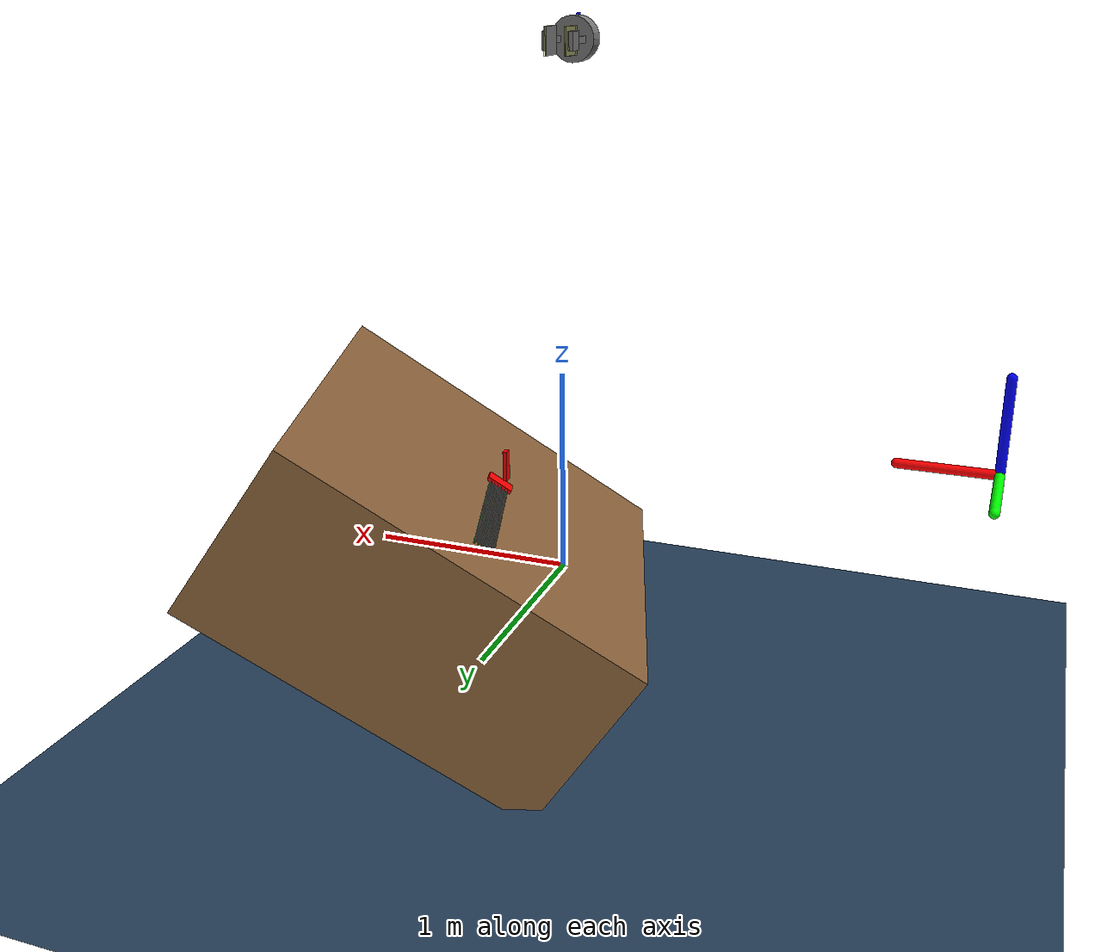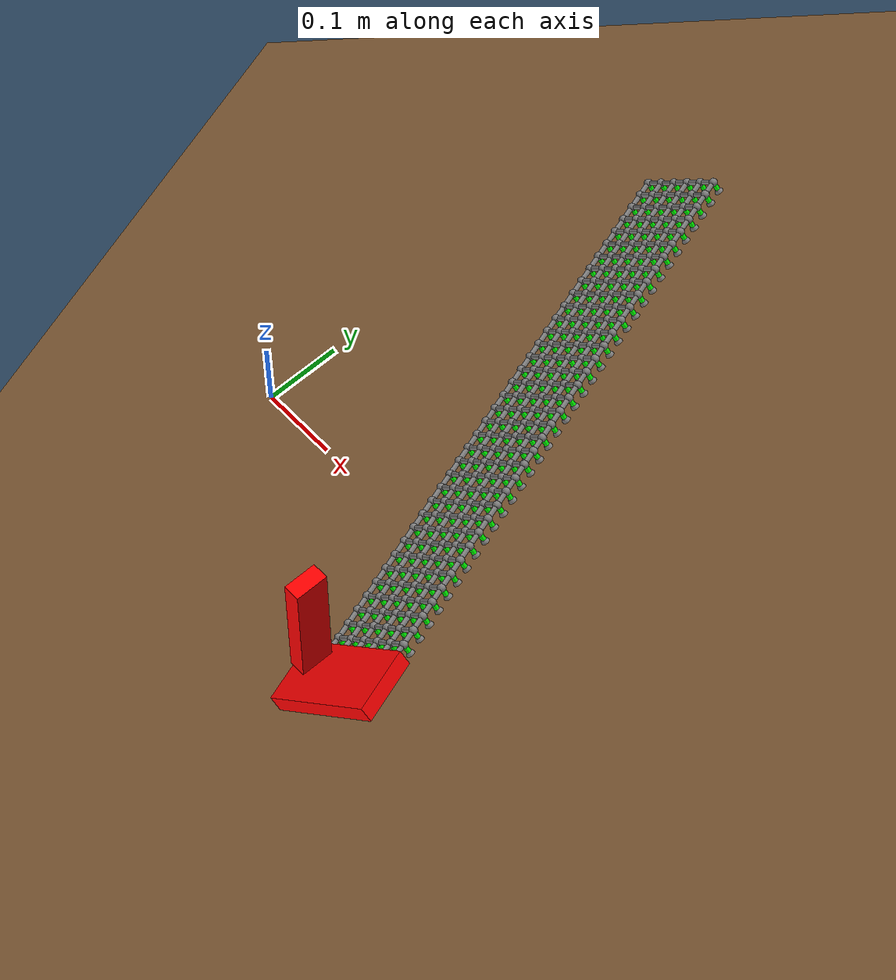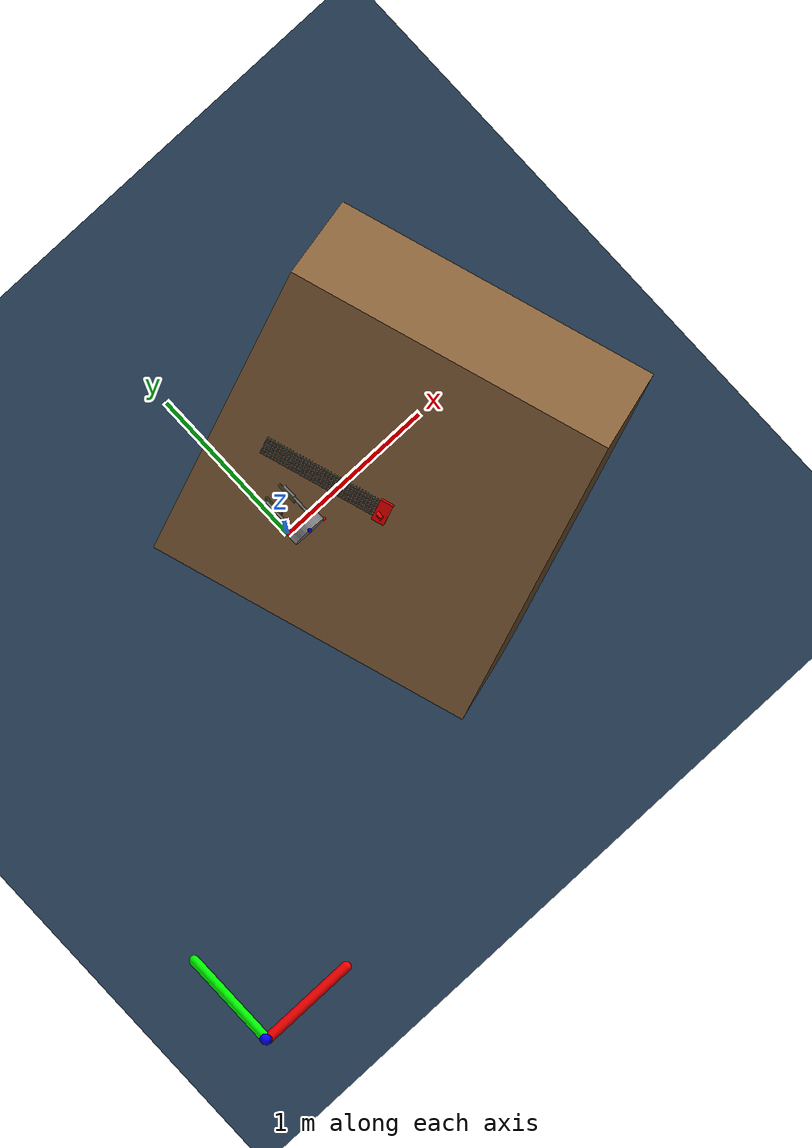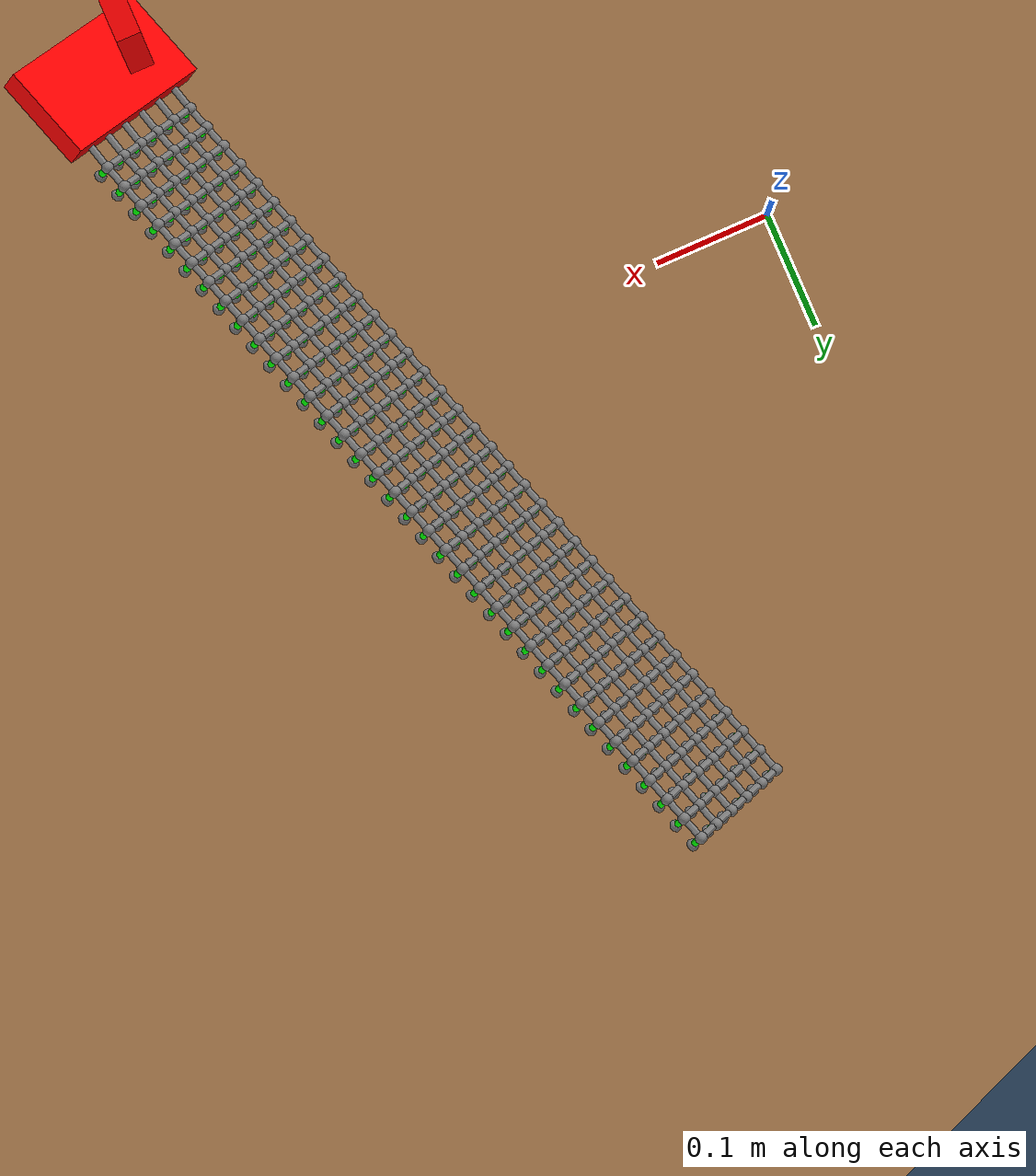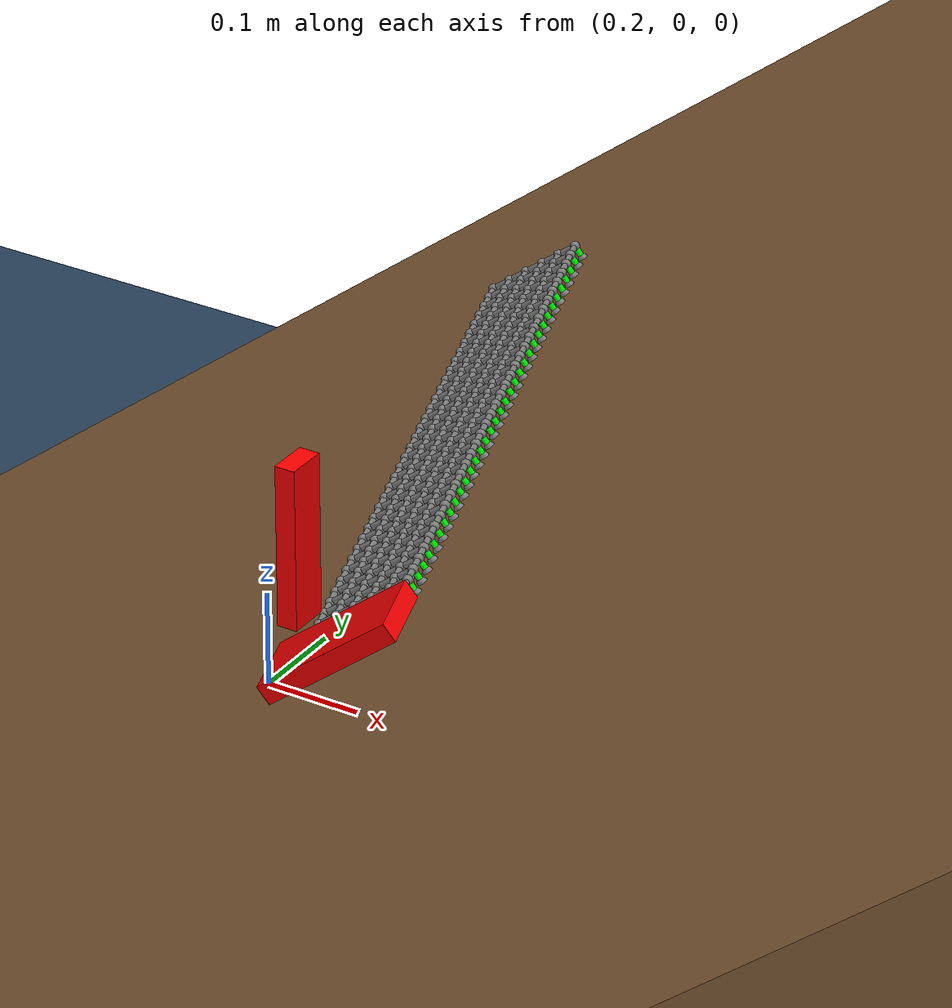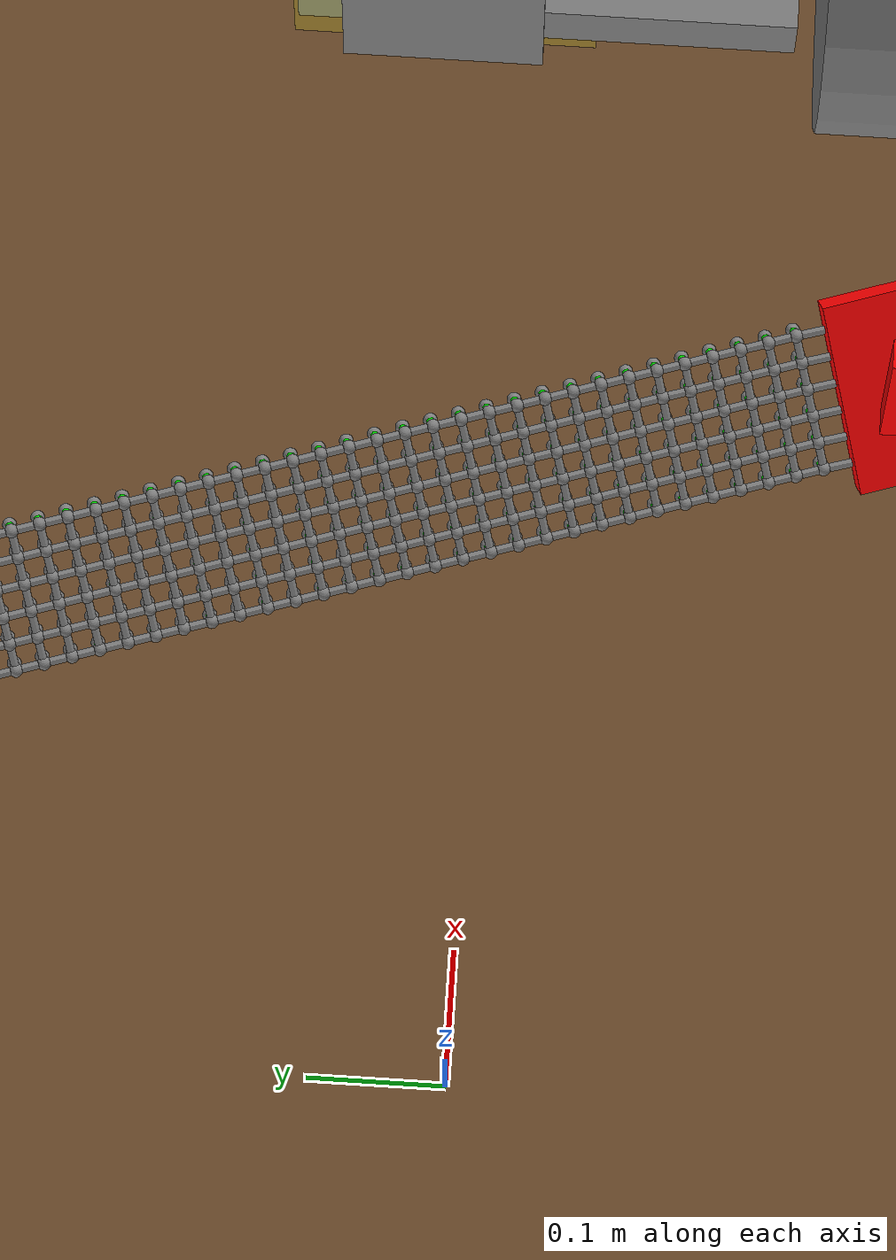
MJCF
<mujoco>
  <compiler angle="radian"
              inertiafromgeom="auto"
              texturedir="textures/"
              meshdir="mesh/visual/"/>
  <option timestep="1e-4"
            iterations="35"
            tolerance="1e-10"
            impratio="20"
            cone="elliptic" />
  <size njmax="10000" nconmax="5000" nstack="15000000"/>

  <default>
      <geom contype='1' conaffinity='1' condim='6' solref="2e-4 1" solimp=".995 .995 .01" friction="1.3 0.01 0.0005" />
      <joint armature="0.01" damping=".1"/>
      <default class="gripperTrans">
         <joint damping='30' />
      </default>
      <default class="gripperRot">
         <joint damping='65'/>
      </default>
      <default class="GRIPPER">
         <joint damping='15'/>
      </default>
  </default>

  <visual>
    <map fogstart="3" fogend="5" znear="0.05"/>
    <quality shadowsize="2048"/>
    <scale  framelength="2.5"
            framewidth="0.06"
            contactwidth="1.1"
            contactheight="0.01"
            forcewidth="0.01"
            />
  </visual>

    <!--Assets-->
  <asset>
    <!--Textures-->
    <texture name="ur5_tex"     type="2d"       builtin="flat" height="32" width="32" rgb1="0.45 0.45 0.45" />
    <texture name="gripper_tex" type="2d"       builtin="flat" height="32" width="32" rgb1="0.45 0.45 0.45" rgb2="0 0 0"/>
    <texture name="bench_tex"   type="2d"       builtin="flat" height="32" width="32" rgb1="0.7 0.7 0.7" />
    <texture name="sky_tex"     type="skybox"   builtin="gradient" width="100" height="100" rgb1="1 1 1" rgb2="0.3 0.3 0.8" />
    <texture name="texgeom"     type="cube"     builtin="flat" mark="cross" width="127" height="1278" rgb1="0.8 0.6 0.4" rgb2="0.8 0.6 0.4" markrgb="1 1 1" random="0.01" />
    <texture name="floor_tex"   type="2d"        builtin="checker" rgb1=".2 .3 .4" rgb2=".1 .2 .3" width="100" height="100" />
    <texture name="wood"        type="cube"     file="wood2.png"/>
    <texture name="metal"        type="cube"     file="metal2.png"/>
    <!--Materials-->
    <material name="ur5_mat"        texture="ur5_tex"   shininess="0.9" specular="0.75" reflectance="0.3"/>
    <material name="gripper_mat"    texture="gripper_tex"   shininess="0.9" specular="0.75" reflectance="0.4"/>
    <material name='floor_mat'      texture="floor_tex"  shininess="0.8" texrepeat="10 10" specular="0.7"  reflectance="0.5" />
    <material name='geom'           texture="texgeom"   texuniform="true" />
    <material name="bench_mat"      texture="metal"   shininess="0.1" specular="0.5" reflectance="0.2"/>
    <material name="tablecube"      texture="wood" rgba=".8 .8 .8 1"/>
  </asset>

  <worldbody>
    <!--Lighting parameters-->
    <light name="light3" mode="targetbody" target="gripperLink_0" directional="true" pos="1 1 5" />

    <geom type='capsule' size='0.03 0.3' pos='-1.7 -2 0' rgba='1 0 0 1' quat='0.7071068  0 0.7071068 0' />
    <geom type='capsule' size='0.03 0.3' pos='-2 -1.7 0' rgba='0 1 0 1' quat='0.7071068  0.7071068 0 0' />
    <geom type='capsule' size='0.03 0.3' pos='-2 -2 0.3' rgba='0 0 1 1' />

     <!--Floor Property-->
    <geom name='floor' material="floor_mat" pos='0 0 -1' size='2.5 2.5 0.1'  type='plane' />

    <!-- Insert table here! -->
    <body name="table" pos="0 0 0" >
        <body name="handle" pos="0.4627357446111554 -0.2827949937356617 0.27263239708122156" euler="0.20696228839328648 -0.5768104767730677 1.9501557636123243" >
            <joint name="handle_x" type="slide" pos="0 0 0" axis="1 0 0" damping="10" />
            <joint name="handle_y" type="slide" pos="0 0 0" axis="0 1 0" damping="10" />
            <joint name="handle_z" type="slide" pos="0 0 0" axis="0 0 1" damping="10" />
            <joint name="handle_rot_x" type="hinge" pos="0 0 0" axis="1 0 0" damping="10" />
            <joint name="handle_rot_y" type="hinge" pos="0 0 0" axis="0 1 0" damping="10" />
            <joint name="handle_rot_z" type="hinge" pos="0 0 0" axis="0 0 1" damping="10" />
            <geom name="handle" material="bench_mat" type="box" size="0.04 0.07 0.01" rgba="1 0 0 1" density="50" />
            <site name='handle_0' type='sphere' size='0.01' pos='0 -0.05 0' rgba='0 1 0 1' />
            <site name='handle_1' type='sphere' size='0.01' pos='0 -0.03 0' rgba='0 1 0 1' />
            <site name='handle_2' type='sphere' size='0.01' pos='0 -0.01 0' rgba='0 1 0 1' />
            <site name='handle_3' type='sphere' size='0.01' pos='0 0.01 0' rgba='0 1 0 1' />
            <site name='handle_4' type='sphere' size='0.01' pos='0 0.03 0' rgba='0 1 0 1' />
            <site name='handle_5' type='sphere' size='0.01' pos='0 0.05 0' rgba='0 1 0 1' />
            <body name="handle2" pos="0 0 0.06" euler="0.6087953899352078 -0.006770222547369424 -1.8864272744805965" >
                <geom name="handle2" material="bench_mat" pos="0 0 0.05" type="box" size="0.01 0.02 0.08" density="50" rgba="1 0 0 1"/>
            </body>
        </body>
        <geom name="tabletop" material="tablecube" pos="0.7611719219467175 -0.1250008577815756 -0.11754302335917508" euler="0.20696228839328648 -0.5768104767730677 1.9501557636123243" size="1 1 0.49" type="box" />
        <site name="table_0_0" type="sphere" size="0.005" pos="0.4939488359501998 -0.20939910160442488 0.28441314185056094"  />
        <site name="table_0_1" type="sphere" size="0.005" pos="0.47837660455126585 -0.21456563372284193 0.2729758102068855"  />
        <site name="table_0_2" type="sphere" size="0.005" pos="0.46280437315233186 -0.219732165841259 0.2615384785632101"  />
        <site name="table_0_3" type="sphere" size="0.005" pos="0.44723214175339787 -0.224898697959676 0.2501011469195346"  />
        <site name="table_0_4" type="sphere" size="0.005" pos="0.43165991035446394 -0.2300652300780931 0.23866381527585917"  />
        <site name="table_0_5" type="sphere" size="0.005" pos="0.4160876789555299 -0.2352317621965101 0.22722648363218373"  />
        <site name="table_1_0" type="sphere" size="0.005" pos="0.4877406519859191 -0.19038752308552132 0.28427773843400905"  />
        <site name="table_1_1" type="sphere" size="0.005" pos="0.4721684205869851 -0.19555405520393837 0.27284040679033356"  />
        <site name="table_1_2" type="sphere" size="0.005" pos="0.4565961891880511 -0.2007205873223554 0.26140307514665806"  />
        <site name="table_1_3" type="sphere" size="0.005" pos="0.4410239577891172 -0.20588711944077248 0.24996574350298267"  />
        <site name="table_1_4" type="sphere" size="0.005" pos="0.42545172639018314 -0.21105365155918954 0.23852841185930718"  />
        <site name="table_1_5" type="sphere" size="0.005" pos="0.4098794949912492 -0.21622018367760656 0.22709108021563174"  />
        <site name="table_2_0" type="sphere" size="0.005" pos="0.48153246802163835 -0.1713759445666178 0.284142335017457"  />
        <site name="table_2_1" type="sphere" size="0.005" pos="0.46596023662270436 -0.17654247668503487 0.2727050033737815"  />
        <site name="table_2_2" type="sphere" size="0.005" pos="0.4503880052237704 -0.18170900880345192 0.2612676717301061"  />
        <site name="table_2_3" type="sphere" size="0.005" pos="0.4348157738248364 -0.18687554092186898 0.2498303400864307"  />
        <site name="table_2_4" type="sphere" size="0.005" pos="0.4192435424259024 -0.19204207304028603 0.2383930084427552"  />
        <site name="table_2_5" type="sphere" size="0.005" pos="0.40367131102696846 -0.19720860515870306 0.22695567679907977"  />
        <site name="table_3_0" type="sphere" size="0.005" pos="0.47532428405735766 -0.15236436604771433 0.28400693160090507"  />
        <site name="table_3_1" type="sphere" size="0.005" pos="0.45975205265842367 -0.1575308981661314 0.2725695999572296"  />
        <site name="table_3_2" type="sphere" size="0.005" pos="0.4441798212594896 -0.16269743028454842 0.26113226831355413"  />
        <site name="table_3_3" type="sphere" size="0.005" pos="0.42860758986055575 -0.16786396240296547 0.24969493666987874"  />
        <site name="table_3_4" type="sphere" size="0.005" pos="0.41303535846162165 -0.17303049452138253 0.23825760502620325"  />
        <site name="table_3_5" type="sphere" size="0.005" pos="0.3974631270626877 -0.17819702663979956 0.22682027338252775"  />
        <site name="table_4_0" type="sphere" size="0.005" pos="0.4691161000930769 -0.13335278752881077 0.2838715281843531"  />
        <site name="table_4_1" type="sphere" size="0.005" pos="0.45354386869414287 -0.13851931964722783 0.27243419654067763"  />
        <site name="table_4_2" type="sphere" size="0.005" pos="0.4379716372952089 -0.14368585176564486 0.26099686489700213"  />
        <site name="table_4_3" type="sphere" size="0.005" pos="0.42239940589627495 -0.1488523838840619 0.24955953325332675"  />
        <site name="table_4_4" type="sphere" size="0.005" pos="0.40682717449734096 -0.15401891600247897 0.23812220160965128"  />
        <site name="table_4_5" type="sphere" size="0.005" pos="0.39125494309840697 -0.159185448120896 0.2266848699659758"  />
        <site name="table_5_0" type="sphere" size="0.005" pos="0.4629079161287961 -0.1143412090099073 0.283736124767801"  />
        <site name="table_5_1" type="sphere" size="0.005" pos="0.4473356847298621 -0.11950774112832435 0.27229879312412564"  />
        <site name="table_5_2" type="sphere" size="0.005" pos="0.4317634533309282 -0.12467427324674138 0.2608614614804502"  />
        <site name="table_5_3" type="sphere" size="0.005" pos="0.41619122193199426 -0.12984080536515843 0.2494241298367747"  />
        <site name="table_5_4" type="sphere" size="0.005" pos="0.4006189905330602 -0.13500733748357552 0.2379867981930993"  />
        <site name="table_5_5" type="sphere" size="0.005" pos="0.3850467591341263 -0.14017386960199252 0.22654946654942382"  />
        <site name="table_6_0" type="sphere" size="0.005" pos="0.4566997321645155 -0.09532963049100379 0.28360072135124914"  />
        <site name="table_6_1" type="sphere" size="0.005" pos="0.44112750076558144 -0.10049616260942083 0.27216338970757364"  />
        <site name="table_6_2" type="sphere" size="0.005" pos="0.42555526936664745 -0.10566269472783785 0.2607260580638982"  />
        <site name="table_6_3" type="sphere" size="0.005" pos="0.40998303796771346 -0.11082922684625493 0.24928872642022276"  />
        <site name="table_6_4" type="sphere" size="0.005" pos="0.39441080656877947 -0.11599575896467196 0.23785139477654726"  />
        <site name="table_6_5" type="sphere" size="0.005" pos="0.3788385751698455 -0.121162291083089 0.22641406313287185"  />
        <site name="table_7_0" type="sphere" size="0.005" pos="0.4504915482002347 -0.07631805197210022 0.28346531793469715"  />
        <site name="table_7_1" type="sphere" size="0.005" pos="0.4349193168013007 -0.08148458409051726 0.27202798629102165"  />
        <site name="table_7_2" type="sphere" size="0.005" pos="0.4193470854023667 -0.08665111620893431 0.26059065464734626"  />
        <site name="table_7_3" type="sphere" size="0.005" pos="0.40377485400343277 -0.09181764832735137 0.2491533230036708"  />
        <site name="table_7_4" type="sphere" size="0.005" pos="0.3882026226044987 -0.09698418044576843 0.23771599135999533"  />
        <site name="table_7_5" type="sphere" size="0.005" pos="0.3726303912055648 -0.10215071256418545 0.22627865971631986"  />
        <site name="table_8_0" type="sphere" size="0.005" pos="0.44428336423595394 -0.05730647345319672 0.28332991451814515"  />
        <site name="table_8_1" type="sphere" size="0.005" pos="0.42871113283701995 -0.062473005571613775 0.27189258287446966"  />
        <site name="table_8_2" type="sphere" size="0.005" pos="0.413138901438086 -0.06763953769003081 0.26045525123079427"  />
        <site name="table_8_3" type="sphere" size="0.005" pos="0.39756667003915197 -0.07280606980844787 0.24901791958711877"  />
        <site name="table_8_4" type="sphere" size="0.005" pos="0.381994438640218 -0.07797260192686492 0.2375805879434433"  />
        <site name="table_8_5" type="sphere" size="0.005" pos="0.36642220724128405 -0.08313913404528195 0.2261432562997679"  />
        <site name="table_9_0" type="sphere" size="0.005" pos="0.43807518027167325 -0.03829489493429323 0.2831945111015932"  />
        <site name="table_9_1" type="sphere" size="0.005" pos="0.42250294887273926 -0.04346142705271028 0.2717571794579177"  />
        <site name="table_9_2" type="sphere" size="0.005" pos="0.4069307174738052 -0.0486279591711273 0.2603198478142422"  />
        <site name="table_9_3" type="sphere" size="0.005" pos="0.3913584860748713 -0.05379449128954437 0.24888251617056678"  />
        <site name="table_9_4" type="sphere" size="0.005" pos="0.37578625467593724 -0.05896102340796142 0.23744518452689134"  />
        <site name="table_9_5" type="sphere" size="0.005" pos="0.3602140232770033 -0.06412755552637846 0.22600785288321593"  />
        <site name="table_10_0" type="sphere" size="0.005" pos="0.4318669963073925 -0.01928331641538967 0.28305910768504117"  />
        <site name="table_10_1" type="sphere" size="0.005" pos="0.41629476490845846 -0.024449848533806728 0.2716217760413657"  />
        <site name="table_10_2" type="sphere" size="0.005" pos="0.4007225335095245 -0.029616380652223755 0.2601844443976903"  />
        <site name="table_10_3" type="sphere" size="0.005" pos="0.38515030211059054 -0.034782912770640814 0.24874711275401484"  />
        <site name="table_10_4" type="sphere" size="0.005" pos="0.36957807071165655 -0.03994944488905787 0.23730978111033937"  />
        <site name="table_10_5" type="sphere" size="0.005" pos="0.35400583931272256 -0.045115977007474904 0.22587244946666396"  />
        <site name="table_11_0" type="sphere" size="0.005" pos="0.4256588123431117 -0.0002717378964861711 0.2829237042684892"  />
        <site name="table_11_1" type="sphere" size="0.005" pos="0.41008658094417777 -0.005438270014903233 0.2714863726248138"  />
        <site name="table_11_2" type="sphere" size="0.005" pos="0.3945143495452438 -0.010604802133320261 0.2600490409811383"  />
        <site name="table_11_3" type="sphere" size="0.005" pos="0.37894211814630985 -0.015771334251737323 0.24861170933746288"  />
        <site name="table_11_4" type="sphere" size="0.005" pos="0.3633698867473758 -0.020937866370154375 0.2371743776937874"  />
        <site name="table_11_5" type="sphere" size="0.005" pos="0.34779765534844187 -0.026104398488571406 0.22573704605011197"  />
        <site name="table_12_0" type="sphere" size="0.005" pos="0.41945062837883107 0.018739840622417327 0.28278830085193724"  />
        <site name="table_12_1" type="sphere" size="0.005" pos="0.40387839697989697 0.013573308504000271 0.2713509692082618"  />
        <site name="table_12_2" type="sphere" size="0.005" pos="0.38830616558096304 0.008406776385583237 0.25991363756458635"  />
        <site name="table_12_3" type="sphere" size="0.005" pos="0.37273393418202905 0.0032402442671661813 0.24847630592091088"  />
        <site name="table_12_4" type="sphere" size="0.005" pos="0.35716170278309506 -0.001926287851250874 0.2370389742772354"  />
        <site name="table_12_5" type="sphere" size="0.005" pos="0.34158947138416107 -0.007092819969667909 0.22560164263355997"  />
        <site name="table_13_0" type="sphere" size="0.005" pos="0.41324244441455027 0.037751419141320866 0.28265289743538524"  />
        <site name="table_13_1" type="sphere" size="0.005" pos="0.3976702130156163 0.03258488702290381 0.2712155657917098"  />
        <site name="table_13_2" type="sphere" size="0.005" pos="0.3820979816166823 0.027418354904486783 0.25977823414803436"  />
        <site name="table_13_3" type="sphere" size="0.005" pos="0.36652575021774836 0.02225182278606972 0.24834090250435892"  />
        <site name="table_13_4" type="sphere" size="0.005" pos="0.3509535188188143 0.017085290667652665 0.23690357086068345"  />
        <site name="table_13_5" type="sphere" size="0.005" pos="0.3353812874198804 0.01191875854923563 0.225466239217008"  />
        <site name="table_14_0" type="sphere" size="0.005" pos="0.4070342604502695 0.05676299766022439 0.28251749401883325"  />
        <site name="table_14_1" type="sphere" size="0.005" pos="0.3914620290513355 0.051596465541807336 0.27108016237515775"  />
        <site name="table_14_2" type="sphere" size="0.005" pos="0.3758897976524016 0.046429933423390295 0.25964283073148237"  />
        <site name="table_14_3" type="sphere" size="0.005" pos="0.36031756625346756 0.04126340130497326 0.2482054990878069"  />
        <site name="table_14_4" type="sphere" size="0.005" pos="0.34474533485453357 0.0360968691865562 0.23676816744413146"  />
        <site name="table_14_5" type="sphere" size="0.005" pos="0.32917310345559964 0.030930337068139163 0.22533083580045601"  />
        <site name="table_15_0" type="sphere" size="0.005" pos="0.4008260764859888 0.07577457617912786 0.28238209060228125"  />
        <site name="table_15_1" type="sphere" size="0.005" pos="0.3852538450870548 0.07060804406071083 0.2709447589586058"  />
        <site name="table_15_2" type="sphere" size="0.005" pos="0.3696816136881208 0.06544151194229378 0.2595074273149304"  />
        <site name="table_15_3" type="sphere" size="0.005" pos="0.35410938228918687 0.06027497982387673 0.24807009567125493"  />
        <site name="table_15_4" type="sphere" size="0.005" pos="0.3385371508902528 0.05510844770545967 0.2366327640275795"  />
        <site name="table_15_5" type="sphere" size="0.005" pos="0.3229649194913189 0.04994191558704264 0.22519543238390402"  />
        <site name="table_16_0" type="sphere" size="0.005" pos="0.3946178925217081 0.0947861546980314 0.2822466871857293"  />
        <site name="table_16_1" type="sphere" size="0.005" pos="0.37904566112277405 0.08961962257961434 0.2708093555420538"  />
        <site name="table_16_2" type="sphere" size="0.005" pos="0.3634734297238401 0.08445309046119731 0.25937202389837843"  />
        <site name="table_16_3" type="sphere" size="0.005" pos="0.3479011983249061 0.07928655834278024 0.24793469225470297"  />
        <site name="table_16_4" type="sphere" size="0.005" pos="0.33232896692597214 0.0741200262243632 0.2364973606110275"  />
        <site name="table_16_5" type="sphere" size="0.005" pos="0.31675673552703815 0.06895349410594617 0.22506002896735205"  />
        <site name="table_17_0" type="sphere" size="0.005" pos="0.38840970855742735 0.11379773321693493 0.2821112837691773"  />
        <site name="table_17_1" type="sphere" size="0.005" pos="0.37283747715849336 0.1086312010985179 0.2706739521255019"  />
        <site name="table_17_2" type="sphere" size="0.005" pos="0.35726524575955937 0.10346466898010086 0.2592366204818265"  />
        <site name="table_17_3" type="sphere" size="0.005" pos="0.34169301436062544 0.09829813686168377 0.247799288838151"  />
        <site name="table_17_4" type="sphere" size="0.005" pos="0.3261207829616914 0.09313160474326675 0.23636195719447553"  />
        <site name="table_17_5" type="sphere" size="0.005" pos="0.31054855156275746 0.0879650726248497 0.22492462555080012"  />
        <site name="table_18_0" type="sphere" size="0.005" pos="0.3822015245931466 0.13280931173583843 0.28197588035262533"  />
        <site name="table_18_1" type="sphere" size="0.005" pos="0.36662929319421256 0.12764277961742138 0.2705385487089499"  />
        <site name="table_18_2" type="sphere" size="0.005" pos="0.3510570617952786 0.12247624749900435 0.2591012170652744"  />
        <site name="table_18_3" type="sphere" size="0.005" pos="0.33548483039634464 0.11730971538058728 0.247663885421599"  />
        <site name="table_18_4" type="sphere" size="0.005" pos="0.31991259899741065 0.11214318326217022 0.23622655377792354"  />
        <site name="table_18_5" type="sphere" size="0.005" pos="0.30434036759847666 0.10697665114375318 0.2247892221342481"  />
        <site name="table_19_0" type="sphere" size="0.005" pos="0.37599334062886586 0.15182089025474196 0.2818404769360734"  />
        <site name="table_19_1" type="sphere" size="0.005" pos="0.36042110922993187 0.1466543581363249 0.2704031452923979"  />
        <site name="table_19_2" type="sphere" size="0.005" pos="0.3448488778309979 0.14148782601790788 0.25896581364872245"  />
        <site name="table_19_3" type="sphere" size="0.005" pos="0.32927664643206395 0.1363212938994908 0.24752848200504704"  />
        <site name="table_19_4" type="sphere" size="0.005" pos="0.3137044150331299 0.13115476178107377 0.23609115036137154"  />
        <site name="table_19_5" type="sphere" size="0.005" pos="0.29813218363419597 0.12598822966265671 0.2246538187176961"  />
        <site name="table_20_0" type="sphere" size="0.005" pos="0.36978515666458517 0.17083246877364547 0.2817050735195214"  />
        <site name="table_20_1" type="sphere" size="0.005" pos="0.3542129252656511 0.16566593665522844 0.27026774187584596"  />
        <site name="table_20_2" type="sphere" size="0.005" pos="0.3386406938667172 0.16049940453681139 0.2588304102321705"  />
        <site name="table_20_3" type="sphere" size="0.005" pos="0.3230684624677832 0.15533287241839433 0.24739307858849507"  />
        <site name="table_20_4" type="sphere" size="0.005" pos="0.3074962310688492 0.15016634029997727 0.23595574694481958"  />
        <site name="table_20_5" type="sphere" size="0.005" pos="0.2919239996699152 0.14499980818156025 0.22451841530114414"  />
        <site name="table_21_0" type="sphere" size="0.005" pos="0.3635769727003044 0.18984404729254895 0.2815696701029694"  />
        <site name="table_21_1" type="sphere" size="0.005" pos="0.34800474130137043 0.1846775151741319 0.27013233845929396"  />
        <site name="table_21_2" type="sphere" size="0.005" pos="0.33243250990243645 0.17951098305571486 0.2586950068156185"  />
        <site name="table_21_3" type="sphere" size="0.005" pos="0.3168602785035025 0.1743444509372978 0.24725767517194308"  />
        <site name="table_21_4" type="sphere" size="0.005" pos="0.30128804710456847 0.16917791881888078 0.23582034352826764"  />
        <site name="table_21_5" type="sphere" size="0.005" pos="0.28571581570563453 0.16401138670046375 0.2243830118845922"  />
        <site name="table_22_0" type="sphere" size="0.005" pos="0.3573687887360237 0.2088556258114525 0.2814342666864174"  />
        <site name="table_22_1" type="sphere" size="0.005" pos="0.34179655733708963 0.20368909369303545 0.26999693504274197"  />
        <site name="table_22_2" type="sphere" size="0.005" pos="0.3262243259381557 0.1985225615746184 0.25855960339906653"  />
        <site name="table_22_3" type="sphere" size="0.005" pos="0.3106520945392217 0.19335602945620134 0.2471222717553911"  />
        <site name="table_22_4" type="sphere" size="0.005" pos="0.2950798631402877 0.18818949733778428 0.23568494011171565"  />
        <site name="table_22_5" type="sphere" size="0.005" pos="0.27950763174135373 0.18302296521936726 0.22424760846804018"  />
        <site name="table_23_0" type="sphere" size="0.005" pos="0.35116060477174293 0.227867204330356 0.2812988632698655"  />
        <site name="table_23_1" type="sphere" size="0.005" pos="0.33558837337280895 0.22270067221193895 0.26986153162619"  />
        <site name="table_23_2" type="sphere" size="0.005" pos="0.32001614197387496 0.21753414009352193 0.2584241999825146"  />
        <site name="table_23_3" type="sphere" size="0.005" pos="0.304443910574941 0.21236760797510487 0.24698686833883912"  />
        <site name="table_23_4" type="sphere" size="0.005" pos="0.288871679176007 0.2072010758566878 0.23554953669516362"  />
        <site name="table_23_5" type="sphere" size="0.005" pos="0.27329944777707305 0.2020345437382708 0.2241122050514882"  />
        <site name="table_24_0" type="sphere" size="0.005" pos="0.34495242080746225 0.2468787828492595 0.2811634598533135"  />
        <site name="table_24_1" type="sphere" size="0.005" pos="0.3293801894085282 0.24171225073084246 0.26972612820963804"  />
        <site name="table_24_2" type="sphere" size="0.005" pos="0.31380795800959427 0.23654571861242538 0.2582887965659626"  />
        <site name="table_24_3" type="sphere" size="0.005" pos="0.2982357266106603 0.23137918649400838 0.24685146492228713"  />
        <site name="table_24_4" type="sphere" size="0.005" pos="0.2826634952117263 0.22621265437559127 0.23541413327861166"  />
        <site name="table_24_5" type="sphere" size="0.005" pos="0.2670912638127923 0.22104612225717427 0.22397680163493625"  />
        <site name="table_25_0" type="sphere" size="0.005" pos="0.33874423684318145 0.265890361368163 0.2810280564367615"  />
        <site name="table_25_1" type="sphere" size="0.005" pos="0.32317200544424746 0.260723829249746 0.26959072479308605"  />
        <site name="table_25_2" type="sphere" size="0.005" pos="0.30759977404531347 0.25555729713132896 0.2581533931494106"  />
        <site name="table_25_3" type="sphere" size="0.005" pos="0.29202754264637953 0.2503907650129119 0.24671606150573516"  />
        <site name="table_25_4" type="sphere" size="0.005" pos="0.2764553112474455 0.24522423289449483 0.2352787298620597"  />
        <site name="table_25_5" type="sphere" size="0.005" pos="0.26088307984851156 0.24005770077607783 0.22384139821838425"  />
        <site name="table_26_0" type="sphere" size="0.005" pos="0.33253605287890076 0.2849019398870666 0.2808926530202095"  />
        <site name="table_26_1" type="sphere" size="0.005" pos="0.3169638214799667 0.2797354077686495 0.26945532137653405"  />
        <site name="table_26_2" type="sphere" size="0.005" pos="0.3013915900810328 0.2745688756502325 0.2580179897328586"  />
        <site name="table_26_3" type="sphere" size="0.005" pos="0.2858193586820988 0.2694023435318154 0.2465806580891832"  />
        <site name="table_26_4" type="sphere" size="0.005" pos="0.2702471272831648 0.26423581141339836 0.23514332644550773"  />
        <site name="table_26_5" type="sphere" size="0.005" pos="0.2546748958842308 0.25906927929498136 0.22370599480183226"  />
        <site name="table_27_0" type="sphere" size="0.005" pos="0.32632786891461996 0.30391351840597014 0.28075724960365755"  />
        <site name="table_27_1" type="sphere" size="0.005" pos="0.31075563751568597 0.2987469862875531 0.26931991795998206"  />
        <site name="table_27_2" type="sphere" size="0.005" pos="0.295183406116752 0.29358045416913603 0.2578825863163066"  />
        <site name="table_27_3" type="sphere" size="0.005" pos="0.27961117471781805 0.28841392205071903 0.24644525467263118"  />
        <site name="table_27_4" type="sphere" size="0.005" pos="0.264038943318884 0.2832473899323019 0.23500792302895573"  />
        <site name="table_27_5" type="sphere" size="0.005" pos="0.24846671191995007 0.27808085781388486 0.2235705913852803"  />
        <site name="table_28_0" type="sphere" size="0.005" pos="0.32011968495033927 0.3229250969248737 0.28062184618710556"  />
        <site name="table_28_1" type="sphere" size="0.005" pos="0.3045474535514052 0.3177585648064566 0.26918451454343006"  />
        <site name="table_28_2" type="sphere" size="0.005" pos="0.2889752221524713 0.3125920326880396 0.2577471828997547"  />
        <site name="table_28_3" type="sphere" size="0.005" pos="0.2734029907535373 0.3074255005696226 0.2463098512560792"  />
        <site name="table_28_4" type="sphere" size="0.005" pos="0.2578307593546033 0.3022589684512054 0.23487251961240377"  />
        <site name="table_28_5" type="sphere" size="0.005" pos="0.24225852795566935 0.2970924363327884 0.22343518796872833"  />
        <site name="table_29_0" type="sphere" size="0.005" pos="0.3139115009860585 0.3419366754437771 0.28048644277055357"  />
        <site name="table_29_1" type="sphere" size="0.005" pos="0.29833926958712453 0.33677014332536004 0.2690491111268781"  />
        <site name="table_29_2" type="sphere" size="0.005" pos="0.28276703818819054 0.3316036112069429 0.2576117794832027"  />
        <site name="table_29_3" type="sphere" size="0.005" pos="0.2671948067892566 0.32643707908852587 0.24617444783952724"  />
        <site name="table_29_4" type="sphere" size="0.005" pos="0.25162257539032257 0.3212705469701089 0.23473711619585175"  />
        <site name="table_29_5" type="sphere" size="0.005" pos="0.2360503439913886 0.3161040148516918 0.22329978455217636"  />
        <site name="table_30_0" type="sphere" size="0.005" pos="0.30770331702177783 0.3609482539626806 0.28035103935400163"  />
        <site name="table_30_1" type="sphere" size="0.005" pos="0.2921310856228438 0.3557817218442635 0.26891370771032613"  />
        <site name="table_30_2" type="sphere" size="0.005" pos="0.27655885422390986 0.3506151897258465 0.25747637606665075"  />
        <site name="table_30_3" type="sphere" size="0.005" pos="0.26098662282497587 0.3454486576074294 0.24603904442297525"  />
        <site name="table_30_4" type="sphere" size="0.005" pos="0.24541439142604185 0.3402821254890124 0.2346017127792998"  />
        <site name="table_30_5" type="sphere" size="0.005" pos="0.2298421600271079 0.3351155933705953 0.22316438113562437"  />
        <site name="table_31_0" type="sphere" size="0.005" pos="0.30149513305749703 0.37995983248158416 0.28021563593744964"  />
        <site name="table_31_1" type="sphere" size="0.005" pos="0.28592290165856304 0.37479330036316705 0.26877830429377414"  />
        <site name="table_31_2" type="sphere" size="0.005" pos="0.27035067025962906 0.36962676824475005 0.2573409726500987"  />
        <site name="table_31_3" type="sphere" size="0.005" pos="0.2547784388606951 0.36446023612633294 0.24590364100642328"  />
        <site name="table_31_4" type="sphere" size="0.005" pos="0.2392062074617611 0.3592937040079159 0.2344663093627478"  />
        <site name="table_31_5" type="sphere" size="0.005" pos="0.22363397606282714 0.3541271718894989 0.22302897771907237"  />
        <site name="table_32_0" type="sphere" size="0.005" pos="0.29528694909321634 0.3989714110004877 0.28008023252089764"  />
        <site name="table_32_1" type="sphere" size="0.005" pos="0.2797147176942823 0.3938048788820706 0.2686429008772222"  />
        <site name="table_32_2" type="sphere" size="0.005" pos="0.26414248629534837 0.3886383467636536 0.25720556923354676"  />
        <site name="table_32_3" type="sphere" size="0.005" pos="0.24857025489641438 0.3834718146452365 0.24576823758987132"  />
        <site name="table_32_4" type="sphere" size="0.005" pos="0.23299802349748036 0.37830528252681944 0.23433090594619582"  />
        <site name="table_32_5" type="sphere" size="0.005" pos="0.2174257920985464 0.37313875040840244 0.2228935743025204"  />
        <site name="table_33_0" type="sphere" size="0.005" pos="0.2890787651289356 0.41798298951939117 0.27994482910434565"  />
        <site name="table_33_1" type="sphere" size="0.005" pos="0.2735065337300016 0.4128164574009741 0.26850749746067026"  />
        <site name="table_33_2" type="sphere" size="0.005" pos="0.25793430233106757 0.40764992528255706 0.2570701658169947"  />
        <site name="table_33_3" type="sphere" size="0.005" pos="0.24236207093213366 0.40248339316414 0.24563283417331933"  />
        <site name="table_33_4" type="sphere" size="0.005" pos="0.22678983953319964 0.397316861045723 0.23419550252964388"  />
        <site name="table_33_5" type="sphere" size="0.005" pos="0.21121760813426566 0.3921503289273059 0.2227581708859684"  />
        <site name="table_34_0" type="sphere" size="0.005" pos="0.28287058116465486 0.43699456803829473 0.27980942568779366"  />
        <site name="table_34_1" type="sphere" size="0.005" pos="0.2672983497657208 0.4318280359198777 0.2683720940441182"  />
        <site name="table_34_2" type="sphere" size="0.005" pos="0.2517261183667869 0.42666150380146056 0.2569347624004428"  />
        <site name="table_34_3" type="sphere" size="0.005" pos="0.2361538869678529 0.42149497168304356 0.24549743075676733"  />
        <site name="table_34_4" type="sphere" size="0.005" pos="0.2205816555689189 0.41632843956462656 0.2340600991130919"  />
        <site name="table_34_5" type="sphere" size="0.005" pos="0.2050094241699849 0.41116190744620945 0.22262276746941642"  />
        <site name="table_35_0" type="sphere" size="0.005" pos="0.27666239720037406 0.4560061465571982 0.2796740222712417"  />
        <site name="table_35_1" type="sphere" size="0.005" pos="0.26109016580144007 0.4508396144387813 0.2682366906275662"  />
        <site name="table_35_2" type="sphere" size="0.005" pos="0.24551793440250613 0.4456730823203641 0.25679935898389084"  />
        <site name="table_35_3" type="sphere" size="0.005" pos="0.22994570300357214 0.4405065502019471 0.24536202734021537"  />
        <site name="table_35_4" type="sphere" size="0.005" pos="0.21437347160463813 0.43534001808353007 0.23392469569653987"  />
        <site name="table_35_5" type="sphere" size="0.005" pos="0.1988012402057042 0.430173485965113 0.22248736405286446"  />
    </body>

    <!-- GRIPPER -->
    <body name="gripperLink_0" pos="0 0 2.5" >
      <joint name="trans_x" type="slide" class="gripperTrans" pos="0 0 0" axis="1 0 0" />
      <joint name="trans_y" type="slide" class="gripperTrans" pos="0 0 0" axis="0 1 0" />
      <joint name="trans_z" type="slide" class="gripperTrans" pos="0 0 0" axis="0 0 1" />
      <joint name="rot_x" class="gripperRot" pos="0 0 0" axis="1 0 0" />
      <joint name="rot_y" class="gripperRot" pos="0 0 0" axis="0 1 0" />
      <joint name="rot_z" class="gripperRot" pos="0 0 0" axis="0 0 1" />

      <geom pos='0 -0.19 0' type='cylinder' size='0.1 0.04' quat='0.7071068 0.7071068 0 0' condim='3' density='10' />
      <geom pos='0.1 -0.23 0' type='sphere' size='0.01' rgba='1 0 0 1' density='1' />
      <geom pos='0 -0.23 0.1' type='sphere' size='0.01' rgba='0 0 1 1' density='1' />

      <body name='left_finger' pos='-0.06 -0.14 0' quat='1 0 0 0'>
        <joint name='l_f' type='slide' pos='0 0 0' axis='1 0 0' range='0 0.05' damping='10' limited='true' solreflimit='1e-3 1' solimplimit=".99 .99 .01" />
        <geom pos='0 0.05 0' type='box' size='0.007 0.05 0.015' condim='6' friction='1 0.02 0.0005' density='10'  />
        <!-- Fingertip -->
        <body name='left_fingertip' pos='0 0.14 0' quat='0.7071068 0 0.7071068 0'>
          <geom pos='0 0 0' type='box' size='0.04 0.04 0.01' condim='6'  friction='1 0.04 0.001' solref='1e-4 1' density='2000'  />
          <!-- Four anchor points for cross tendons, in order to implement shear force sensor -->
          <site name="left_cross_bottom_1" pos="0.04  0 0.01" type='sphere' size='0.003' />
          <site name="left_cross_bottom_2" pos="-0.04 0 0.01" type='sphere' size='0.003' />
          <site name="left_cross_bottom_3" pos="0  0.04 0.01" type='sphere' size='0.003' />
          <site name="left_cross_bottom_4" pos="0 -0.04 0.01" type='sphere' size='0.003' />
          <body name='left_finger_skin' pos='0 0 0.015' >
            <geom pos='0 0 0' type='box' size='0.06 0.06 0.003'  solref='1e-4 1'  />
            <site pos='0 0 -0.003' type='box' size='0.061 0.061 0.006' name='leftFingerMainTouch' rgba='1 1 0 0.2' />
          </body>
        </body>
      </body>

      <body name='right_finger' pos='0.06 -0.14 0' quat='1 0 0 0'>
        <joint name='r_f' type='slide' pos='0 0 0' axis='-1 0 0' range='0 0.05' damping='10' limited='true'  solreflimit='1e-3 1' solimplimit=".99 .99 .01" />
        <geom pos='0 0.05 0' type='box' size='0.007 0.05 0.015' condim='6' friction='1 0.02 0.0005' density='10'  />
        <!-- Fingertip -->
        <body name='right_fingertip' pos='0 0.14 0' quat='-0.7071068 0 0.7071068 0'>
          <geom pos='0 0 0' type='box' size='0.04 0.04 0.01' condim='6'  friction='1 0.04 0.001' solref='1e-4 1' density='2000'  />
          <!-- Four anchor points for cross tendons, in order to implement shear force sensor -->
          <site name="right_cross_bottom_1" pos="0.04  0 0.01" type='sphere' size='0.003' />
          <site name="right_cross_bottom_2" pos="-0.04 0 0.01" type='sphere' size='0.003' />
          <site name="right_cross_bottom_3" pos="0  0.04 0.01" type='sphere' size='0.003' />
          <site name="right_cross_bottom_4" pos="0 -0.04 0.01" type='sphere' size='0.003' />
          <body name='right_finger_skin' pos='0 0 0.015' >
            <geom pos='0 0 0' type='box' size='0.06 0.06 0.003'  solref='1e-4 1' />
            <site pos='0 0 -0.003' type='box' size='0.061 0.061 0.006' name='rightFingerMainTouch' rgba='1 1 0 0.2' />
          </body>
        </body>
      </body>
    </body>

      <!-- Insert velcro here! -->
        <body name="comp_0_0" pos="0.485768537399286 -0.2119827213132876 0.29671792241820594" >
            <joint type="free" name="comp_0_0" />
            <geom type="sphere" size="0.005" density="50" />
            <site name="comp_0_0_0" type="sphere" size="0.005" />
        </body>
        <body name="comp_0_1" pos="0.47019630600035206 -0.21714925343170466 0.2852805907745305" >
            <joint type="free" name="comp_0_1" />
            <geom type="sphere" size="0.005" density="50" />
            <site name="comp_0_1_0" type="sphere" size="0.005" />
        </body>
        <body name="comp_0_2" pos="0.45462407460141807 -0.22231578555012171 0.27384325913085505" >
            <joint type="free" name="comp_0_2" />
            <geom type="sphere" size="0.005" density="50" />
            <site name="comp_0_2_0" type="sphere" size="0.005" />
        </body>
        <body name="comp_0_3" pos="0.4390518432024841 -0.22748231766853877 0.2624059274871796" >
            <joint type="free" name="comp_0_3" />
            <geom type="sphere" size="0.005" density="50" />
            <site name="comp_0_3_0" type="sphere" size="0.005" />
        </body>
        <body name="comp_0_4" pos="0.42347961180355015 -0.23264884978695582 0.25096859584350417" >
            <joint type="free" name="comp_0_4" />
            <geom type="sphere" size="0.005" density="50" />
            <site name="comp_0_4_0" type="sphere" size="0.005" />
        </body>
        <body name="comp_0_5" pos="0.4079073804046161 -0.23781538190537282 0.23953126419982868" >
            <joint type="free" name="comp_0_5" />
            <geom type="sphere" size="0.005" density="50" />
            <site name="comp_0_5_0" type="sphere" size="0.005" />
        </body>
        <body name="comp_1_0" pos="0.4795603534350053 -0.19297114279438404 0.29658251900165405" >
            <joint type="free" name="comp_1_0" />
            <geom type="sphere" size="0.005" density="50" />
            <site name="comp_1_0_0" type="sphere" size="0.005" />
        </body>
        <body name="comp_1_1" pos="0.4639881220360713 -0.1981376749128011 0.28514518735797856" >
            <joint type="free" name="comp_1_1" />
            <geom type="sphere" size="0.005" density="50" />
            <site name="comp_1_1_0" type="sphere" size="0.005" />
        </body>
        <body name="comp_1_2" pos="0.4484158906371373 -0.20330420703121815 0.27370785571430306" >
            <joint type="free" name="comp_1_2" />
            <geom type="sphere" size="0.005" density="50" />
            <site name="comp_1_2_0" type="sphere" size="0.005" />
        </body>
        <body name="comp_1_3" pos="0.4328436592382034 -0.2084707391496352 0.2622705240706277" >
            <joint type="free" name="comp_1_3" />
            <geom type="sphere" size="0.005" density="50" />
            <site name="comp_1_3_0" type="sphere" size="0.005" />
        </body>
        <body name="comp_1_4" pos="0.41727142783926935 -0.21363727126805226 0.2508331924269522" >
            <joint type="free" name="comp_1_4" />
            <geom type="sphere" size="0.005" density="50" />
            <site name="comp_1_4_0" type="sphere" size="0.005" />
        </body>
        <body name="comp_1_5" pos="0.4016991964403354 -0.2188038033864693 0.23939586078327674" >
            <joint type="free" name="comp_1_5" />
            <geom type="sphere" size="0.005" density="50" />
            <site name="comp_1_5_0" type="sphere" size="0.005" />
        </body>
        <body name="comp_2_0" pos="0.47335216947072456 -0.17395956427548054 0.29644711558510195" >
            <joint type="free" name="comp_2_0" />
            <geom type="sphere" size="0.005" density="50" />
            <site name="comp_2_0_0" type="sphere" size="0.005" />
        </body>
        <body name="comp_2_1" pos="0.45777993807179057 -0.1791260963938976 0.2850097839414265" >
            <joint type="free" name="comp_2_1" />
            <geom type="sphere" size="0.005" density="50" />
            <site name="comp_2_1_0" type="sphere" size="0.005" />
        </body>
        <body name="comp_2_2" pos="0.44220770667285664 -0.18429262851231465 0.2735724522977511" >
            <joint type="free" name="comp_2_2" />
            <geom type="sphere" size="0.005" density="50" />
            <site name="comp_2_2_0" type="sphere" size="0.005" />
        </body>
        <body name="comp_2_3" pos="0.4266354752739226 -0.1894591606307317 0.2621351206540756" >
            <joint type="free" name="comp_2_3" />
            <geom type="sphere" size="0.005" density="50" />
            <site name="comp_2_3_0" type="sphere" size="0.005" />
        </body>
        <body name="comp_2_4" pos="0.4110632438749886 -0.19462569274914876 0.2506977890104002" >
            <joint type="free" name="comp_2_4" />
            <geom type="sphere" size="0.005" density="50" />
            <site name="comp_2_4_0" type="sphere" size="0.005" />
        </body>
        <body name="comp_2_5" pos="0.39549101247605467 -0.1997922248675658 0.23926045736672477" >
            <joint type="free" name="comp_2_5" />
            <geom type="sphere" size="0.005" density="50" />
            <site name="comp_2_5_0" type="sphere" size="0.005" />
        </body>
        <body name="comp_3_0" pos="0.46714398550644387 -0.1549479857565771 0.29631171216855007" >
            <joint type="free" name="comp_3_0" />
            <geom type="sphere" size="0.005" density="50" />
            <site name="comp_3_0_0" type="sphere" size="0.005" />
        </body>
        <body name="comp_3_1" pos="0.4515717541075099 -0.16011451787499414 0.2848743805248746" >
            <joint type="free" name="comp_3_1" />
            <geom type="sphere" size="0.005" density="50" />
            <site name="comp_3_1_0" type="sphere" size="0.005" />
        </body>
        <body name="comp_3_2" pos="0.43599952270857584 -0.16528104999341114 0.27343704888119913" >
            <joint type="free" name="comp_3_2" />
            <geom type="sphere" size="0.005" density="50" />
            <site name="comp_3_2_0" type="sphere" size="0.005" />
        </body>
        <body name="comp_3_3" pos="0.42042729130964196 -0.1704475821118282 0.2619997172375237" >
            <joint type="free" name="comp_3_3" />
            <geom type="sphere" size="0.005" density="50" />
            <site name="comp_3_3_0" type="sphere" size="0.005" />
        </body>
        <body name="comp_3_4" pos="0.40485505991070786 -0.17561411423024526 0.25056238559384825" >
            <joint type="free" name="comp_3_4" />
            <geom type="sphere" size="0.005" density="50" />
            <site name="comp_3_4_0" type="sphere" size="0.005" />
        </body>
        <body name="comp_3_5" pos="0.3892828285117739 -0.18078064634866228 0.23912505395017275" >
            <joint type="free" name="comp_3_5" />
            <geom type="sphere" size="0.005" density="50" />
            <site name="comp_3_5_0" type="sphere" size="0.005" />
        </body>
        <body name="comp_4_0" pos="0.4609358015421631 -0.1359364072376735 0.2961763087519981" >
            <joint type="free" name="comp_4_0" />
            <geom type="sphere" size="0.005" density="50" />
            <site name="comp_4_0_0" type="sphere" size="0.005" />
        </body>
        <body name="comp_4_1" pos="0.4453635701432291 -0.14110293935609056 0.28473897710832263" >
            <joint type="free" name="comp_4_1" />
            <geom type="sphere" size="0.005" density="50" />
            <site name="comp_4_1_0" type="sphere" size="0.005" />
        </body>
        <body name="comp_4_2" pos="0.4297913387442951 -0.14626947147450758 0.27330164546464714" >
            <joint type="free" name="comp_4_2" />
            <geom type="sphere" size="0.005" density="50" />
            <site name="comp_4_2_0" type="sphere" size="0.005" />
        </body>
        <body name="comp_4_3" pos="0.41421910734536116 -0.15143600359292467 0.26186431382097175" >
            <joint type="free" name="comp_4_3" />
            <geom type="sphere" size="0.005" density="50" />
            <site name="comp_4_3_0" type="sphere" size="0.005" />
        </body>
        <body name="comp_4_4" pos="0.39864687594642717 -0.15660253571134172 0.2504269821772963" >
            <joint type="free" name="comp_4_4" />
            <geom type="sphere" size="0.005" density="50" />
            <site name="comp_4_4_0" type="sphere" size="0.005" />
        </body>
        <body name="comp_4_5" pos="0.3830746445474932 -0.16176906782975875 0.2389896505336208" >
            <joint type="free" name="comp_4_5" />
            <geom type="sphere" size="0.005" density="50" />
            <site name="comp_4_5_0" type="sphere" size="0.005" />
        </body>
        <body name="comp_5_0" pos="0.4547276175778823 -0.11692482871877002 0.296040905335446" >
            <joint type="free" name="comp_5_0" />
            <geom type="sphere" size="0.005" density="50" />
            <site name="comp_5_0_0" type="sphere" size="0.005" />
        </body>
        <body name="comp_5_1" pos="0.43915538617894834 -0.1220913608371871 0.2846035736917706" >
            <joint type="free" name="comp_5_1" />
            <geom type="sphere" size="0.005" density="50" />
            <site name="comp_5_1_0" type="sphere" size="0.005" />
        </body>
        <body name="comp_5_2" pos="0.4235831547800144 -0.12725789295560413 0.2731662420480952" >
            <joint type="free" name="comp_5_2" />
            <geom type="sphere" size="0.005" density="50" />
            <site name="comp_5_2_0" type="sphere" size="0.005" />
        </body>
        <body name="comp_5_3" pos="0.40801092338108047 -0.1324244250740212 0.2617289104044197" >
            <joint type="free" name="comp_5_3" />
            <geom type="sphere" size="0.005" density="50" />
            <site name="comp_5_3_0" type="sphere" size="0.005" />
        </body>
        <body name="comp_5_4" pos="0.3924386919821464 -0.13759095719243825 0.25029157876074426" >
            <joint type="free" name="comp_5_4" />
            <geom type="sphere" size="0.005" density="50" />
            <site name="comp_5_4_0" type="sphere" size="0.005" />
        </body>
        <body name="comp_5_5" pos="0.3768664605832125 -0.14275748931085527 0.23885424711706882" >
            <joint type="free" name="comp_5_5" />
            <geom type="sphere" size="0.005" density="50" />
            <site name="comp_5_5_0" type="sphere" size="0.005" />
        </body>
        <body name="comp_6_0" pos="0.4485194336136017 -0.09791325019986652 0.29590550191889414" >
            <joint type="free" name="comp_6_0" />
            <geom type="sphere" size="0.005" density="50" />
            <site name="comp_6_0_0" type="sphere" size="0.005" />
        </body>
        <body name="comp_6_1" pos="0.43294720221466765 -0.10307978231828356 0.28446817027521865" >
            <joint type="free" name="comp_6_1" />
            <geom type="sphere" size="0.005" density="50" />
            <site name="comp_6_1_0" type="sphere" size="0.005" />
        </body>
        <body name="comp_6_2" pos="0.41737497081573366 -0.10824631443670059 0.2730308386315432" >
            <joint type="free" name="comp_6_2" />
            <geom type="sphere" size="0.005" density="50" />
            <site name="comp_6_2_0" type="sphere" size="0.005" />
        </body>
        <body name="comp_6_3" pos="0.40180273941679967 -0.11341284655511766 0.26159350698786776" >
            <joint type="free" name="comp_6_3" />
            <geom type="sphere" size="0.005" density="50" />
            <site name="comp_6_3_0" type="sphere" size="0.005" />
        </body>
        <body name="comp_6_4" pos="0.3862305080178657 -0.1185793786735347 0.25015617534419227" >
            <joint type="free" name="comp_6_4" />
            <geom type="sphere" size="0.005" density="50" />
            <site name="comp_6_4_0" type="sphere" size="0.005" />
        </body>
        <body name="comp_6_5" pos="0.3706582766189317 -0.12374591079195173 0.23871884370051683" >
            <joint type="free" name="comp_6_5" />
            <geom type="sphere" size="0.005" density="50" />
            <site name="comp_6_5_0" type="sphere" size="0.005" />
        </body>
        <body name="comp_7_0" pos="0.4423112496493209 -0.07890167168096295 0.29577009850234215" >
            <joint type="free" name="comp_7_0" />
            <geom type="sphere" size="0.005" density="50" />
            <site name="comp_7_0_0" type="sphere" size="0.005" />
        </body>
        <body name="comp_7_1" pos="0.4267390182503869 -0.08406820379938 0.28433276685866665" >
            <joint type="free" name="comp_7_1" />
            <geom type="sphere" size="0.005" density="50" />
            <site name="comp_7_1_0" type="sphere" size="0.005" />
        </body>
        <body name="comp_7_2" pos="0.4111667868514529 -0.08923473591779704 0.2728954352149912" >
            <joint type="free" name="comp_7_2" />
            <geom type="sphere" size="0.005" density="50" />
            <site name="comp_7_2_0" type="sphere" size="0.005" />
        </body>
        <body name="comp_7_3" pos="0.395594555452519 -0.0944012680362141 0.2614581035713158" >
            <joint type="free" name="comp_7_3" />
            <geom type="sphere" size="0.005" density="50" />
            <site name="comp_7_3_0" type="sphere" size="0.005" />
        </body>
        <body name="comp_7_4" pos="0.38002232405358494 -0.09956780015463115 0.25002077192764033" >
            <joint type="free" name="comp_7_4" />
            <geom type="sphere" size="0.005" density="50" />
            <site name="comp_7_4_0" type="sphere" size="0.005" />
        </body>
        <body name="comp_7_5" pos="0.364450092654651 -0.10473433227304818 0.23858344028396483" >
            <joint type="free" name="comp_7_5" />
            <geom type="sphere" size="0.005" density="50" />
            <site name="comp_7_5_0" type="sphere" size="0.005" />
        </body>
        <body name="comp_8_0" pos="0.43610306568504015 -0.059890093162059455 0.29563469508579016" >
            <joint type="free" name="comp_8_0" />
            <geom type="sphere" size="0.005" density="50" />
            <site name="comp_8_0_0" type="sphere" size="0.005" />
        </body>
        <body name="comp_8_1" pos="0.42053083428610616 -0.06505662528047651 0.28419736344211466" >
            <joint type="free" name="comp_8_1" />
            <geom type="sphere" size="0.005" density="50" />
            <site name="comp_8_1_0" type="sphere" size="0.005" />
        </body>
        <body name="comp_8_2" pos="0.4049586028871722 -0.07022315739889354 0.2727600317984392" >
            <joint type="free" name="comp_8_2" />
            <geom type="sphere" size="0.005" density="50" />
            <site name="comp_8_2_0" type="sphere" size="0.005" />
        </body>
        <body name="comp_8_3" pos="0.3893863714882382 -0.07538968951731059 0.2613227001547638" >
            <joint type="free" name="comp_8_3" />
            <geom type="sphere" size="0.005" density="50" />
            <site name="comp_8_3_0" type="sphere" size="0.005" />
        </body>
        <body name="comp_8_4" pos="0.3738141400893042 -0.08055622163572765 0.24988536851108828" >
            <joint type="free" name="comp_8_4" />
            <geom type="sphere" size="0.005" density="50" />
            <site name="comp_8_4_0" type="sphere" size="0.005" />
        </body>
        <body name="comp_8_5" pos="0.35824190869037026 -0.08572275375414468 0.23844803686741287" >
            <joint type="free" name="comp_8_5" />
            <geom type="sphere" size="0.005" density="50" />
            <site name="comp_8_5_0" type="sphere" size="0.005" />
        </body>
        <body name="comp_9_0" pos="0.42989488172075946 -0.040878514643155964 0.29549929166923816" >
            <joint type="free" name="comp_9_0" />
            <geom type="sphere" size="0.005" density="50" />
            <site name="comp_9_0_0" type="sphere" size="0.005" />
        </body>
        <body name="comp_9_1" pos="0.41432265032182547 -0.04604504676157302 0.2840619600255627" >
            <joint type="free" name="comp_9_1" />
            <geom type="sphere" size="0.005" density="50" />
            <site name="comp_9_1_0" type="sphere" size="0.005" />
        </body>
        <body name="comp_9_2" pos="0.3987504189228914 -0.05121157887999003 0.2726246283818872" >
            <joint type="free" name="comp_9_2" />
            <geom type="sphere" size="0.005" density="50" />
            <site name="comp_9_2_0" type="sphere" size="0.005" />
        </body>
        <body name="comp_9_3" pos="0.3831781875239575 -0.0563781109984071 0.26118729673821184" >
            <joint type="free" name="comp_9_3" />
            <geom type="sphere" size="0.005" density="50" />
            <site name="comp_9_3_0" type="sphere" size="0.005" />
        </body>
        <body name="comp_9_4" pos="0.36760595612502345 -0.06154464311682415 0.2497499650945363" >
            <joint type="free" name="comp_9_4" />
            <geom type="sphere" size="0.005" density="50" />
            <site name="comp_9_4_0" type="sphere" size="0.005" />
        </body>
        <body name="comp_9_5" pos="0.3520337247260895 -0.06671117523524119 0.2383126334508609" >
            <joint type="free" name="comp_9_5" />
            <geom type="sphere" size="0.005" density="50" />
            <site name="comp_9_5_0" type="sphere" size="0.005" />
        </body>
        <body name="comp_10_0" pos="0.4236866977564787 -0.021866936124252404 0.2953638882526861" >
            <joint type="free" name="comp_10_0" />
            <geom type="sphere" size="0.005" density="50" />
            <site name="comp_10_0_0" type="sphere" size="0.005" />
        </body>
        <body name="comp_10_1" pos="0.40811446635754467 -0.027033468242669462 0.2839265566090107" >
            <joint type="free" name="comp_10_1" />
            <geom type="sphere" size="0.005" density="50" />
            <site name="comp_10_1_0" type="sphere" size="0.005" />
        </body>
        <body name="comp_10_2" pos="0.39254223495861074 -0.03220000036108649 0.2724892249653353" >
            <joint type="free" name="comp_10_2" />
            <geom type="sphere" size="0.005" density="50" />
            <site name="comp_10_2_0" type="sphere" size="0.005" />
        </body>
        <body name="comp_10_3" pos="0.37697000355967675 -0.03736653247950355 0.26105189332165984" >
            <joint type="free" name="comp_10_3" />
            <geom type="sphere" size="0.005" density="50" />
            <site name="comp_10_3_0" type="sphere" size="0.005" />
        </body>
        <body name="comp_10_4" pos="0.36139777216074276 -0.042533064597920604 0.24961456167798435" >
            <joint type="free" name="comp_10_4" />
            <geom type="sphere" size="0.005" density="50" />
            <site name="comp_10_4_0" type="sphere" size="0.005" />
        </body>
        <body name="comp_10_5" pos="0.34582554076180877 -0.04769959671633764 0.23817723003430893" >
            <joint type="free" name="comp_10_5" />
            <geom type="sphere" size="0.005" density="50" />
            <site name="comp_10_5_0" type="sphere" size="0.005" />
        </body>
        <body name="comp_11_0" pos="0.4174785137921979 -0.0028553576053489058 0.2952284848361342" >
            <joint type="free" name="comp_11_0" />
            <geom type="sphere" size="0.005" density="50" />
            <site name="comp_11_0_0" type="sphere" size="0.005" />
        </body>
        <body name="comp_11_1" pos="0.401906282393264 -0.008021889723765968 0.2837911531924588" >
            <joint type="free" name="comp_11_1" />
            <geom type="sphere" size="0.005" density="50" />
            <site name="comp_11_1_0" type="sphere" size="0.005" />
        </body>
        <body name="comp_11_2" pos="0.38633405099433 -0.013188421842182996 0.2723538215487833" >
            <joint type="free" name="comp_11_2" />
            <geom type="sphere" size="0.005" density="50" />
            <site name="comp_11_2_0" type="sphere" size="0.005" />
        </body>
        <body name="comp_11_3" pos="0.37076181959539606 -0.018354953960600058 0.26091648990510785" >
            <joint type="free" name="comp_11_3" />
            <geom type="sphere" size="0.005" density="50" />
            <site name="comp_11_3_0" type="sphere" size="0.005" />
        </body>
        <body name="comp_11_4" pos="0.355189588196462 -0.02352148607901711 0.24947915826143238" >
            <joint type="free" name="comp_11_4" />
            <geom type="sphere" size="0.005" density="50" />
            <site name="comp_11_4_0" type="sphere" size="0.005" />
        </body>
        <body name="comp_11_5" pos="0.3396173567975281 -0.02868801819743414 0.23804182661775697" >
            <joint type="free" name="comp_11_5" />
            <geom type="sphere" size="0.005" density="50" />
            <site name="comp_11_5_0" type="sphere" size="0.005" />
        </body>
        <body name="comp_12_0" pos="0.4112703298279173 0.016156220913554592 0.29509308141958224" >
            <joint type="free" name="comp_12_0" />
            <geom type="sphere" size="0.005" density="50" />
            <site name="comp_12_0_0" type="sphere" size="0.005" />
        </body>
        <body name="comp_12_1" pos="0.3956980984289832 0.010989688795137537 0.28365574977590674" >
            <joint type="free" name="comp_12_1" />
            <geom type="sphere" size="0.005" density="50" />
            <site name="comp_12_1_0" type="sphere" size="0.005" />
        </body>
        <body name="comp_12_2" pos="0.38012586703004925 0.005823156676720502 0.27221841813223135" >
            <joint type="free" name="comp_12_2" />
            <geom type="sphere" size="0.005" density="50" />
            <site name="comp_12_2_0" type="sphere" size="0.005" />
        </body>
        <body name="comp_12_3" pos="0.36455363563111526 0.0006566245583034536 0.26078108648855586" >
            <joint type="free" name="comp_12_3" />
            <geom type="sphere" size="0.005" density="50" />
            <site name="comp_12_3_0" type="sphere" size="0.005" />
        </body>
        <body name="comp_12_4" pos="0.34898140423218127 -0.004509907560113602 0.2493437548448804" >
            <joint type="free" name="comp_12_4" />
            <geom type="sphere" size="0.005" density="50" />
            <site name="comp_12_4_0" type="sphere" size="0.005" />
        </body>
        <body name="comp_12_5" pos="0.3334091728332473 -0.009676439678530643 0.23790642320120498" >
            <joint type="free" name="comp_12_5" />
            <geom type="sphere" size="0.005" density="50" />
            <site name="comp_12_5_0" type="sphere" size="0.005" />
        </body>
        <body name="comp_13_0" pos="0.4050621458636365 0.03516779943245813 0.29495767800303024" >
            <joint type="free" name="comp_13_0" />
            <geom type="sphere" size="0.005" density="50" />
            <site name="comp_13_0_0" type="sphere" size="0.005" />
        </body>
        <body name="comp_13_1" pos="0.3894899144647025 0.030001267314041076 0.28352034635935475" >
            <joint type="free" name="comp_13_1" />
            <geom type="sphere" size="0.005" density="50" />
            <site name="comp_13_1_0" type="sphere" size="0.005" />
        </body>
        <body name="comp_13_2" pos="0.3739176830657685 0.024834735195624055 0.2720830147156793" >
            <joint type="free" name="comp_13_2" />
            <geom type="sphere" size="0.005" density="50" />
            <site name="comp_13_2_0" type="sphere" size="0.005" />
        </body>
        <body name="comp_13_3" pos="0.35834545166683457 0.019668203077206986 0.26064568307200386" >
            <joint type="free" name="comp_13_3" />
            <geom type="sphere" size="0.005" density="50" />
            <site name="comp_13_3_0" type="sphere" size="0.005" />
        </body>
        <body name="comp_13_4" pos="0.3427732202679005 0.01450167095878993 0.24920835142832845" >
            <joint type="free" name="comp_13_4" />
            <geom type="sphere" size="0.005" density="50" />
            <site name="comp_13_4_0" type="sphere" size="0.005" />
        </body>
        <body name="comp_13_5" pos="0.3272009888689666 0.009335138840372896 0.23777101978465298" >
            <joint type="free" name="comp_13_5" />
            <geom type="sphere" size="0.005" density="50" />
            <site name="comp_13_5_0" type="sphere" size="0.005" />
        </body>
        <body name="comp_14_0" pos="0.39885396189935574 0.05417937795136166 0.29482227458647825" >
            <joint type="free" name="comp_14_0" />
            <geom type="sphere" size="0.005" density="50" />
            <site name="comp_14_0_0" type="sphere" size="0.005" />
        </body>
        <body name="comp_14_1" pos="0.3832817305004217 0.0490128458329446 0.28338494294280275" >
            <joint type="free" name="comp_14_1" />
            <geom type="sphere" size="0.005" density="50" />
            <site name="comp_14_1_0" type="sphere" size="0.005" />
        </body>
        <body name="comp_14_2" pos="0.3677094991014878 0.04384631371452757 0.27194761129912737" >
            <joint type="free" name="comp_14_2" />
            <geom type="sphere" size="0.005" density="50" />
            <site name="comp_14_2_0" type="sphere" size="0.005" />
        </body>
        <body name="comp_14_3" pos="0.35213726770255377 0.038679781596110525 0.2605102796554519" >
            <joint type="free" name="comp_14_3" />
            <geom type="sphere" size="0.005" density="50" />
            <site name="comp_14_3_0" type="sphere" size="0.005" />
        </body>
        <body name="comp_14_4" pos="0.3365650363036198 0.03351324947769346 0.24907294801177643" >
            <joint type="free" name="comp_14_4" />
            <geom type="sphere" size="0.005" density="50" />
            <site name="comp_14_4_0" type="sphere" size="0.005" />
        </body>
        <body name="comp_14_5" pos="0.32099280490468585 0.02834671735927643 0.23763561636810102" >
            <joint type="free" name="comp_14_5" />
            <geom type="sphere" size="0.005" density="50" />
            <site name="comp_14_5_0" type="sphere" size="0.005" />
        </body>
        <body name="comp_15_0" pos="0.392645777935075 0.07319095647026513 0.2946868711699263" >
            <joint type="free" name="comp_15_0" />
            <geom type="sphere" size="0.005" density="50" />
            <site name="comp_15_0_0" type="sphere" size="0.005" />
        </body>
        <body name="comp_15_1" pos="0.377073546536141 0.06802442435184809 0.28324953952625076" >
            <joint type="free" name="comp_15_1" />
            <geom type="sphere" size="0.005" density="50" />
            <site name="comp_15_1_0" type="sphere" size="0.005" />
        </body>
        <body name="comp_15_2" pos="0.361501315137207 0.06285789223343105 0.2718122078825754" >
            <joint type="free" name="comp_15_2" />
            <geom type="sphere" size="0.005" density="50" />
            <site name="comp_15_2_0" type="sphere" size="0.005" />
        </body>
        <body name="comp_15_3" pos="0.3459290837382731 0.057691360115013995 0.2603748762388999" >
            <joint type="free" name="comp_15_3" />
            <geom type="sphere" size="0.005" density="50" />
            <site name="comp_15_3_0" type="sphere" size="0.005" />
        </body>
        <body name="comp_15_4" pos="0.33035685233933904 0.05252482799659693 0.24893754459522446" >
            <joint type="free" name="comp_15_4" />
            <geom type="sphere" size="0.005" density="50" />
            <site name="comp_15_4_0" type="sphere" size="0.005" />
        </body>
        <body name="comp_15_5" pos="0.3147846209404051 0.047358295878179905 0.23750021295154902" >
            <joint type="free" name="comp_15_5" />
            <geom type="sphere" size="0.005" density="50" />
            <site name="comp_15_5_0" type="sphere" size="0.005" />
        </body>
        <body name="comp_16_0" pos="0.3864375939707943 0.09220253498916867 0.2945514677533743" >
            <joint type="free" name="comp_16_0" />
            <geom type="sphere" size="0.005" density="50" />
            <site name="comp_16_0_0" type="sphere" size="0.005" />
        </body>
        <body name="comp_16_1" pos="0.37086536257186026 0.08703600287075161 0.2831141361096988" >
            <joint type="free" name="comp_16_1" />
            <geom type="sphere" size="0.005" density="50" />
            <site name="comp_16_1_0" type="sphere" size="0.005" />
        </body>
        <body name="comp_16_2" pos="0.3552931311729263 0.08186947075233457 0.27167680446602344" >
            <joint type="free" name="comp_16_2" />
            <geom type="sphere" size="0.005" density="50" />
            <site name="comp_16_2_0" type="sphere" size="0.005" />
        </body>
        <body name="comp_16_3" pos="0.33972089977399234 0.0767029386339175 0.26023947282234794" >
            <joint type="free" name="comp_16_3" />
            <geom type="sphere" size="0.005" density="50" />
            <site name="comp_16_3_0" type="sphere" size="0.005" />
        </body>
        <body name="comp_16_4" pos="0.32414866837505835 0.07153640651550047 0.2488021411786725" >
            <joint type="free" name="comp_16_4" />
            <geom type="sphere" size="0.005" density="50" />
            <site name="comp_16_4_0" type="sphere" size="0.005" />
        </body>
        <body name="comp_16_5" pos="0.30857643697612436 0.06636987439708343 0.23736480953499706" >
            <joint type="free" name="comp_16_5" />
            <geom type="sphere" size="0.005" density="50" />
            <site name="comp_16_5_0" type="sphere" size="0.005" />
        </body>
        <body name="comp_17_0" pos="0.38022941000651356 0.11121411350807218 0.2944160643368223" >
            <joint type="free" name="comp_17_0" />
            <geom type="sphere" size="0.005" density="50" />
            <site name="comp_17_0_0" type="sphere" size="0.005" />
        </body>
        <body name="comp_17_1" pos="0.36465717860757957 0.10604758138965517 0.2829787326931469" >
            <joint type="free" name="comp_17_1" />
            <geom type="sphere" size="0.005" density="50" />
            <site name="comp_17_1_0" type="sphere" size="0.005" />
        </body>
        <body name="comp_17_2" pos="0.3490849472086456 0.10088104927123812 0.27154140104947144" >
            <joint type="free" name="comp_17_2" />
            <geom type="sphere" size="0.005" density="50" />
            <site name="comp_17_2_0" type="sphere" size="0.005" />
        </body>
        <body name="comp_17_3" pos="0.33351271580971165 0.09571451715282103 0.260104069405796" >
            <joint type="free" name="comp_17_3" />
            <geom type="sphere" size="0.005" density="50" />
            <site name="comp_17_3_0" type="sphere" size="0.005" />
        </body>
        <body name="comp_17_4" pos="0.3179404844107776 0.090547985034404 0.24866673776212053" >
            <joint type="free" name="comp_17_4" />
            <geom type="sphere" size="0.005" density="50" />
            <site name="comp_17_4_0" type="sphere" size="0.005" />
        </body>
        <body name="comp_17_5" pos="0.30236825301184367 0.08538145291598698 0.2372294061184451" >
            <joint type="free" name="comp_17_5" />
            <geom type="sphere" size="0.005" density="50" />
            <site name="comp_17_5_0" type="sphere" size="0.005" />
        </body>
        <body name="comp_18_0" pos="0.3740212260422328 0.1302256920269757 0.2942806609202703" >
            <joint type="free" name="comp_18_0" />
            <geom type="sphere" size="0.005" density="50" />
            <site name="comp_18_0_0" type="sphere" size="0.005" />
        </body>
        <body name="comp_18_1" pos="0.35844899464329877 0.12505915990855865 0.28284332927659483" >
            <joint type="free" name="comp_18_1" />
            <geom type="sphere" size="0.005" density="50" />
            <site name="comp_18_1_0" type="sphere" size="0.005" />
        </body>
        <body name="comp_18_2" pos="0.34287676324436483 0.1198926277901416 0.2714059976329194" >
            <joint type="free" name="comp_18_2" />
            <geom type="sphere" size="0.005" density="50" />
            <site name="comp_18_2_0" type="sphere" size="0.005" />
        </body>
        <body name="comp_18_3" pos="0.32730453184543085 0.11472609567172454 0.259968665989244" >
            <joint type="free" name="comp_18_3" />
            <geom type="sphere" size="0.005" density="50" />
            <site name="comp_18_3_0" type="sphere" size="0.005" />
        </body>
        <body name="comp_18_4" pos="0.31173230044649686 0.10955956355330748 0.2485313343455685" >
            <joint type="free" name="comp_18_4" />
            <geom type="sphere" size="0.005" density="50" />
            <site name="comp_18_4_0" type="sphere" size="0.005" />
        </body>
        <body name="comp_18_5" pos="0.29616006904756287 0.10439303143489045 0.2370940027018931" >
            <joint type="free" name="comp_18_5" />
            <geom type="sphere" size="0.005" density="50" />
            <site name="comp_18_5_0" type="sphere" size="0.005" />
        </body>
        <body name="comp_19_0" pos="0.36781304207795207 0.14923727054587924 0.29414525750371834" >
            <joint type="free" name="comp_19_0" />
            <geom type="sphere" size="0.005" density="50" />
            <site name="comp_19_0_0" type="sphere" size="0.005" />
        </body>
        <body name="comp_19_1" pos="0.3522408106790181 0.14407073842746215 0.2827079258600429" >
            <joint type="free" name="comp_19_1" />
            <geom type="sphere" size="0.005" density="50" />
            <site name="comp_19_1_0" type="sphere" size="0.005" />
        </body>
        <body name="comp_19_2" pos="0.3366685792800841 0.13890420630904515 0.27127059421636746" >
            <joint type="free" name="comp_19_2" />
            <geom type="sphere" size="0.005" density="50" />
            <site name="comp_19_2_0" type="sphere" size="0.005" />
        </body>
        <body name="comp_19_3" pos="0.32109634788115016 0.13373767419062807 0.259833262572692" >
            <joint type="free" name="comp_19_3" />
            <geom type="sphere" size="0.005" density="50" />
            <site name="comp_19_3_0" type="sphere" size="0.005" />
        </body>
        <body name="comp_19_4" pos="0.3055241164822161 0.12857114207221101 0.24839593092901655" >
            <joint type="free" name="comp_19_4" />
            <geom type="sphere" size="0.005" density="50" />
            <site name="comp_19_4_0" type="sphere" size="0.005" />
        </body>
        <body name="comp_19_5" pos="0.2899518850832822 0.12340460995379399 0.2369585992853411" >
            <joint type="free" name="comp_19_5" />
            <geom type="sphere" size="0.005" density="50" />
            <site name="comp_19_5_0" type="sphere" size="0.005" />
        </body>
        <body name="comp_20_0" pos="0.3616048581136714 0.1682488490647827 0.2940098540871664" >
            <joint type="free" name="comp_20_0" />
            <geom type="sphere" size="0.005" density="50" />
            <site name="comp_20_0_0" type="sphere" size="0.005" />
        </body>
        <body name="comp_20_1" pos="0.34603262671473733 0.16308231694636569 0.28257252244349096" >
            <joint type="free" name="comp_20_1" />
            <geom type="sphere" size="0.005" density="50" />
            <site name="comp_20_1_0" type="sphere" size="0.005" />
        </body>
        <body name="comp_20_2" pos="0.3304603953158034 0.15791578482794866 0.27113519079981546" >
            <joint type="free" name="comp_20_2" />
            <geom type="sphere" size="0.005" density="50" />
            <site name="comp_20_2_0" type="sphere" size="0.005" />
        </body>
        <body name="comp_20_3" pos="0.3148881639168694 0.1527492527095316 0.2596978591561401" >
            <joint type="free" name="comp_20_3" />
            <geom type="sphere" size="0.005" density="50" />
            <site name="comp_20_3_0" type="sphere" size="0.005" />
        </body>
        <body name="comp_20_4" pos="0.2993159325179354 0.14758272059111455 0.24826052751246458" >
            <joint type="free" name="comp_20_4" />
            <geom type="sphere" size="0.005" density="50" />
            <site name="comp_20_4_0" type="sphere" size="0.005" />
        </body>
        <body name="comp_20_5" pos="0.28374370111900143 0.14241618847269752 0.23682319586878914" >
            <joint type="free" name="comp_20_5" />
            <geom type="sphere" size="0.005" density="50" />
            <site name="comp_20_5_0" type="sphere" size="0.005" />
        </body>
        <body name="comp_21_0" pos="0.35539667414939063 0.18726042758368622 0.2938744506706144" >
            <joint type="free" name="comp_21_0" />
            <geom type="sphere" size="0.005" density="50" />
            <site name="comp_21_0_0" type="sphere" size="0.005" />
        </body>
        <body name="comp_21_1" pos="0.33982444275045665 0.18209389546526916 0.28243711902693897" >
            <joint type="free" name="comp_21_1" />
            <geom type="sphere" size="0.005" density="50" />
            <site name="comp_21_1_0" type="sphere" size="0.005" />
        </body>
        <body name="comp_21_2" pos="0.32425221135152266 0.17692736334685213 0.2709997873832635" >
            <joint type="free" name="comp_21_2" />
            <geom type="sphere" size="0.005" density="50" />
            <site name="comp_21_2_0" type="sphere" size="0.005" />
        </body>
        <body name="comp_21_3" pos="0.3086799799525887 0.17176083122843508 0.2595624557395881" >
            <joint type="free" name="comp_21_3" />
            <geom type="sphere" size="0.005" density="50" />
            <site name="comp_21_3_0" type="sphere" size="0.005" />
        </body>
        <body name="comp_21_4" pos="0.2931077485536547 0.16659429911001805 0.24812512409591264" >
            <joint type="free" name="comp_21_4" />
            <geom type="sphere" size="0.005" density="50" />
            <site name="comp_21_4_0" type="sphere" size="0.005" />
        </body>
        <body name="comp_21_5" pos="0.27753551715472075 0.16142776699160102 0.23668779245223717" >
            <joint type="free" name="comp_21_5" />
            <geom type="sphere" size="0.005" density="50" />
            <site name="comp_21_5_0" type="sphere" size="0.005" />
        </body>
        <body name="comp_22_0" pos="0.3491884901851099 0.20627200610258978 0.2937390472540624" >
            <joint type="free" name="comp_22_0" />
            <geom type="sphere" size="0.005" density="50" />
            <site name="comp_22_0_0" type="sphere" size="0.005" />
        </body>
        <body name="comp_22_1" pos="0.33361625878617585 0.20110547398417272 0.2823017156103869" >
            <joint type="free" name="comp_22_1" />
            <geom type="sphere" size="0.005" density="50" />
            <site name="comp_22_1_0" type="sphere" size="0.005" />
        </body>
        <body name="comp_22_2" pos="0.3180440273872419 0.19593894186575567 0.27086438396671153" >
            <joint type="free" name="comp_22_2" />
            <geom type="sphere" size="0.005" density="50" />
            <site name="comp_22_2_0" type="sphere" size="0.005" />
        </body>
        <body name="comp_22_3" pos="0.3024717959883079 0.1907724097473386 0.2594270523230361" >
            <joint type="free" name="comp_22_3" />
            <geom type="sphere" size="0.005" density="50" />
            <site name="comp_22_3_0" type="sphere" size="0.005" />
        </body>
        <body name="comp_22_4" pos="0.28689956458937393 0.18560587762892156 0.24798972067936062" >
            <joint type="free" name="comp_22_4" />
            <geom type="sphere" size="0.005" density="50" />
            <site name="comp_22_4_0" type="sphere" size="0.005" />
        </body>
        <body name="comp_22_5" pos="0.27132733319043995 0.18043934551050453 0.23655238903568518" >
            <joint type="free" name="comp_22_5" />
            <geom type="sphere" size="0.005" density="50" />
            <site name="comp_22_5_0" type="sphere" size="0.005" />
        </body>
        <body name="comp_23_0" pos="0.34298030622082915 0.22528358462149325 0.2936036438375105" >
            <joint type="free" name="comp_23_0" />
            <geom type="sphere" size="0.005" density="50" />
            <site name="comp_23_0_0" type="sphere" size="0.005" />
        </body>
        <body name="comp_23_1" pos="0.32740807482189516 0.2201170525030762 0.282166312193835" >
            <joint type="free" name="comp_23_1" />
            <geom type="sphere" size="0.005" density="50" />
            <site name="comp_23_1_0" type="sphere" size="0.005" />
        </body>
        <body name="comp_23_2" pos="0.31183584342296117 0.2149505203846592 0.2707289805501596" >
            <joint type="free" name="comp_23_2" />
            <geom type="sphere" size="0.005" density="50" />
            <site name="comp_23_2_0" type="sphere" size="0.005" />
        </body>
        <body name="comp_23_3" pos="0.29626361202402723 0.20978398826624214 0.2592916489064841" >
            <joint type="free" name="comp_23_3" />
            <geom type="sphere" size="0.005" density="50" />
            <site name="comp_23_3_0" type="sphere" size="0.005" />
        </body>
        <body name="comp_23_4" pos="0.2806913806250932 0.20461745614782506 0.24785431726280863" >
            <joint type="free" name="comp_23_4" />
            <geom type="sphere" size="0.005" density="50" />
            <site name="comp_23_4_0" type="sphere" size="0.005" />
        </body>
        <body name="comp_23_5" pos="0.26511914922615926 0.19945092402940806 0.2364169856191332" >
            <joint type="free" name="comp_23_5" />
            <geom type="sphere" size="0.005" density="50" />
            <site name="comp_23_5_0" type="sphere" size="0.005" />
        </body>
        <body name="comp_24_0" pos="0.33677212225654846 0.24429516314039676 0.2934682404209585" >
            <joint type="free" name="comp_24_0" />
            <geom type="sphere" size="0.005" density="50" />
            <site name="comp_24_0_0" type="sphere" size="0.005" />
        </body>
        <body name="comp_24_1" pos="0.3211998908576144 0.2391286310219797 0.282030908777283" >
            <joint type="free" name="comp_24_1" />
            <geom type="sphere" size="0.005" density="50" />
            <site name="comp_24_1_0" type="sphere" size="0.005" />
        </body>
        <body name="comp_24_2" pos="0.3056276594586805 0.23396209890356265 0.2705935771336076" >
            <joint type="free" name="comp_24_2" />
            <geom type="sphere" size="0.005" density="50" />
            <site name="comp_24_2_0" type="sphere" size="0.005" />
        </body>
        <body name="comp_24_3" pos="0.2900554280597465 0.22879556678514565 0.25915624548993216" >
            <joint type="free" name="comp_24_3" />
            <geom type="sphere" size="0.005" density="50" />
            <site name="comp_24_3_0" type="sphere" size="0.005" />
        </body>
        <body name="comp_24_4" pos="0.2744831966608125 0.22362903466672854 0.24771891384625666" >
            <joint type="free" name="comp_24_4" />
            <geom type="sphere" size="0.005" density="50" />
            <site name="comp_24_4_0" type="sphere" size="0.005" />
        </body>
        <body name="comp_24_5" pos="0.2589109652618785 0.2184625025483115 0.23628158220258122" >
            <joint type="free" name="comp_24_5" />
            <geom type="sphere" size="0.005" density="50" />
            <site name="comp_24_5_0" type="sphere" size="0.005" />
        </body>
        <body name="comp_25_0" pos="0.33056393829226766 0.26330674165930024 0.2933328370044065" >
            <joint type="free" name="comp_25_0" />
            <geom type="sphere" size="0.005" density="50" />
            <site name="comp_25_0_0" type="sphere" size="0.005" />
        </body>
        <body name="comp_25_1" pos="0.31499170689333367 0.2581402095408833 0.281895505360731" >
            <joint type="free" name="comp_25_1" />
            <geom type="sphere" size="0.005" density="50" />
            <site name="comp_25_1_0" type="sphere" size="0.005" />
        </body>
        <body name="comp_25_2" pos="0.2994194754943997 0.25297367742246624 0.27045817371705555" >
            <joint type="free" name="comp_25_2" />
            <geom type="sphere" size="0.005" density="50" />
            <site name="comp_25_2_0" type="sphere" size="0.005" />
        </body>
        <body name="comp_25_3" pos="0.28384724409546574 0.24780714530404915 0.25902084207338016" >
            <joint type="free" name="comp_25_3" />
            <geom type="sphere" size="0.005" density="50" />
            <site name="comp_25_3_0" type="sphere" size="0.005" />
        </body>
        <body name="comp_25_4" pos="0.2682750126965317 0.2426406131856321 0.2475835104297047" >
            <joint type="free" name="comp_25_4" />
            <geom type="sphere" size="0.005" density="50" />
            <site name="comp_25_4_0" type="sphere" size="0.005" />
        </body>
        <body name="comp_25_5" pos="0.25270278129759777 0.2374740810672151 0.23614617878602923" >
            <joint type="free" name="comp_25_5" />
            <geom type="sphere" size="0.005" density="50" />
            <site name="comp_25_5_0" type="sphere" size="0.005" />
        </body>
        <body name="comp_26_0" pos="0.32435575432798697 0.28231832017820385 0.29319743358785455" >
            <joint type="free" name="comp_26_0" />
            <geom type="sphere" size="0.005" density="50" />
            <site name="comp_26_0_0" type="sphere" size="0.005" />
        </body>
        <body name="comp_26_1" pos="0.3087835229290529 0.2771517880597868 0.28176010194417905" >
            <joint type="free" name="comp_26_1" />
            <geom type="sphere" size="0.005" density="50" />
            <site name="comp_26_1_0" type="sphere" size="0.005" />
        </body>
        <body name="comp_26_2" pos="0.293211291530119 0.2719852559413698 0.2703227703005036" >
            <joint type="free" name="comp_26_2" />
            <geom type="sphere" size="0.005" density="50" />
            <site name="comp_26_2_0" type="sphere" size="0.005" />
        </body>
        <body name="comp_26_3" pos="0.277639060131185 0.2668187238229527 0.2588854386568282" >
            <joint type="free" name="comp_26_3" />
            <geom type="sphere" size="0.005" density="50" />
            <site name="comp_26_3_0" type="sphere" size="0.005" />
        </body>
        <body name="comp_26_4" pos="0.262066828732251 0.2616521917045356 0.2474481070131527" >
            <joint type="free" name="comp_26_4" />
            <geom type="sphere" size="0.005" density="50" />
            <site name="comp_26_4_0" type="sphere" size="0.005" />
        </body>
        <body name="comp_26_5" pos="0.24649459733331702 0.25648565958611863 0.23601077536947726" >
            <joint type="free" name="comp_26_5" />
            <geom type="sphere" size="0.005" density="50" />
            <site name="comp_26_5_0" type="sphere" size="0.005" />
        </body>
        <body name="comp_27_0" pos="0.31814757036370617 0.3013298986971074 0.2930620301713025" >
            <joint type="free" name="comp_27_0" />
            <geom type="sphere" size="0.005" density="50" />
            <site name="comp_27_0_0" type="sphere" size="0.005" />
        </body>
        <body name="comp_27_1" pos="0.3025753389647722 0.29616336657869036 0.28162469852762706" >
            <joint type="free" name="comp_27_1" />
            <geom type="sphere" size="0.005" density="50" />
            <site name="comp_27_1_0" type="sphere" size="0.005" />
        </body>
        <body name="comp_27_2" pos="0.2870031075658382 0.29099683446027325 0.2701873668839516" >
            <joint type="free" name="comp_27_2" />
            <geom type="sphere" size="0.005" density="50" />
            <site name="comp_27_2_0" type="sphere" size="0.005" />
        </body>
        <body name="comp_27_3" pos="0.27143087616690426 0.28583030234185625 0.2587500352402762" >
            <joint type="free" name="comp_27_3" />
            <geom type="sphere" size="0.005" density="50" />
            <site name="comp_27_3_0" type="sphere" size="0.005" />
        </body>
        <body name="comp_27_4" pos="0.2558586447679702 0.28066377022343914 0.24731270359660074" >
            <joint type="free" name="comp_27_4" />
            <geom type="sphere" size="0.005" density="50" />
            <site name="comp_27_4_0" type="sphere" size="0.005" />
        </body>
        <body name="comp_27_5" pos="0.24028641336903628 0.27549723810502214 0.2358753719529253" >
            <joint type="free" name="comp_27_5" />
            <geom type="sphere" size="0.005" density="50" />
            <site name="comp_27_5_0" type="sphere" size="0.005" />
        </body>
        <body name="comp_28_0" pos="0.3119393863994255 0.3203414772160109 0.29292662675475056" >
            <joint type="free" name="comp_28_0" />
            <geom type="sphere" size="0.005" density="50" />
            <site name="comp_28_0_0" type="sphere" size="0.005" />
        </body>
        <body name="comp_28_1" pos="0.29636715500049143 0.31517494509759386 0.2814892951110751" >
            <joint type="free" name="comp_28_1" />
            <geom type="sphere" size="0.005" density="50" />
            <site name="comp_28_1_0" type="sphere" size="0.005" />
        </body>
        <body name="comp_28_2" pos="0.2807949236015575 0.3100084129791768 0.2700519634673997" >
            <joint type="free" name="comp_28_2" />
            <geom type="sphere" size="0.005" density="50" />
            <site name="comp_28_2_0" type="sphere" size="0.005" />
        </body>
        <body name="comp_28_3" pos="0.2652226922026235 0.3048418808607598 0.25861463182372424" >
            <joint type="free" name="comp_28_3" />
            <geom type="sphere" size="0.005" density="50" />
            <site name="comp_28_3_0" type="sphere" size="0.005" />
        </body>
        <body name="comp_28_4" pos="0.24965046080368952 0.2996753487423427 0.24717730018004877" >
            <joint type="free" name="comp_28_4" />
            <geom type="sphere" size="0.005" density="50" />
            <site name="comp_28_4_0" type="sphere" size="0.005" />
        </body>
        <body name="comp_28_5" pos="0.23407822940475553 0.2945088166239257 0.2357399685363733" >
            <joint type="free" name="comp_28_5" />
            <geom type="sphere" size="0.005" density="50" />
            <site name="comp_28_5_0" type="sphere" size="0.005" />
        </body>
        <body name="comp_29_0" pos="0.30573120243514473 0.33935305573491437 0.29279122333819857" >
            <joint type="free" name="comp_29_0" />
            <geom type="sphere" size="0.005" density="50" />
            <site name="comp_29_0_0" type="sphere" size="0.005" />
        </body>
        <body name="comp_29_1" pos="0.29015897103621074 0.33418652361649726 0.2813538916945231" >
            <joint type="free" name="comp_29_1" />
            <geom type="sphere" size="0.005" density="50" />
            <site name="comp_29_1_0" type="sphere" size="0.005" />
        </body>
        <body name="comp_29_2" pos="0.27458673963727676 0.3290199914980802 0.26991656005084763" >
            <joint type="free" name="comp_29_2" />
            <geom type="sphere" size="0.005" density="50" />
            <site name="comp_29_2_0" type="sphere" size="0.005" />
        </body>
        <body name="comp_29_3" pos="0.2590145082383428 0.32385345937966314 0.25847922840717225" >
            <joint type="free" name="comp_29_3" />
            <geom type="sphere" size="0.005" density="50" />
            <site name="comp_29_3_0" type="sphere" size="0.005" />
        </body>
        <body name="comp_29_4" pos="0.24344227683940878 0.31868692726124614 0.24704189676349675" >
            <joint type="free" name="comp_29_4" />
            <geom type="sphere" size="0.005" density="50" />
            <site name="comp_29_4_0" type="sphere" size="0.005" />
        </body>
        <body name="comp_29_5" pos="0.2278700454404748 0.3135203951428291 0.2356045651198213" >
            <joint type="free" name="comp_29_5" />
            <geom type="sphere" size="0.005" density="50" />
            <site name="comp_29_5_0" type="sphere" size="0.005" />
        </body>
        <body name="comp_30_0" pos="0.29952301847086404 0.3583646342538178 0.2926558199216466" >
            <joint type="free" name="comp_30_0" />
            <geom type="sphere" size="0.005" density="50" />
            <site name="comp_30_0_0" type="sphere" size="0.005" />
        </body>
        <body name="comp_30_1" pos="0.28395078707193 0.35319810213540076 0.28121848827797113" >
            <joint type="free" name="comp_30_1" />
            <geom type="sphere" size="0.005" density="50" />
            <site name="comp_30_1_0" type="sphere" size="0.005" />
        </body>
        <body name="comp_30_2" pos="0.26837855567299607 0.34803157001698376 0.2697811566342957" >
            <joint type="free" name="comp_30_2" />
            <geom type="sphere" size="0.005" density="50" />
            <site name="comp_30_2_0" type="sphere" size="0.005" />
        </body>
        <body name="comp_30_3" pos="0.2528063242740621 0.34286503789856665 0.25834382499062025" >
            <joint type="free" name="comp_30_3" />
            <geom type="sphere" size="0.005" density="50" />
            <site name="comp_30_3_0" type="sphere" size="0.005" />
        </body>
        <body name="comp_30_4" pos="0.23723409287512803 0.33769850578014965 0.24690649334694476" >
            <joint type="free" name="comp_30_4" />
            <geom type="sphere" size="0.005" density="50" />
            <site name="comp_30_4_0" type="sphere" size="0.005" />
        </body>
        <body name="comp_30_5" pos="0.2216618614761941 0.3325319736617326 0.23546916170326937" >
            <joint type="free" name="comp_30_5" />
            <geom type="sphere" size="0.005" density="50" />
            <site name="comp_30_5_0" type="sphere" size="0.005" />
        </body>
        <body name="comp_31_0" pos="0.29331483450658324 0.3773762127727214 0.29252041650509464" >
            <joint type="free" name="comp_31_0" />
            <geom type="sphere" size="0.005" density="50" />
            <site name="comp_31_0_0" type="sphere" size="0.005" />
        </body>
        <body name="comp_31_1" pos="0.27774260310764926 0.37220968065430426 0.28108308486141914" >
            <joint type="free" name="comp_31_1" />
            <geom type="sphere" size="0.005" density="50" />
            <site name="comp_31_1_0" type="sphere" size="0.005" />
        </body>
        <body name="comp_31_2" pos="0.26217037170871527 0.3670431485358873 0.2696457532177437" >
            <joint type="free" name="comp_31_2" />
            <geom type="sphere" size="0.005" density="50" />
            <site name="comp_31_2_0" type="sphere" size="0.005" />
        </body>
        <body name="comp_31_3" pos="0.24659814030978133 0.3618766164174702 0.25820842157406826" >
            <joint type="free" name="comp_31_3" />
            <geom type="sphere" size="0.005" density="50" />
            <site name="comp_31_3_0" type="sphere" size="0.005" />
        </body>
        <body name="comp_31_4" pos="0.2310259089108473 0.35671008429905315 0.2467710899303928" >
            <joint type="free" name="comp_31_4" />
            <geom type="sphere" size="0.005" density="50" />
            <site name="comp_31_4_0" type="sphere" size="0.005" />
        </body>
        <body name="comp_31_5" pos="0.21545367751191336 0.35154355218063615 0.23533375828671738" >
            <joint type="free" name="comp_31_5" />
            <geom type="sphere" size="0.005" density="50" />
            <site name="comp_31_5_0" type="sphere" size="0.005" />
        </body>
        <body name="comp_32_0" pos="0.28710665054230255 0.39638779129162494 0.29238501308854264" >
            <joint type="free" name="comp_32_0" />
            <geom type="sphere" size="0.005" density="50" />
            <site name="comp_32_0_0" type="sphere" size="0.005" />
        </body>
        <body name="comp_32_1" pos="0.2715344191433685 0.3912212591732078 0.2809476814448672" >
            <joint type="free" name="comp_32_1" />
            <geom type="sphere" size="0.005" density="50" />
            <site name="comp_32_1_0" type="sphere" size="0.005" />
        </body>
        <body name="comp_32_2" pos="0.2559621877444346 0.3860547270547909 0.2695103498011917" >
            <joint type="free" name="comp_32_2" />
            <geom type="sphere" size="0.005" density="50" />
            <site name="comp_32_2_0" type="sphere" size="0.005" />
        </body>
        <body name="comp_32_3" pos="0.2403899563455006 0.38088819493637377 0.2580730181575163" >
            <joint type="free" name="comp_32_3" />
            <geom type="sphere" size="0.005" density="50" />
            <site name="comp_32_3_0" type="sphere" size="0.005" />
        </body>
        <body name="comp_32_4" pos="0.22481772494656654 0.3757216628179567 0.24663568651384082" >
            <joint type="free" name="comp_32_4" />
            <geom type="sphere" size="0.005" density="50" />
            <site name="comp_32_4_0" type="sphere" size="0.005" />
        </body>
        <body name="comp_32_5" pos="0.2092454935476326 0.3705551306995397 0.23519835487016538" >
            <joint type="free" name="comp_32_5" />
            <geom type="sphere" size="0.005" density="50" />
            <site name="comp_32_5_0" type="sphere" size="0.005" />
        </body>
        <body name="comp_33_0" pos="0.2808984665780218 0.41539936981052844 0.29224960967199065" >
            <joint type="free" name="comp_33_0" />
            <geom type="sphere" size="0.005" density="50" />
            <site name="comp_33_0_0" type="sphere" size="0.005" />
        </body>
        <body name="comp_33_1" pos="0.2653262351790878 0.4102328376921114 0.2808122780283152" >
            <joint type="free" name="comp_33_1" />
            <geom type="sphere" size="0.005" density="50" />
            <site name="comp_33_1_0" type="sphere" size="0.005" />
        </body>
        <body name="comp_33_2" pos="0.24975400378015378 0.40506630557369433 0.2693749463846397" >
            <joint type="free" name="comp_33_2" />
            <geom type="sphere" size="0.005" density="50" />
            <site name="comp_33_2_0" type="sphere" size="0.005" />
        </body>
        <body name="comp_33_3" pos="0.23418177238121984 0.3998997734552773 0.2579376147409643" >
            <joint type="free" name="comp_33_3" />
            <geom type="sphere" size="0.005" density="50" />
            <site name="comp_33_3_0" type="sphere" size="0.005" />
        </body>
        <body name="comp_33_4" pos="0.21860954098228585 0.3947332413368603 0.24650028309728886" >
            <joint type="free" name="comp_33_4" />
            <geom type="sphere" size="0.005" density="50" />
            <site name="comp_33_4_0" type="sphere" size="0.005" />
        </body>
        <body name="comp_33_5" pos="0.20303730958335187 0.38956670921844316 0.2350629514536134" >
            <joint type="free" name="comp_33_5" />
            <geom type="sphere" size="0.005" density="50" />
            <site name="comp_33_5_0" type="sphere" size="0.005" />
        </body>
        <body name="comp_34_0" pos="0.27469028261374107 0.43441094832943195 0.29211420625543866" >
            <joint type="free" name="comp_34_0" />
            <geom type="sphere" size="0.005" density="50" />
            <site name="comp_34_0_0" type="sphere" size="0.005" />
        </body>
        <body name="comp_34_1" pos="0.259118051214807 0.42924441621101495 0.2806768746117632" >
            <joint type="free" name="comp_34_1" />
            <geom type="sphere" size="0.005" density="50" />
            <site name="comp_34_1_0" type="sphere" size="0.005" />
        </body>
        <body name="comp_34_2" pos="0.2435458198158731 0.42407788409259783 0.2692395429680878" >
            <joint type="free" name="comp_34_2" />
            <geom type="sphere" size="0.005" density="50" />
            <site name="comp_34_2_0" type="sphere" size="0.005" />
        </body>
        <body name="comp_34_3" pos="0.2279735884169391 0.41891135197418083 0.2578022113244123" >
            <joint type="free" name="comp_34_3" />
            <geom type="sphere" size="0.005" density="50" />
            <site name="comp_34_3_0" type="sphere" size="0.005" />
        </body>
        <body name="comp_34_4" pos="0.2124013570180051 0.41374481985576383 0.2463648796807369" >
            <joint type="free" name="comp_34_4" />
            <geom type="sphere" size="0.005" density="50" />
            <site name="comp_34_4_0" type="sphere" size="0.005" />
        </body>
        <body name="comp_34_5" pos="0.19682912561907112 0.4085782877373467 0.23492754803706142" >
            <joint type="free" name="comp_34_5" />
            <geom type="sphere" size="0.005" density="50" />
            <site name="comp_34_5_0" type="sphere" size="0.005" />
        </body>
        <body name="comp_35_0" pos="0.26848209864946027 0.45342252684833545 0.29197880283888666" >
            <joint type="free" name="comp_35_0" />
            <geom type="sphere" size="0.005" density="50" />
            <site name="comp_35_0_0" type="sphere" size="0.005" />
        </body>
        <body name="comp_35_1" pos="0.2529098672505263 0.4482559947299185 0.2805414711952112" >
            <joint type="free" name="comp_35_1" />
            <geom type="sphere" size="0.005" density="50" />
            <site name="comp_35_1_0" type="sphere" size="0.005" />
        </body>
        <body name="comp_35_2" pos="0.23733763585159234 0.4430894626115014 0.26910413955153584" >
            <joint type="free" name="comp_35_2" />
            <geom type="sphere" size="0.005" density="50" />
            <site name="comp_35_2_0" type="sphere" size="0.005" />
        </body>
        <body name="comp_35_3" pos="0.22176540445265835 0.4379229304930844 0.25766680790786034" >
            <joint type="free" name="comp_35_3" />
            <geom type="sphere" size="0.005" density="50" />
            <site name="comp_35_3_0" type="sphere" size="0.005" />
        </body>
        <body name="comp_35_4" pos="0.2061931730537243 0.43275639837466734 0.24622947626418487" >
            <joint type="free" name="comp_35_4" />
            <geom type="sphere" size="0.005" density="50" />
            <site name="comp_35_4_0" type="sphere" size="0.005" />
        </body>
        <body name="comp_35_5" pos="0.19062094165479038 0.4275898662562503 0.23479214462050946" >
            <joint type="free" name="comp_35_5" />
            <geom type="sphere" size="0.005" density="50" />
            <site name="comp_35_5_0" type="sphere" size="0.005" />
        </body>

  </worldbody>

  <tendon>

    <!-- Insert tendons here! -->
        <spatial name="velcroTendon_35_5" limited="true" range="0 20" stiffness="600" width="0.003" damping="0.2"             rgba="0 1 0 1" >
            <site site="comp_35_5_0" />
            <site site="table_35_5" />
        </spatial>
        <spatial name="velcroTendon_35_4" limited="true" range="0 20" stiffness="600" width="0.003" damping="0.2"             rgba="0 1 0 1" >
            <site site="comp_35_4_0" />
            <site site="table_35_4" />
        </spatial>
        <spatial name="planeTendon_35_4__35_5" limited="true" range="0 0.045" stiffness="120000" width="0.003" damping="30"             rgba="0.5 0.5 0.5 1" >
            <site site="comp_35_4_0" />
            <site site="comp_35_5_0" />
        </spatial>
        <spatial name="velcroTendon_35_3" limited="true" range="0 20" stiffness="600" width="0.003" damping="0.2"             rgba="0 1 0 1" >
            <site site="comp_35_3_0" />
            <site site="table_35_3" />
        </spatial>
        <spatial name="planeTendon_35_3__35_4" limited="true" range="0 0.045" stiffness="120000" width="0.003" damping="30"             rgba="0.5 0.5 0.5 1" >
            <site site="comp_35_3_0" />
            <site site="comp_35_4_0" />
        </spatial>
        <spatial name="velcroTendon_35_2" limited="true" range="0 20" stiffness="600" width="0.003" damping="0.2"             rgba="0 1 0 1" >
            <site site="comp_35_2_0" />
            <site site="table_35_2" />
        </spatial>
        <spatial name="planeTendon_35_2__35_3" limited="true" range="0 0.045" stiffness="120000" width="0.003" damping="30"             rgba="0.5 0.5 0.5 1" >
            <site site="comp_35_2_0" />
            <site site="comp_35_3_0" />
        </spatial>
        <spatial name="velcroTendon_35_1" limited="true" range="0 20" stiffness="600" width="0.003" damping="0.2"             rgba="0 1 0 1" >
            <site site="comp_35_1_0" />
            <site site="table_35_1" />
        </spatial>
        <spatial name="planeTendon_35_1__35_2" limited="true" range="0 0.045" stiffness="120000" width="0.003" damping="30"             rgba="0.5 0.5 0.5 1" >
            <site site="comp_35_1_0" />
            <site site="comp_35_2_0" />
        </spatial>
        <spatial name="velcroTendon_35_0" limited="true" range="0 20" stiffness="600" width="0.003" damping="0.2"             rgba="0 1 0 1" >
            <site site="comp_35_0_0" />
            <site site="table_35_0" />
        </spatial>
        <spatial name="planeTendon_35_0__35_1" limited="true" range="0 0.045" stiffness="120000" width="0.003" damping="30"             rgba="0.5 0.5 0.5 1" >
            <site site="comp_35_0_0" />
            <site site="comp_35_1_0" />
        </spatial>
        <spatial name="velcroTendon_34_5" limited="true" range="0 20" stiffness="600" width="0.003" damping="0.2"             rgba="0 1 0 1" >
            <site site="comp_34_5_0" />
            <site site="table_34_5" />
        </spatial>
        <spatial name="planeTendon_34_5__35_5" limited="true" range="0 0.045" stiffness="120000" width="0.003" damping="30"             rgba="0.5 0.5 0.5 1" >
            <site site="comp_34_5_0" />
            <site site="comp_35_5_0" />
        </spatial>
        <spatial name="velcroTendon_34_4" limited="true" range="0 20" stiffness="600" width="0.003" damping="0.2"             rgba="0 1 0 1" >
            <site site="comp_34_4_0" />
            <site site="table_34_4" />
        </spatial>
        <spatial name="planeTendon_34_4__34_5" limited="true" range="0 0.045" stiffness="120000" width="0.003" damping="30"             rgba="0.5 0.5 0.5 1" >
            <site site="comp_34_4_0" />
            <site site="comp_34_5_0" />
        </spatial>
        <spatial name="planeTendon_34_4__35_4" limited="true" range="0 0.045" stiffness="120000" width="0.003" damping="30"             rgba="0.5 0.5 0.5 1" >
            <site site="comp_34_4_0" />
            <site site="comp_35_4_0" />
        </spatial>
        <spatial name="velcroTendon_34_3" limited="true" range="0 20" stiffness="600" width="0.003" damping="0.2"             rgba="0 1 0 1" >
            <site site="comp_34_3_0" />
            <site site="table_34_3" />
        </spatial>
        <spatial name="planeTendon_34_3__34_4" limited="true" range="0 0.045" stiffness="120000" width="0.003" damping="30"             rgba="0.5 0.5 0.5 1" >
            <site site="comp_34_3_0" />
            <site site="comp_34_4_0" />
        </spatial>
        <spatial name="planeTendon_34_3__35_3" limited="true" range="0 0.045" stiffness="120000" width="0.003" damping="30"             rgba="0.5 0.5 0.5 1" >
            <site site="comp_34_3_0" />
            <site site="comp_35_3_0" />
        </spatial>
        <spatial name="velcroTendon_34_2" limited="true" range="0 20" stiffness="600" width="0.003" damping="0.2"             rgba="0 1 0 1" >
            <site site="comp_34_2_0" />
            <site site="table_34_2" />
        </spatial>
        <spatial name="planeTendon_34_2__34_3" limited="true" range="0 0.045" stiffness="120000" width="0.003" damping="30"             rgba="0.5 0.5 0.5 1" >
            <site site="comp_34_2_0" />
            <site site="comp_34_3_0" />
        </spatial>
        <spatial name="planeTendon_34_2__35_2" limited="true" range="0 0.045" stiffness="120000" width="0.003" damping="30"             rgba="0.5 0.5 0.5 1" >
            <site site="comp_34_2_0" />
            <site site="comp_35_2_0" />
        </spatial>
        <spatial name="velcroTendon_34_1" limited="true" range="0 20" stiffness="600" width="0.003" damping="0.2"             rgba="0 1 0 1" >
            <site site="comp_34_1_0" />
            <site site="table_34_1" />
        </spatial>
        <spatial name="planeTendon_34_1__34_2" limited="true" range="0 0.045" stiffness="120000" width="0.003" damping="30"             rgba="0.5 0.5 0.5 1" >
            <site site="comp_34_1_0" />
            <site site="comp_34_2_0" />
        </spatial>
        <spatial name="planeTendon_34_1__35_1" limited="true" range="0 0.045" stiffness="120000" width="0.003" damping="30"             rgba="0.5 0.5 0.5 1" >
            <site site="comp_34_1_0" />
            <site site="comp_35_1_0" />
        </spatial>
        <spatial name="velcroTendon_34_0" limited="true" range="0 20" stiffness="600" width="0.003" damping="0.2"             rgba="0 1 0 1" >
            <site site="comp_34_0_0" />
            <site site="table_34_0" />
        </spatial>
        <spatial name="planeTendon_34_0__34_1" limited="true" range="0 0.045" stiffness="120000" width="0.003" damping="30"             rgba="0.5 0.5 0.5 1" >
            <site site="comp_34_0_0" />
            <site site="comp_34_1_0" />
        </spatial>
        <spatial name="planeTendon_34_0__35_0" limited="true" range="0 0.045" stiffness="120000" width="0.003" damping="30"             rgba="0.5 0.5 0.5 1" >
            <site site="comp_34_0_0" />
            <site site="comp_35_0_0" />
        </spatial>
        <spatial name="velcroTendon_33_5" limited="true" range="0 20" stiffness="600" width="0.003" damping="0.2"             rgba="0 1 0 1" >
            <site site="comp_33_5_0" />
            <site site="table_33_5" />
        </spatial>
        <spatial name="planeTendon_33_5__34_5" limited="true" range="0 0.045" stiffness="120000" width="0.003" damping="30"             rgba="0.5 0.5 0.5 1" >
            <site site="comp_33_5_0" />
            <site site="comp_34_5_0" />
        </spatial>
        <spatial name="velcroTendon_33_4" limited="true" range="0 20" stiffness="600" width="0.003" damping="0.2"             rgba="0 1 0 1" >
            <site site="comp_33_4_0" />
            <site site="table_33_4" />
        </spatial>
        <spatial name="planeTendon_33_4__33_5" limited="true" range="0 0.045" stiffness="120000" width="0.003" damping="30"             rgba="0.5 0.5 0.5 1" >
            <site site="comp_33_4_0" />
            <site site="comp_33_5_0" />
        </spatial>
        <spatial name="planeTendon_33_4__34_4" limited="true" range="0 0.045" stiffness="120000" width="0.003" damping="30"             rgba="0.5 0.5 0.5 1" >
            <site site="comp_33_4_0" />
            <site site="comp_34_4_0" />
        </spatial>
        <spatial name="velcroTendon_33_3" limited="true" range="0 20" stiffness="600" width="0.003" damping="0.2"             rgba="0 1 0 1" >
            <site site="comp_33_3_0" />
            <site site="table_33_3" />
        </spatial>
        <spatial name="planeTendon_33_3__33_4" limited="true" range="0 0.045" stiffness="120000" width="0.003" damping="30"             rgba="0.5 0.5 0.5 1" >
            <site site="comp_33_3_0" />
            <site site="comp_33_4_0" />
        </spatial>
        <spatial name="planeTendon_33_3__34_3" limited="true" range="0 0.045" stiffness="120000" width="0.003" damping="30"             rgba="0.5 0.5 0.5 1" >
            <site site="comp_33_3_0" />
            <site site="comp_34_3_0" />
        </spatial>
        <spatial name="velcroTendon_33_2" limited="true" range="0 20" stiffness="600" width="0.003" damping="0.2"             rgba="0 1 0 1" >
            <site site="comp_33_2_0" />
            <site site="table_33_2" />
        </spatial>
        <spatial name="planeTendon_33_2__33_3" limited="true" range="0 0.045" stiffness="120000" width="0.003" damping="30"             rgba="0.5 0.5 0.5 1" >
            <site site="comp_33_2_0" />
            <site site="comp_33_3_0" />
        </spatial>
        <spatial name="planeTendon_33_2__34_2" limited="true" range="0 0.045" stiffness="120000" width="0.003" damping="30"             rgba="0.5 0.5 0.5 1" >
            <site site="comp_33_2_0" />
            <site site="comp_34_2_0" />
        </spatial>
        <spatial name="velcroTendon_33_1" limited="true" range="0 20" stiffness="600" width="0.003" damping="0.2"             rgba="0 1 0 1" >
            <site site="comp_33_1_0" />
            <site site="table_33_1" />
        </spatial>
        <spatial name="planeTendon_33_1__33_2" limited="true" range="0 0.045" stiffness="120000" width="0.003" damping="30"             rgba="0.5 0.5 0.5 1" >
            <site site="comp_33_1_0" />
            <site site="comp_33_2_0" />
        </spatial>
        <spatial name="planeTendon_33_1__34_1" limited="true" range="0 0.045" stiffness="120000" width="0.003" damping="30"             rgba="0.5 0.5 0.5 1" >
            <site site="comp_33_1_0" />
            <site site="comp_34_1_0" />
        </spatial>
        <spatial name="velcroTendon_33_0" limited="true" range="0 20" stiffness="600" width="0.003" damping="0.2"             rgba="0 1 0 1" >
            <site site="comp_33_0_0" />
            <site site="table_33_0" />
        </spatial>
        <spatial name="planeTendon_33_0__33_1" limited="true" range="0 0.045" stiffness="120000" width="0.003" damping="30"             rgba="0.5 0.5 0.5 1" >
            <site site="comp_33_0_0" />
            <site site="comp_33_1_0" />
        </spatial>
        <spatial name="planeTendon_33_0__34_0" limited="true" range="0 0.045" stiffness="120000" width="0.003" damping="30"             rgba="0.5 0.5 0.5 1" >
            <site site="comp_33_0_0" />
            <site site="comp_34_0_0" />
        </spatial>
        <spatial name="velcroTendon_32_5" limited="true" range="0 20" stiffness="600" width="0.003" damping="0.2"             rgba="0 1 0 1" >
            <site site="comp_32_5_0" />
            <site site="table_32_5" />
        </spatial>
        <spatial name="planeTendon_32_5__33_5" limited="true" range="0 0.045" stiffness="120000" width="0.003" damping="30"             rgba="0.5 0.5 0.5 1" >
            <site site="comp_32_5_0" />
            <site site="comp_33_5_0" />
        </spatial>
        <spatial name="velcroTendon_32_4" limited="true" range="0 20" stiffness="600" width="0.003" damping="0.2"             rgba="0 1 0 1" >
            <site site="comp_32_4_0" />
            <site site="table_32_4" />
        </spatial>
        <spatial name="planeTendon_32_4__32_5" limited="true" range="0 0.045" stiffness="120000" width="0.003" damping="30"             rgba="0.5 0.5 0.5 1" >
            <site site="comp_32_4_0" />
            <site site="comp_32_5_0" />
        </spatial>
        <spatial name="planeTendon_32_4__33_4" limited="true" range="0 0.045" stiffness="120000" width="0.003" damping="30"             rgba="0.5 0.5 0.5 1" >
            <site site="comp_32_4_0" />
            <site site="comp_33_4_0" />
        </spatial>
        <spatial name="velcroTendon_32_3" limited="true" range="0 20" stiffness="600" width="0.003" damping="0.2"             rgba="0 1 0 1" >
            <site site="comp_32_3_0" />
            <site site="table_32_3" />
        </spatial>
        <spatial name="planeTendon_32_3__32_4" limited="true" range="0 0.045" stiffness="120000" width="0.003" damping="30"             rgba="0.5 0.5 0.5 1" >
            <site site="comp_32_3_0" />
            <site site="comp_32_4_0" />
        </spatial>
        <spatial name="planeTendon_32_3__33_3" limited="true" range="0 0.045" stiffness="120000" width="0.003" damping="30"             rgba="0.5 0.5 0.5 1" >
            <site site="comp_32_3_0" />
            <site site="comp_33_3_0" />
        </spatial>
        <spatial name="velcroTendon_32_2" limited="true" range="0 20" stiffness="600" width="0.003" damping="0.2"             rgba="0 1 0 1" >
            <site site="comp_32_2_0" />
            <site site="table_32_2" />
        </spatial>
        <spatial name="planeTendon_32_2__32_3" limited="true" range="0 0.045" stiffness="120000" width="0.003" damping="30"             rgba="0.5 0.5 0.5 1" >
            <site site="comp_32_2_0" />
            <site site="comp_32_3_0" />
        </spatial>
        <spatial name="planeTendon_32_2__33_2" limited="true" range="0 0.045" stiffness="120000" width="0.003" damping="30"             rgba="0.5 0.5 0.5 1" >
            <site site="comp_32_2_0" />
            <site site="comp_33_2_0" />
        </spatial>
        <spatial name="velcroTendon_32_1" limited="true" range="0 20" stiffness="600" width="0.003" damping="0.2"             rgba="0 1 0 1" >
            <site site="comp_32_1_0" />
            <site site="table_32_1" />
        </spatial>
        <spatial name="planeTendon_32_1__32_2" limited="true" range="0 0.045" stiffness="120000" width="0.003" damping="30"             rgba="0.5 0.5 0.5 1" >
            <site site="comp_32_1_0" />
            <site site="comp_32_2_0" />
        </spatial>
        <spatial name="planeTendon_32_1__33_1" limited="true" range="0 0.045" stiffness="120000" width="0.003" damping="30"             rgba="0.5 0.5 0.5 1" >
            <site site="comp_32_1_0" />
            <site site="comp_33_1_0" />
        </spatial>
        <spatial name="velcroTendon_32_0" limited="true" range="0 20" stiffness="600" width="0.003" damping="0.2"             rgba="0 1 0 1" >
            <site site="comp_32_0_0" />
            <site site="table_32_0" />
        </spatial>
        <spatial name="planeTendon_32_0__32_1" limited="true" range="0 0.045" stiffness="120000" width="0.003" damping="30"             rgba="0.5 0.5 0.5 1" >
            <site site="comp_32_0_0" />
            <site site="comp_32_1_0" />
        </spatial>
        <spatial name="planeTendon_32_0__33_0" limited="true" range="0 0.045" stiffness="120000" width="0.003" damping="30"             rgba="0.5 0.5 0.5 1" >
            <site site="comp_32_0_0" />
            <site site="comp_33_0_0" />
        </spatial>
        <spatial name="velcroTendon_31_5" limited="true" range="0 20" stiffness="600" width="0.003" damping="0.2"             rgba="0 1 0 1" >
            <site site="comp_31_5_0" />
            <site site="table_31_5" />
        </spatial>
        <spatial name="planeTendon_31_5__32_5" limited="true" range="0 0.045" stiffness="120000" width="0.003" damping="30"             rgba="0.5 0.5 0.5 1" >
            <site site="comp_31_5_0" />
            <site site="comp_32_5_0" />
        </spatial>
        <spatial name="velcroTendon_31_4" limited="true" range="0 20" stiffness="600" width="0.003" damping="0.2"             rgba="0 1 0 1" >
            <site site="comp_31_4_0" />
            <site site="table_31_4" />
        </spatial>
        <spatial name="planeTendon_31_4__31_5" limited="true" range="0 0.045" stiffness="120000" width="0.003" damping="30"             rgba="0.5 0.5 0.5 1" >
            <site site="comp_31_4_0" />
            <site site="comp_31_5_0" />
        </spatial>
        <spatial name="planeTendon_31_4__32_4" limited="true" range="0 0.045" stiffness="120000" width="0.003" damping="30"             rgba="0.5 0.5 0.5 1" >
            <site site="comp_31_4_0" />
            <site site="comp_32_4_0" />
        </spatial>
        <spatial name="velcroTendon_31_3" limited="true" range="0 20" stiffness="600" width="0.003" damping="0.2"             rgba="0 1 0 1" >
            <site site="comp_31_3_0" />
            <site site="table_31_3" />
        </spatial>
        <spatial name="planeTendon_31_3__31_4" limited="true" range="0 0.045" stiffness="120000" width="0.003" damping="30"             rgba="0.5 0.5 0.5 1" >
            <site site="comp_31_3_0" />
            <site site="comp_31_4_0" />
        </spatial>
        <spatial name="planeTendon_31_3__32_3" limited="true" range="0 0.045" stiffness="120000" width="0.003" damping="30"             rgba="0.5 0.5 0.5 1" >
            <site site="comp_31_3_0" />
            <site site="comp_32_3_0" />
        </spatial>
        <spatial name="velcroTendon_31_2" limited="true" range="0 20" stiffness="600" width="0.003" damping="0.2"             rgba="0 1 0 1" >
            <site site="comp_31_2_0" />
            <site site="table_31_2" />
        </spatial>
        <spatial name="planeTendon_31_2__31_3" limited="true" range="0 0.045" stiffness="120000" width="0.003" damping="30"             rgba="0.5 0.5 0.5 1" >
            <site site="comp_31_2_0" />
            <site site="comp_31_3_0" />
        </spatial>
        <spatial name="planeTendon_31_2__32_2" limited="true" range="0 0.045" stiffness="120000" width="0.003" damping="30"             rgba="0.5 0.5 0.5 1" >
            <site site="comp_31_2_0" />
            <site site="comp_32_2_0" />
        </spatial>
        <spatial name="velcroTendon_31_1" limited="true" range="0 20" stiffness="600" width="0.003" damping="0.2"             rgba="0 1 0 1" >
            <site site="comp_31_1_0" />
            <site site="table_31_1" />
        </spatial>
        <spatial name="planeTendon_31_1__31_2" limited="true" range="0 0.045" stiffness="120000" width="0.003" damping="30"             rgba="0.5 0.5 0.5 1" >
            <site site="comp_31_1_0" />
            <site site="comp_31_2_0" />
        </spatial>
        <spatial name="planeTendon_31_1__32_1" limited="true" range="0 0.045" stiffness="120000" width="0.003" damping="30"             rgba="0.5 0.5 0.5 1" >
            <site site="comp_31_1_0" />
            <site site="comp_32_1_0" />
        </spatial>
        <spatial name="velcroTendon_31_0" limited="true" range="0 20" stiffness="600" width="0.003" damping="0.2"             rgba="0 1 0 1" >
            <site site="comp_31_0_0" />
            <site site="table_31_0" />
        </spatial>
        <spatial name="planeTendon_31_0__31_1" limited="true" range="0 0.045" stiffness="120000" width="0.003" damping="30"             rgba="0.5 0.5 0.5 1" >
            <site site="comp_31_0_0" />
            <site site="comp_31_1_0" />
        </spatial>
        <spatial name="planeTendon_31_0__32_0" limited="true" range="0 0.045" stiffness="120000" width="0.003" damping="30"             rgba="0.5 0.5 0.5 1" >
            <site site="comp_31_0_0" />
            <site site="comp_32_0_0" />
        </spatial>
        <spatial name="velcroTendon_30_5" limited="true" range="0 20" stiffness="600" width="0.003" damping="0.2"             rgba="0 1 0 1" >
            <site site="comp_30_5_0" />
            <site site="table_30_5" />
        </spatial>
        <spatial name="planeTendon_30_5__31_5" limited="true" range="0 0.045" stiffness="120000" width="0.003" damping="30"             rgba="0.5 0.5 0.5 1" >
            <site site="comp_30_5_0" />
            <site site="comp_31_5_0" />
        </spatial>
        <spatial name="velcroTendon_30_4" limited="true" range="0 20" stiffness="600" width="0.003" damping="0.2"             rgba="0 1 0 1" >
            <site site="comp_30_4_0" />
            <site site="table_30_4" />
        </spatial>
        <spatial name="planeTendon_30_4__30_5" limited="true" range="0 0.045" stiffness="120000" width="0.003" damping="30"             rgba="0.5 0.5 0.5 1" >
            <site site="comp_30_4_0" />
            <site site="comp_30_5_0" />
        </spatial>
        <spatial name="planeTendon_30_4__31_4" limited="true" range="0 0.045" stiffness="120000" width="0.003" damping="30"             rgba="0.5 0.5 0.5 1" >
            <site site="comp_30_4_0" />
            <site site="comp_31_4_0" />
        </spatial>
        <spatial name="velcroTendon_30_3" limited="true" range="0 20" stiffness="600" width="0.003" damping="0.2"             rgba="0 1 0 1" >
            <site site="comp_30_3_0" />
            <site site="table_30_3" />
        </spatial>
        <spatial name="planeTendon_30_3__30_4" limited="true" range="0 0.045" stiffness="120000" width="0.003" damping="30"             rgba="0.5 0.5 0.5 1" >
            <site site="comp_30_3_0" />
            <site site="comp_30_4_0" />
        </spatial>
        <spatial name="planeTendon_30_3__31_3" limited="true" range="0 0.045" stiffness="120000" width="0.003" damping="30"             rgba="0.5 0.5 0.5 1" >
            <site site="comp_30_3_0" />
            <site site="comp_31_3_0" />
        </spatial>
        <spatial name="velcroTendon_30_2" limited="true" range="0 20" stiffness="600" width="0.003" damping="0.2"             rgba="0 1 0 1" >
            <site site="comp_30_2_0" />
            <site site="table_30_2" />
        </spatial>
        <spatial name="planeTendon_30_2__30_3" limited="true" range="0 0.045" stiffness="120000" width="0.003" damping="30"             rgba="0.5 0.5 0.5 1" >
            <site site="comp_30_2_0" />
            <site site="comp_30_3_0" />
        </spatial>
        <spatial name="planeTendon_30_2__31_2" limited="true" range="0 0.045" stiffness="120000" width="0.003" damping="30"             rgba="0.5 0.5 0.5 1" >
            <site site="comp_30_2_0" />
            <site site="comp_31_2_0" />
        </spatial>
        <spatial name="velcroTendon_30_1" limited="true" range="0 20" stiffness="600" width="0.003" damping="0.2"             rgba="0 1 0 1" >
            <site site="comp_30_1_0" />
            <site site="table_30_1" />
        </spatial>
        <spatial name="planeTendon_30_1__30_2" limited="true" range="0 0.045" stiffness="120000" width="0.003" damping="30"             rgba="0.5 0.5 0.5 1" >
            <site site="comp_30_1_0" />
            <site site="comp_30_2_0" />
        </spatial>
        <spatial name="planeTendon_30_1__31_1" limited="true" range="0 0.045" stiffness="120000" width="0.003" damping="30"             rgba="0.5 0.5 0.5 1" >
            <site site="comp_30_1_0" />
            <site site="comp_31_1_0" />
        </spatial>
        <spatial name="velcroTendon_30_0" limited="true" range="0 20" stiffness="600" width="0.003" damping="0.2"             rgba="0 1 0 1" >
            <site site="comp_30_0_0" />
            <site site="table_30_0" />
        </spatial>
        <spatial name="planeTendon_30_0__30_1" limited="true" range="0 0.045" stiffness="120000" width="0.003" damping="30"             rgba="0.5 0.5 0.5 1" >
            <site site="comp_30_0_0" />
            <site site="comp_30_1_0" />
        </spatial>
        <spatial name="planeTendon_30_0__31_0" limited="true" range="0 0.045" stiffness="120000" width="0.003" damping="30"             rgba="0.5 0.5 0.5 1" >
            <site site="comp_30_0_0" />
            <site site="comp_31_0_0" />
        </spatial>
        <spatial name="velcroTendon_29_5" limited="true" range="0 20" stiffness="600" width="0.003" damping="0.2"             rgba="0 1 0 1" >
            <site site="comp_29_5_0" />
            <site site="table_29_5" />
        </spatial>
        <spatial name="planeTendon_29_5__30_5" limited="true" range="0 0.045" stiffness="120000" width="0.003" damping="30"             rgba="0.5 0.5 0.5 1" >
            <site site="comp_29_5_0" />
            <site site="comp_30_5_0" />
        </spatial>
        <spatial name="velcroTendon_29_4" limited="true" range="0 20" stiffness="600" width="0.003" damping="0.2"             rgba="0 1 0 1" >
            <site site="comp_29_4_0" />
            <site site="table_29_4" />
        </spatial>
        <spatial name="planeTendon_29_4__29_5" limited="true" range="0 0.045" stiffness="120000" width="0.003" damping="30"             rgba="0.5 0.5 0.5 1" >
            <site site="comp_29_4_0" />
            <site site="comp_29_5_0" />
        </spatial>
        <spatial name="planeTendon_29_4__30_4" limited="true" range="0 0.045" stiffness="120000" width="0.003" damping="30"             rgba="0.5 0.5 0.5 1" >
            <site site="comp_29_4_0" />
            <site site="comp_30_4_0" />
        </spatial>
        <spatial name="velcroTendon_29_3" limited="true" range="0 20" stiffness="600" width="0.003" damping="0.2"             rgba="0 1 0 1" >
            <site site="comp_29_3_0" />
            <site site="table_29_3" />
        </spatial>
        <spatial name="planeTendon_29_3__29_4" limited="true" range="0 0.045" stiffness="120000" width="0.003" damping="30"             rgba="0.5 0.5 0.5 1" >
            <site site="comp_29_3_0" />
            <site site="comp_29_4_0" />
        </spatial>
        <spatial name="planeTendon_29_3__30_3" limited="true" range="0 0.045" stiffness="120000" width="0.003" damping="30"             rgba="0.5 0.5 0.5 1" >
            <site site="comp_29_3_0" />
            <site site="comp_30_3_0" />
        </spatial>
        <spatial name="velcroTendon_29_2" limited="true" range="0 20" stiffness="600" width="0.003" damping="0.2"             rgba="0 1 0 1" >
            <site site="comp_29_2_0" />
            <site site="table_29_2" />
        </spatial>
        <spatial name="planeTendon_29_2__29_3" limited="true" range="0 0.045" stiffness="120000" width="0.003" damping="30"             rgba="0.5 0.5 0.5 1" >
            <site site="comp_29_2_0" />
            <site site="comp_29_3_0" />
        </spatial>
        <spatial name="planeTendon_29_2__30_2" limited="true" range="0 0.045" stiffness="120000" width="0.003" damping="30"             rgba="0.5 0.5 0.5 1" >
            <site site="comp_29_2_0" />
            <site site="comp_30_2_0" />
        </spatial>
        <spatial name="velcroTendon_29_1" limited="true" range="0 20" stiffness="600" width="0.003" damping="0.2"             rgba="0 1 0 1" >
            <site site="comp_29_1_0" />
            <site site="table_29_1" />
        </spatial>
        <spatial name="planeTendon_29_1__29_2" limited="true" range="0 0.045" stiffness="120000" width="0.003" damping="30"             rgba="0.5 0.5 0.5 1" >
            <site site="comp_29_1_0" />
            <site site="comp_29_2_0" />
        </spatial>
        <spatial name="planeTendon_29_1__30_1" limited="true" range="0 0.045" stiffness="120000" width="0.003" damping="30"             rgba="0.5 0.5 0.5 1" >
            <site site="comp_29_1_0" />
            <site site="comp_30_1_0" />
        </spatial>
        <spatial name="velcroTendon_29_0" limited="true" range="0 20" stiffness="600" width="0.003" damping="0.2"             rgba="0 1 0 1" >
            <site site="comp_29_0_0" />
            <site site="table_29_0" />
        </spatial>
        <spatial name="planeTendon_29_0__29_1" limited="true" range="0 0.045" stiffness="120000" width="0.003" damping="30"             rgba="0.5 0.5 0.5 1" >
            <site site="comp_29_0_0" />
            <site site="comp_29_1_0" />
        </spatial>
        <spatial name="planeTendon_29_0__30_0" limited="true" range="0 0.045" stiffness="120000" width="0.003" damping="30"             rgba="0.5 0.5 0.5 1" >
            <site site="comp_29_0_0" />
            <site site="comp_30_0_0" />
        </spatial>
        <spatial name="velcroTendon_28_5" limited="true" range="0 20" stiffness="600" width="0.003" damping="0.2"             rgba="0 1 0 1" >
            <site site="comp_28_5_0" />
            <site site="table_28_5" />
        </spatial>
        <spatial name="planeTendon_28_5__29_5" limited="true" range="0 0.045" stiffness="120000" width="0.003" damping="30"             rgba="0.5 0.5 0.5 1" >
            <site site="comp_28_5_0" />
            <site site="comp_29_5_0" />
        </spatial>
        <spatial name="velcroTendon_28_4" limited="true" range="0 20" stiffness="600" width="0.003" damping="0.2"             rgba="0 1 0 1" >
            <site site="comp_28_4_0" />
            <site site="table_28_4" />
        </spatial>
        <spatial name="planeTendon_28_4__28_5" limited="true" range="0 0.045" stiffness="120000" width="0.003" damping="30"             rgba="0.5 0.5 0.5 1" >
            <site site="comp_28_4_0" />
            <site site="comp_28_5_0" />
        </spatial>
        <spatial name="planeTendon_28_4__29_4" limited="true" range="0 0.045" stiffness="120000" width="0.003" damping="30"             rgba="0.5 0.5 0.5 1" >
            <site site="comp_28_4_0" />
            <site site="comp_29_4_0" />
        </spatial>
        <spatial name="velcroTendon_28_3" limited="true" range="0 20" stiffness="600" width="0.003" damping="0.2"             rgba="0 1 0 1" >
            <site site="comp_28_3_0" />
            <site site="table_28_3" />
        </spatial>
        <spatial name="planeTendon_28_3__28_4" limited="true" range="0 0.045" stiffness="120000" width="0.003" damping="30"             rgba="0.5 0.5 0.5 1" >
            <site site="comp_28_3_0" />
            <site site="comp_28_4_0" />
        </spatial>
        <spatial name="planeTendon_28_3__29_3" limited="true" range="0 0.045" stiffness="120000" width="0.003" damping="30"             rgba="0.5 0.5 0.5 1" >
            <site site="comp_28_3_0" />
            <site site="comp_29_3_0" />
        </spatial>
        <spatial name="velcroTendon_28_2" limited="true" range="0 20" stiffness="600" width="0.003" damping="0.2"             rgba="0 1 0 1" >
            <site site="comp_28_2_0" />
            <site site="table_28_2" />
        </spatial>
        <spatial name="planeTendon_28_2__28_3" limited="true" range="0 0.045" stiffness="120000" width="0.003" damping="30"             rgba="0.5 0.5 0.5 1" >
            <site site="comp_28_2_0" />
            <site site="comp_28_3_0" />
        </spatial>
        <spatial name="planeTendon_28_2__29_2" limited="true" range="0 0.045" stiffness="120000" width="0.003" damping="30"             rgba="0.5 0.5 0.5 1" >
            <site site="comp_28_2_0" />
            <site site="comp_29_2_0" />
        </spatial>
        <spatial name="velcroTendon_28_1" limited="true" range="0 20" stiffness="600" width="0.003" damping="0.2"             rgba="0 1 0 1" >
            <site site="comp_28_1_0" />
            <site site="table_28_1" />
        </spatial>
        <spatial name="planeTendon_28_1__28_2" limited="true" range="0 0.045" stiffness="120000" width="0.003" damping="30"             rgba="0.5 0.5 0.5 1" >
            <site site="comp_28_1_0" />
            <site site="comp_28_2_0" />
        </spatial>
        <spatial name="planeTendon_28_1__29_1" limited="true" range="0 0.045" stiffness="120000" width="0.003" damping="30"             rgba="0.5 0.5 0.5 1" >
            <site site="comp_28_1_0" />
            <site site="comp_29_1_0" />
        </spatial>
        <spatial name="velcroTendon_28_0" limited="true" range="0 20" stiffness="600" width="0.003" damping="0.2"             rgba="0 1 0 1" >
            <site site="comp_28_0_0" />
            <site site="table_28_0" />
        </spatial>
        <spatial name="planeTendon_28_0__28_1" limited="true" range="0 0.045" stiffness="120000" width="0.003" damping="30"             rgba="0.5 0.5 0.5 1" >
            <site site="comp_28_0_0" />
            <site site="comp_28_1_0" />
        </spatial>
        <spatial name="planeTendon_28_0__29_0" limited="true" range="0 0.045" stiffness="120000" width="0.003" damping="30"             rgba="0.5 0.5 0.5 1" >
            <site site="comp_28_0_0" />
            <site site="comp_29_0_0" />
        </spatial>
        <spatial name="velcroTendon_27_5" limited="true" range="0 20" stiffness="600" width="0.003" damping="0.2"             rgba="0 1 0 1" >
            <site site="comp_27_5_0" />
            <site site="table_27_5" />
        </spatial>
        <spatial name="planeTendon_27_5__28_5" limited="true" range="0 0.045" stiffness="120000" width="0.003" damping="30"             rgba="0.5 0.5 0.5 1" >
            <site site="comp_27_5_0" />
            <site site="comp_28_5_0" />
        </spatial>
        <spatial name="velcroTendon_27_4" limited="true" range="0 20" stiffness="600" width="0.003" damping="0.2"             rgba="0 1 0 1" >
            <site site="comp_27_4_0" />
            <site site="table_27_4" />
        </spatial>
        <spatial name="planeTendon_27_4__27_5" limited="true" range="0 0.045" stiffness="120000" width="0.003" damping="30"             rgba="0.5 0.5 0.5 1" >
            <site site="comp_27_4_0" />
            <site site="comp_27_5_0" />
        </spatial>
        <spatial name="planeTendon_27_4__28_4" limited="true" range="0 0.045" stiffness="120000" width="0.003" damping="30"             rgba="0.5 0.5 0.5 1" >
            <site site="comp_27_4_0" />
            <site site="comp_28_4_0" />
        </spatial>
        <spatial name="velcroTendon_27_3" limited="true" range="0 20" stiffness="600" width="0.003" damping="0.2"             rgba="0 1 0 1" >
            <site site="comp_27_3_0" />
            <site site="table_27_3" />
        </spatial>
        <spatial name="planeTendon_27_3__27_4" limited="true" range="0 0.045" stiffness="120000" width="0.003" damping="30"             rgba="0.5 0.5 0.5 1" >
            <site site="comp_27_3_0" />
            <site site="comp_27_4_0" />
        </spatial>
        <spatial name="planeTendon_27_3__28_3" limited="true" range="0 0.045" stiffness="120000" width="0.003" damping="30"             rgba="0.5 0.5 0.5 1" >
            <site site="comp_27_3_0" />
            <site site="comp_28_3_0" />
        </spatial>
        <spatial name="velcroTendon_27_2" limited="true" range="0 20" stiffness="600" width="0.003" damping="0.2"             rgba="0 1 0 1" >
            <site site="comp_27_2_0" />
            <site site="table_27_2" />
        </spatial>
        <spatial name="planeTendon_27_2__27_3" limited="true" range="0 0.045" stiffness="120000" width="0.003" damping="30"             rgba="0.5 0.5 0.5 1" >
            <site site="comp_27_2_0" />
            <site site="comp_27_3_0" />
        </spatial>
        <spatial name="planeTendon_27_2__28_2" limited="true" range="0 0.045" stiffness="120000" width="0.003" damping="30"             rgba="0.5 0.5 0.5 1" >
            <site site="comp_27_2_0" />
            <site site="comp_28_2_0" />
        </spatial>
        <spatial name="velcroTendon_27_1" limited="true" range="0 20" stiffness="600" width="0.003" damping="0.2"             rgba="0 1 0 1" >
            <site site="comp_27_1_0" />
            <site site="table_27_1" />
        </spatial>
        <spatial name="planeTendon_27_1__27_2" limited="true" range="0 0.045" stiffness="120000" width="0.003" damping="30"             rgba="0.5 0.5 0.5 1" >
            <site site="comp_27_1_0" />
            <site site="comp_27_2_0" />
        </spatial>
        <spatial name="planeTendon_27_1__28_1" limited="true" range="0 0.045" stiffness="120000" width="0.003" damping="30"             rgba="0.5 0.5 0.5 1" >
            <site site="comp_27_1_0" />
            <site site="comp_28_1_0" />
        </spatial>
        <spatial name="velcroTendon_27_0" limited="true" range="0 20" stiffness="600" width="0.003" damping="0.2"             rgba="0 1 0 1" >
            <site site="comp_27_0_0" />
            <site site="table_27_0" />
        </spatial>
        <spatial name="planeTendon_27_0__27_1" limited="true" range="0 0.045" stiffness="120000" width="0.003" damping="30"             rgba="0.5 0.5 0.5 1" >
            <site site="comp_27_0_0" />
            <site site="comp_27_1_0" />
        </spatial>
        <spatial name="planeTendon_27_0__28_0" limited="true" range="0 0.045" stiffness="120000" width="0.003" damping="30"             rgba="0.5 0.5 0.5 1" >
            <site site="comp_27_0_0" />
            <site site="comp_28_0_0" />
        </spatial>
        <spatial name="velcroTendon_26_5" limited="true" range="0 20" stiffness="600" width="0.003" damping="0.2"             rgba="0 1 0 1" >
            <site site="comp_26_5_0" />
            <site site="table_26_5" />
        </spatial>
        <spatial name="planeTendon_26_5__27_5" limited="true" range="0 0.045" stiffness="120000" width="0.003" damping="30"             rgba="0.5 0.5 0.5 1" >
            <site site="comp_26_5_0" />
            <site site="comp_27_5_0" />
        </spatial>
        <spatial name="velcroTendon_26_4" limited="true" range="0 20" stiffness="600" width="0.003" damping="0.2"             rgba="0 1 0 1" >
            <site site="comp_26_4_0" />
            <site site="table_26_4" />
        </spatial>
        <spatial name="planeTendon_26_4__26_5" limited="true" range="0 0.045" stiffness="120000" width="0.003" damping="30"             rgba="0.5 0.5 0.5 1" >
            <site site="comp_26_4_0" />
            <site site="comp_26_5_0" />
        </spatial>
        <spatial name="planeTendon_26_4__27_4" limited="true" range="0 0.045" stiffness="120000" width="0.003" damping="30"             rgba="0.5 0.5 0.5 1" >
            <site site="comp_26_4_0" />
            <site site="comp_27_4_0" />
        </spatial>
        <spatial name="velcroTendon_26_3" limited="true" range="0 20" stiffness="600" width="0.003" damping="0.2"             rgba="0 1 0 1" >
            <site site="comp_26_3_0" />
            <site site="table_26_3" />
        </spatial>
        <spatial name="planeTendon_26_3__26_4" limited="true" range="0 0.045" stiffness="120000" width="0.003" damping="30"             rgba="0.5 0.5 0.5 1" >
            <site site="comp_26_3_0" />
            <site site="comp_26_4_0" />
        </spatial>
        <spatial name="planeTendon_26_3__27_3" limited="true" range="0 0.045" stiffness="120000" width="0.003" damping="30"             rgba="0.5 0.5 0.5 1" >
            <site site="comp_26_3_0" />
            <site site="comp_27_3_0" />
        </spatial>
        <spatial name="velcroTendon_26_2" limited="true" range="0 20" stiffness="600" width="0.003" damping="0.2"             rgba="0 1 0 1" >
            <site site="comp_26_2_0" />
            <site site="table_26_2" />
        </spatial>
        <spatial name="planeTendon_26_2__26_3" limited="true" range="0 0.045" stiffness="120000" width="0.003" damping="30"             rgba="0.5 0.5 0.5 1" >
            <site site="comp_26_2_0" />
            <site site="comp_26_3_0" />
        </spatial>
        <spatial name="planeTendon_26_2__27_2" limited="true" range="0 0.045" stiffness="120000" width="0.003" damping="30"             rgba="0.5 0.5 0.5 1" >
            <site site="comp_26_2_0" />
            <site site="comp_27_2_0" />
        </spatial>
        <spatial name="velcroTendon_26_1" limited="true" range="0 20" stiffness="600" width="0.003" damping="0.2"             rgba="0 1 0 1" >
            <site site="comp_26_1_0" />
            <site site="table_26_1" />
        </spatial>
        <spatial name="planeTendon_26_1__26_2" limited="true" range="0 0.045" stiffness="120000" width="0.003" damping="30"             rgba="0.5 0.5 0.5 1" >
            <site site="comp_26_1_0" />
            <site site="comp_26_2_0" />
        </spatial>
        <spatial name="planeTendon_26_1__27_1" limited="true" range="0 0.045" stiffness="120000" width="0.003" damping="30"             rgba="0.5 0.5 0.5 1" >
            <site site="comp_26_1_0" />
            <site site="comp_27_1_0" />
        </spatial>
        <spatial name="velcroTendon_26_0" limited="true" range="0 20" stiffness="600" width="0.003" damping="0.2"             rgba="0 1 0 1" >
            <site site="comp_26_0_0" />
            <site site="table_26_0" />
        </spatial>
        <spatial name="planeTendon_26_0__26_1" limited="true" range="0 0.045" stiffness="120000" width="0.003" damping="30"             rgba="0.5 0.5 0.5 1" >
            <site site="comp_26_0_0" />
            <site site="comp_26_1_0" />
        </spatial>
        <spatial name="planeTendon_26_0__27_0" limited="true" range="0 0.045" stiffness="120000" width="0.003" damping="30"             rgba="0.5 0.5 0.5 1" >
            <site site="comp_26_0_0" />
            <site site="comp_27_0_0" />
        </spatial>
        <spatial name="velcroTendon_25_5" limited="true" range="0 20" stiffness="600" width="0.003" damping="0.2"             rgba="0 1 0 1" >
            <site site="comp_25_5_0" />
            <site site="table_25_5" />
        </spatial>
        <spatial name="planeTendon_25_5__26_5" limited="true" range="0 0.045" stiffness="120000" width="0.003" damping="30"             rgba="0.5 0.5 0.5 1" >
            <site site="comp_25_5_0" />
            <site site="comp_26_5_0" />
        </spatial>
        <spatial name="velcroTendon_25_4" limited="true" range="0 20" stiffness="600" width="0.003" damping="0.2"             rgba="0 1 0 1" >
            <site site="comp_25_4_0" />
            <site site="table_25_4" />
        </spatial>
        <spatial name="planeTendon_25_4__25_5" limited="true" range="0 0.045" stiffness="120000" width="0.003" damping="30"             rgba="0.5 0.5 0.5 1" >
            <site site="comp_25_4_0" />
            <site site="comp_25_5_0" />
        </spatial>
        <spatial name="planeTendon_25_4__26_4" limited="true" range="0 0.045" stiffness="120000" width="0.003" damping="30"             rgba="0.5 0.5 0.5 1" >
            <site site="comp_25_4_0" />
            <site site="comp_26_4_0" />
        </spatial>
        <spatial name="velcroTendon_25_3" limited="true" range="0 20" stiffness="600" width="0.003" damping="0.2"             rgba="0 1 0 1" >
            <site site="comp_25_3_0" />
            <site site="table_25_3" />
        </spatial>
        <spatial name="planeTendon_25_3__25_4" limited="true" range="0 0.045" stiffness="120000" width="0.003" damping="30"             rgba="0.5 0.5 0.5 1" >
            <site site="comp_25_3_0" />
            <site site="comp_25_4_0" />
        </spatial>
        <spatial name="planeTendon_25_3__26_3" limited="true" range="0 0.045" stiffness="120000" width="0.003" damping="30"             rgba="0.5 0.5 0.5 1" >
            <site site="comp_25_3_0" />
            <site site="comp_26_3_0" />
        </spatial>
        <spatial name="velcroTendon_25_2" limited="true" range="0 20" stiffness="600" width="0.003" damping="0.2"             rgba="0 1 0 1" >
            <site site="comp_25_2_0" />
            <site site="table_25_2" />
        </spatial>
        <spatial name="planeTendon_25_2__25_3" limited="true" range="0 0.045" stiffness="120000" width="0.003" damping="30"             rgba="0.5 0.5 0.5 1" >
            <site site="comp_25_2_0" />
            <site site="comp_25_3_0" />
        </spatial>
        <spatial name="planeTendon_25_2__26_2" limited="true" range="0 0.045" stiffness="120000" width="0.003" damping="30"             rgba="0.5 0.5 0.5 1" >
            <site site="comp_25_2_0" />
            <site site="comp_26_2_0" />
        </spatial>
        <spatial name="velcroTendon_25_1" limited="true" range="0 20" stiffness="600" width="0.003" damping="0.2"             rgba="0 1 0 1" >
            <site site="comp_25_1_0" />
            <site site="table_25_1" />
        </spatial>
        <spatial name="planeTendon_25_1__25_2" limited="true" range="0 0.045" stiffness="120000" width="0.003" damping="30"             rgba="0.5 0.5 0.5 1" >
            <site site="comp_25_1_0" />
            <site site="comp_25_2_0" />
        </spatial>
        <spatial name="planeTendon_25_1__26_1" limited="true" range="0 0.045" stiffness="120000" width="0.003" damping="30"             rgba="0.5 0.5 0.5 1" >
            <site site="comp_25_1_0" />
            <site site="comp_26_1_0" />
        </spatial>
        <spatial name="velcroTendon_25_0" limited="true" range="0 20" stiffness="600" width="0.003" damping="0.2"             rgba="0 1 0 1" >
            <site site="comp_25_0_0" />
            <site site="table_25_0" />
        </spatial>
        <spatial name="planeTendon_25_0__25_1" limited="true" range="0 0.045" stiffness="120000" width="0.003" damping="30"             rgba="0.5 0.5 0.5 1" >
            <site site="comp_25_0_0" />
            <site site="comp_25_1_0" />
        </spatial>
        <spatial name="planeTendon_25_0__26_0" limited="true" range="0 0.045" stiffness="120000" width="0.003" damping="30"             rgba="0.5 0.5 0.5 1" >
            <site site="comp_25_0_0" />
            <site site="comp_26_0_0" />
        </spatial>
        <spatial name="velcroTendon_24_5" limited="true" range="0 20" stiffness="600" width="0.003" damping="0.2"             rgba="0 1 0 1" >
            <site site="comp_24_5_0" />
            <site site="table_24_5" />
        </spatial>
        <spatial name="planeTendon_24_5__25_5" limited="true" range="0 0.045" stiffness="120000" width="0.003" damping="30"             rgba="0.5 0.5 0.5 1" >
            <site site="comp_24_5_0" />
            <site site="comp_25_5_0" />
        </spatial>
        <spatial name="velcroTendon_24_4" limited="true" range="0 20" stiffness="600" width="0.003" damping="0.2"             rgba="0 1 0 1" >
            <site site="comp_24_4_0" />
            <site site="table_24_4" />
        </spatial>
        <spatial name="planeTendon_24_4__24_5" limited="true" range="0 0.045" stiffness="120000" width="0.003" damping="30"             rgba="0.5 0.5 0.5 1" >
            <site site="comp_24_4_0" />
            <site site="comp_24_5_0" />
        </spatial>
        <spatial name="planeTendon_24_4__25_4" limited="true" range="0 0.045" stiffness="120000" width="0.003" damping="30"             rgba="0.5 0.5 0.5 1" >
            <site site="comp_24_4_0" />
            <site site="comp_25_4_0" />
        </spatial>
        <spatial name="velcroTendon_24_3" limited="true" range="0 20" stiffness="600" width="0.003" damping="0.2"             rgba="0 1 0 1" >
            <site site="comp_24_3_0" />
            <site site="table_24_3" />
        </spatial>
        <spatial name="planeTendon_24_3__24_4" limited="true" range="0 0.045" stiffness="120000" width="0.003" damping="30"             rgba="0.5 0.5 0.5 1" >
            <site site="comp_24_3_0" />
            <site site="comp_24_4_0" />
        </spatial>
        <spatial name="planeTendon_24_3__25_3" limited="true" range="0 0.045" stiffness="120000" width="0.003" damping="30"             rgba="0.5 0.5 0.5 1" >
            <site site="comp_24_3_0" />
            <site site="comp_25_3_0" />
        </spatial>
        <spatial name="velcroTendon_24_2" limited="true" range="0 20" stiffness="600" width="0.003" damping="0.2"             rgba="0 1 0 1" >
            <site site="comp_24_2_0" />
            <site site="table_24_2" />
        </spatial>
        <spatial name="planeTendon_24_2__24_3" limited="true" range="0 0.045" stiffness="120000" width="0.003" damping="30"             rgba="0.5 0.5 0.5 1" >
            <site site="comp_24_2_0" />
            <site site="comp_24_3_0" />
        </spatial>
        <spatial name="planeTendon_24_2__25_2" limited="true" range="0 0.045" stiffness="120000" width="0.003" damping="30"             rgba="0.5 0.5 0.5 1" >
            <site site="comp_24_2_0" />
            <site site="comp_25_2_0" />
        </spatial>
        <spatial name="velcroTendon_24_1" limited="true" range="0 20" stiffness="600" width="0.003" damping="0.2"             rgba="0 1 0 1" >
            <site site="comp_24_1_0" />
            <site site="table_24_1" />
        </spatial>
        <spatial name="planeTendon_24_1__24_2" limited="true" range="0 0.045" stiffness="120000" width="0.003" damping="30"             rgba="0.5 0.5 0.5 1" >
            <site site="comp_24_1_0" />
            <site site="comp_24_2_0" />
        </spatial>
        <spatial name="planeTendon_24_1__25_1" limited="true" range="0 0.045" stiffness="120000" width="0.003" damping="30"             rgba="0.5 0.5 0.5 1" >
            <site site="comp_24_1_0" />
            <site site="comp_25_1_0" />
        </spatial>
        <spatial name="velcroTendon_24_0" limited="true" range="0 20" stiffness="600" width="0.003" damping="0.2"             rgba="0 1 0 1" >
            <site site="comp_24_0_0" />
            <site site="table_24_0" />
        </spatial>
        <spatial name="planeTendon_24_0__24_1" limited="true" range="0 0.045" stiffness="120000" width="0.003" damping="30"             rgba="0.5 0.5 0.5 1" >
            <site site="comp_24_0_0" />
            <site site="comp_24_1_0" />
        </spatial>
        <spatial name="planeTendon_24_0__25_0" limited="true" range="0 0.045" stiffness="120000" width="0.003" damping="30"             rgba="0.5 0.5 0.5 1" >
            <site site="comp_24_0_0" />
            <site site="comp_25_0_0" />
        </spatial>
        <spatial name="velcroTendon_23_5" limited="true" range="0 20" stiffness="600" width="0.003" damping="0.2"             rgba="0 1 0 1" >
            <site site="comp_23_5_0" />
            <site site="table_23_5" />
        </spatial>
        <spatial name="planeTendon_23_5__24_5" limited="true" range="0 0.045" stiffness="120000" width="0.003" damping="30"             rgba="0.5 0.5 0.5 1" >
            <site site="comp_23_5_0" />
            <site site="comp_24_5_0" />
        </spatial>
        <spatial name="velcroTendon_23_4" limited="true" range="0 20" stiffness="600" width="0.003" damping="0.2"             rgba="0 1 0 1" >
            <site site="comp_23_4_0" />
            <site site="table_23_4" />
        </spatial>
        <spatial name="planeTendon_23_4__23_5" limited="true" range="0 0.045" stiffness="120000" width="0.003" damping="30"             rgba="0.5 0.5 0.5 1" >
            <site site="comp_23_4_0" />
            <site site="comp_23_5_0" />
        </spatial>
        <spatial name="planeTendon_23_4__24_4" limited="true" range="0 0.045" stiffness="120000" width="0.003" damping="30"             rgba="0.5 0.5 0.5 1" >
            <site site="comp_23_4_0" />
            <site site="comp_24_4_0" />
        </spatial>
        <spatial name="velcroTendon_23_3" limited="true" range="0 20" stiffness="600" width="0.003" damping="0.2"             rgba="0 1 0 1" >
            <site site="comp_23_3_0" />
            <site site="table_23_3" />
        </spatial>
        <spatial name="planeTendon_23_3__23_4" limited="true" range="0 0.045" stiffness="120000" width="0.003" damping="30"             rgba="0.5 0.5 0.5 1" >
            <site site="comp_23_3_0" />
            <site site="comp_23_4_0" />
        </spatial>
        <spatial name="planeTendon_23_3__24_3" limited="true" range="0 0.045" stiffness="120000" width="0.003" damping="30"             rgba="0.5 0.5 0.5 1" >
            <site site="comp_23_3_0" />
            <site site="comp_24_3_0" />
        </spatial>
        <spatial name="velcroTendon_23_2" limited="true" range="0 20" stiffness="600" width="0.003" damping="0.2"             rgba="0 1 0 1" >
            <site site="comp_23_2_0" />
            <site site="table_23_2" />
        </spatial>
        <spatial name="planeTendon_23_2__23_3" limited="true" range="0 0.045" stiffness="120000" width="0.003" damping="30"             rgba="0.5 0.5 0.5 1" >
            <site site="comp_23_2_0" />
            <site site="comp_23_3_0" />
        </spatial>
        <spatial name="planeTendon_23_2__24_2" limited="true" range="0 0.045" stiffness="120000" width="0.003" damping="30"             rgba="0.5 0.5 0.5 1" >
            <site site="comp_23_2_0" />
            <site site="comp_24_2_0" />
        </spatial>
        <spatial name="velcroTendon_23_1" limited="true" range="0 20" stiffness="600" width="0.003" damping="0.2"             rgba="0 1 0 1" >
            <site site="comp_23_1_0" />
            <site site="table_23_1" />
        </spatial>
        <spatial name="planeTendon_23_1__23_2" limited="true" range="0 0.045" stiffness="120000" width="0.003" damping="30"             rgba="0.5 0.5 0.5 1" >
            <site site="comp_23_1_0" />
            <site site="comp_23_2_0" />
        </spatial>
        <spatial name="planeTendon_23_1__24_1" limited="true" range="0 0.045" stiffness="120000" width="0.003" damping="30"             rgba="0.5 0.5 0.5 1" >
            <site site="comp_23_1_0" />
            <site site="comp_24_1_0" />
        </spatial>
        <spatial name="velcroTendon_23_0" limited="true" range="0 20" stiffness="600" width="0.003" damping="0.2"             rgba="0 1 0 1" >
            <site site="comp_23_0_0" />
            <site site="table_23_0" />
        </spatial>
        <spatial name="planeTendon_23_0__23_1" limited="true" range="0 0.045" stiffness="120000" width="0.003" damping="30"             rgba="0.5 0.5 0.5 1" >
            <site site="comp_23_0_0" />
            <site site="comp_23_1_0" />
        </spatial>
        <spatial name="planeTendon_23_0__24_0" limited="true" range="0 0.045" stiffness="120000" width="0.003" damping="30"             rgba="0.5 0.5 0.5 1" >
            <site site="comp_23_0_0" />
            <site site="comp_24_0_0" />
        </spatial>
        <spatial name="velcroTendon_22_5" limited="true" range="0 20" stiffness="600" width="0.003" damping="0.2"             rgba="0 1 0 1" >
            <site site="comp_22_5_0" />
            <site site="table_22_5" />
        </spatial>
        <spatial name="planeTendon_22_5__23_5" limited="true" range="0 0.045" stiffness="120000" width="0.003" damping="30"             rgba="0.5 0.5 0.5 1" >
            <site site="comp_22_5_0" />
            <site site="comp_23_5_0" />
        </spatial>
        <spatial name="velcroTendon_22_4" limited="true" range="0 20" stiffness="600" width="0.003" damping="0.2"             rgba="0 1 0 1" >
            <site site="comp_22_4_0" />
            <site site="table_22_4" />
        </spatial>
        <spatial name="planeTendon_22_4__22_5" limited="true" range="0 0.045" stiffness="120000" width="0.003" damping="30"             rgba="0.5 0.5 0.5 1" >
            <site site="comp_22_4_0" />
            <site site="comp_22_5_0" />
        </spatial>
        <spatial name="planeTendon_22_4__23_4" limited="true" range="0 0.045" stiffness="120000" width="0.003" damping="30"             rgba="0.5 0.5 0.5 1" >
            <site site="comp_22_4_0" />
            <site site="comp_23_4_0" />
        </spatial>
        <spatial name="velcroTendon_22_3" limited="true" range="0 20" stiffness="600" width="0.003" damping="0.2"             rgba="0 1 0 1" >
            <site site="comp_22_3_0" />
            <site site="table_22_3" />
        </spatial>
        <spatial name="planeTendon_22_3__22_4" limited="true" range="0 0.045" stiffness="120000" width="0.003" damping="30"             rgba="0.5 0.5 0.5 1" >
            <site site="comp_22_3_0" />
            <site site="comp_22_4_0" />
        </spatial>
        <spatial name="planeTendon_22_3__23_3" limited="true" range="0 0.045" stiffness="120000" width="0.003" damping="30"             rgba="0.5 0.5 0.5 1" >
            <site site="comp_22_3_0" />
            <site site="comp_23_3_0" />
        </spatial>
        <spatial name="velcroTendon_22_2" limited="true" range="0 20" stiffness="600" width="0.003" damping="0.2"             rgba="0 1 0 1" >
            <site site="comp_22_2_0" />
            <site site="table_22_2" />
        </spatial>
        <spatial name="planeTendon_22_2__22_3" limited="true" range="0 0.045" stiffness="120000" width="0.003" damping="30"             rgba="0.5 0.5 0.5 1" >
            <site site="comp_22_2_0" />
            <site site="comp_22_3_0" />
        </spatial>
        <spatial name="planeTendon_22_2__23_2" limited="true" range="0 0.045" stiffness="120000" width="0.003" damping="30"             rgba="0.5 0.5 0.5 1" >
            <site site="comp_22_2_0" />
            <site site="comp_23_2_0" />
        </spatial>
        <spatial name="velcroTendon_22_1" limited="true" range="0 20" stiffness="600" width="0.003" damping="0.2"             rgba="0 1 0 1" >
            <site site="comp_22_1_0" />
            <site site="table_22_1" />
        </spatial>
        <spatial name="planeTendon_22_1__22_2" limited="true" range="0 0.045" stiffness="120000" width="0.003" damping="30"             rgba="0.5 0.5 0.5 1" >
            <site site="comp_22_1_0" />
            <site site="comp_22_2_0" />
        </spatial>
        <spatial name="planeTendon_22_1__23_1" limited="true" range="0 0.045" stiffness="120000" width="0.003" damping="30"             rgba="0.5 0.5 0.5 1" >
            <site site="comp_22_1_0" />
            <site site="comp_23_1_0" />
        </spatial>
        <spatial name="velcroTendon_22_0" limited="true" range="0 20" stiffness="600" width="0.003" damping="0.2"             rgba="0 1 0 1" >
            <site site="comp_22_0_0" />
            <site site="table_22_0" />
        </spatial>
        <spatial name="planeTendon_22_0__22_1" limited="true" range="0 0.045" stiffness="120000" width="0.003" damping="30"             rgba="0.5 0.5 0.5 1" >
            <site site="comp_22_0_0" />
            <site site="comp_22_1_0" />
        </spatial>
        <spatial name="planeTendon_22_0__23_0" limited="true" range="0 0.045" stiffness="120000" width="0.003" damping="30"             rgba="0.5 0.5 0.5 1" >
            <site site="comp_22_0_0" />
            <site site="comp_23_0_0" />
        </spatial>
        <spatial name="velcroTendon_21_5" limited="true" range="0 20" stiffness="600" width="0.003" damping="0.2"             rgba="0 1 0 1" >
            <site site="comp_21_5_0" />
            <site site="table_21_5" />
        </spatial>
        <spatial name="planeTendon_21_5__22_5" limited="true" range="0 0.045" stiffness="120000" width="0.003" damping="30"             rgba="0.5 0.5 0.5 1" >
            <site site="comp_21_5_0" />
            <site site="comp_22_5_0" />
        </spatial>
        <spatial name="velcroTendon_21_4" limited="true" range="0 20" stiffness="600" width="0.003" damping="0.2"             rgba="0 1 0 1" >
            <site site="comp_21_4_0" />
            <site site="table_21_4" />
        </spatial>
        <spatial name="planeTendon_21_4__21_5" limited="true" range="0 0.045" stiffness="120000" width="0.003" damping="30"             rgba="0.5 0.5 0.5 1" >
            <site site="comp_21_4_0" />
            <site site="comp_21_5_0" />
        </spatial>
        <spatial name="planeTendon_21_4__22_4" limited="true" range="0 0.045" stiffness="120000" width="0.003" damping="30"             rgba="0.5 0.5 0.5 1" >
            <site site="comp_21_4_0" />
            <site site="comp_22_4_0" />
        </spatial>
        <spatial name="velcroTendon_21_3" limited="true" range="0 20" stiffness="600" width="0.003" damping="0.2"             rgba="0 1 0 1" >
            <site site="comp_21_3_0" />
            <site site="table_21_3" />
        </spatial>
        <spatial name="planeTendon_21_3__21_4" limited="true" range="0 0.045" stiffness="120000" width="0.003" damping="30"             rgba="0.5 0.5 0.5 1" >
            <site site="comp_21_3_0" />
            <site site="comp_21_4_0" />
        </spatial>
        <spatial name="planeTendon_21_3__22_3" limited="true" range="0 0.045" stiffness="120000" width="0.003" damping="30"             rgba="0.5 0.5 0.5 1" >
            <site site="comp_21_3_0" />
            <site site="comp_22_3_0" />
        </spatial>
        <spatial name="velcroTendon_21_2" limited="true" range="0 20" stiffness="600" width="0.003" damping="0.2"             rgba="0 1 0 1" >
            <site site="comp_21_2_0" />
            <site site="table_21_2" />
        </spatial>
        <spatial name="planeTendon_21_2__21_3" limited="true" range="0 0.045" stiffness="120000" width="0.003" damping="30"             rgba="0.5 0.5 0.5 1" >
            <site site="comp_21_2_0" />
            <site site="comp_21_3_0" />
        </spatial>
        <spatial name="planeTendon_21_2__22_2" limited="true" range="0 0.045" stiffness="120000" width="0.003" damping="30"             rgba="0.5 0.5 0.5 1" >
            <site site="comp_21_2_0" />
            <site site="comp_22_2_0" />
        </spatial>
        <spatial name="velcroTendon_21_1" limited="true" range="0 20" stiffness="600" width="0.003" damping="0.2"             rgba="0 1 0 1" >
            <site site="comp_21_1_0" />
            <site site="table_21_1" />
        </spatial>
        <spatial name="planeTendon_21_1__21_2" limited="true" range="0 0.045" stiffness="120000" width="0.003" damping="30"             rgba="0.5 0.5 0.5 1" >
            <site site="comp_21_1_0" />
            <site site="comp_21_2_0" />
        </spatial>
        <spatial name="planeTendon_21_1__22_1" limited="true" range="0 0.045" stiffness="120000" width="0.003" damping="30"             rgba="0.5 0.5 0.5 1" >
            <site site="comp_21_1_0" />
            <site site="comp_22_1_0" />
        </spatial>
        <spatial name="velcroTendon_21_0" limited="true" range="0 20" stiffness="600" width="0.003" damping="0.2"             rgba="0 1 0 1" >
            <site site="comp_21_0_0" />
            <site site="table_21_0" />
        </spatial>
        <spatial name="planeTendon_21_0__21_1" limited="true" range="0 0.045" stiffness="120000" width="0.003" damping="30"             rgba="0.5 0.5 0.5 1" >
            <site site="comp_21_0_0" />
            <site site="comp_21_1_0" />
        </spatial>
        <spatial name="planeTendon_21_0__22_0" limited="true" range="0 0.045" stiffness="120000" width="0.003" damping="30"             rgba="0.5 0.5 0.5 1" >
            <site site="comp_21_0_0" />
            <site site="comp_22_0_0" />
        </spatial>
        <spatial name="velcroTendon_20_5" limited="true" range="0 20" stiffness="600" width="0.003" damping="0.2"             rgba="0 1 0 1" >
            <site site="comp_20_5_0" />
            <site site="table_20_5" />
        </spatial>
        <spatial name="planeTendon_20_5__21_5" limited="true" range="0 0.045" stiffness="120000" width="0.003" damping="30"             rgba="0.5 0.5 0.5 1" >
            <site site="comp_20_5_0" />
            <site site="comp_21_5_0" />
        </spatial>
        <spatial name="velcroTendon_20_4" limited="true" range="0 20" stiffness="600" width="0.003" damping="0.2"             rgba="0 1 0 1" >
            <site site="comp_20_4_0" />
            <site site="table_20_4" />
        </spatial>
        <spatial name="planeTendon_20_4__20_5" limited="true" range="0 0.045" stiffness="120000" width="0.003" damping="30"             rgba="0.5 0.5 0.5 1" >
            <site site="comp_20_4_0" />
            <site site="comp_20_5_0" />
        </spatial>
        <spatial name="planeTendon_20_4__21_4" limited="true" range="0 0.045" stiffness="120000" width="0.003" damping="30"             rgba="0.5 0.5 0.5 1" >
            <site site="comp_20_4_0" />
            <site site="comp_21_4_0" />
        </spatial>
        <spatial name="velcroTendon_20_3" limited="true" range="0 20" stiffness="600" width="0.003" damping="0.2"             rgba="0 1 0 1" >
            <site site="comp_20_3_0" />
            <site site="table_20_3" />
        </spatial>
        <spatial name="planeTendon_20_3__20_4" limited="true" range="0 0.045" stiffness="120000" width="0.003" damping="30"             rgba="0.5 0.5 0.5 1" >
            <site site="comp_20_3_0" />
            <site site="comp_20_4_0" />
        </spatial>
        <spatial name="planeTendon_20_3__21_3" limited="true" range="0 0.045" stiffness="120000" width="0.003" damping="30"             rgba="0.5 0.5 0.5 1" >
            <site site="comp_20_3_0" />
            <site site="comp_21_3_0" />
        </spatial>
        <spatial name="velcroTendon_20_2" limited="true" range="0 20" stiffness="600" width="0.003" damping="0.2"             rgba="0 1 0 1" >
            <site site="comp_20_2_0" />
            <site site="table_20_2" />
        </spatial>
        <spatial name="planeTendon_20_2__20_3" limited="true" range="0 0.045" stiffness="120000" width="0.003" damping="30"             rgba="0.5 0.5 0.5 1" >
            <site site="comp_20_2_0" />
            <site site="comp_20_3_0" />
        </spatial>
        <spatial name="planeTendon_20_2__21_2" limited="true" range="0 0.045" stiffness="120000" width="0.003" damping="30"             rgba="0.5 0.5 0.5 1" >
            <site site="comp_20_2_0" />
            <site site="comp_21_2_0" />
        </spatial>
        <spatial name="velcroTendon_20_1" limited="true" range="0 20" stiffness="600" width="0.003" damping="0.2"             rgba="0 1 0 1" >
            <site site="comp_20_1_0" />
            <site site="table_20_1" />
        </spatial>
        <spatial name="planeTendon_20_1__20_2" limited="true" range="0 0.045" stiffness="120000" width="0.003" damping="30"             rgba="0.5 0.5 0.5 1" >
            <site site="comp_20_1_0" />
            <site site="comp_20_2_0" />
        </spatial>
        <spatial name="planeTendon_20_1__21_1" limited="true" range="0 0.045" stiffness="120000" width="0.003" damping="30"             rgba="0.5 0.5 0.5 1" >
            <site site="comp_20_1_0" />
            <site site="comp_21_1_0" />
        </spatial>
        <spatial name="velcroTendon_20_0" limited="true" range="0 20" stiffness="600" width="0.003" damping="0.2"             rgba="0 1 0 1" >
            <site site="comp_20_0_0" />
            <site site="table_20_0" />
        </spatial>
        <spatial name="planeTendon_20_0__20_1" limited="true" range="0 0.045" stiffness="120000" width="0.003" damping="30"             rgba="0.5 0.5 0.5 1" >
            <site site="comp_20_0_0" />
            <site site="comp_20_1_0" />
        </spatial>
        <spatial name="planeTendon_20_0__21_0" limited="true" range="0 0.045" stiffness="120000" width="0.003" damping="30"             rgba="0.5 0.5 0.5 1" >
            <site site="comp_20_0_0" />
            <site site="comp_21_0_0" />
        </spatial>
        <spatial name="velcroTendon_19_5" limited="true" range="0 20" stiffness="600" width="0.003" damping="0.2"             rgba="0 1 0 1" >
            <site site="comp_19_5_0" />
            <site site="table_19_5" />
        </spatial>
        <spatial name="planeTendon_19_5__20_5" limited="true" range="0 0.045" stiffness="120000" width="0.003" damping="30"             rgba="0.5 0.5 0.5 1" >
            <site site="comp_19_5_0" />
            <site site="comp_20_5_0" />
        </spatial>
        <spatial name="velcroTendon_19_4" limited="true" range="0 20" stiffness="600" width="0.003" damping="0.2"             rgba="0 1 0 1" >
            <site site="comp_19_4_0" />
            <site site="table_19_4" />
        </spatial>
        <spatial name="planeTendon_19_4__19_5" limited="true" range="0 0.045" stiffness="120000" width="0.003" damping="30"             rgba="0.5 0.5 0.5 1" >
            <site site="comp_19_4_0" />
            <site site="comp_19_5_0" />
        </spatial>
        <spatial name="planeTendon_19_4__20_4" limited="true" range="0 0.045" stiffness="120000" width="0.003" damping="30"             rgba="0.5 0.5 0.5 1" >
            <site site="comp_19_4_0" />
            <site site="comp_20_4_0" />
        </spatial>
        <spatial name="velcroTendon_19_3" limited="true" range="0 20" stiffness="600" width="0.003" damping="0.2"             rgba="0 1 0 1" >
            <site site="comp_19_3_0" />
            <site site="table_19_3" />
        </spatial>
        <spatial name="planeTendon_19_3__19_4" limited="true" range="0 0.045" stiffness="120000" width="0.003" damping="30"             rgba="0.5 0.5 0.5 1" >
            <site site="comp_19_3_0" />
            <site site="comp_19_4_0" />
        </spatial>
        <spatial name="planeTendon_19_3__20_3" limited="true" range="0 0.045" stiffness="120000" width="0.003" damping="30"             rgba="0.5 0.5 0.5 1" >
            <site site="comp_19_3_0" />
            <site site="comp_20_3_0" />
        </spatial>
        <spatial name="velcroTendon_19_2" limited="true" range="0 20" stiffness="600" width="0.003" damping="0.2"             rgba="0 1 0 1" >
            <site site="comp_19_2_0" />
            <site site="table_19_2" />
        </spatial>
        <spatial name="planeTendon_19_2__19_3" limited="true" range="0 0.045" stiffness="120000" width="0.003" damping="30"             rgba="0.5 0.5 0.5 1" >
            <site site="comp_19_2_0" />
            <site site="comp_19_3_0" />
        </spatial>
        <spatial name="planeTendon_19_2__20_2" limited="true" range="0 0.045" stiffness="120000" width="0.003" damping="30"             rgba="0.5 0.5 0.5 1" >
            <site site="comp_19_2_0" />
            <site site="comp_20_2_0" />
        </spatial>
        <spatial name="velcroTendon_19_1" limited="true" range="0 20" stiffness="600" width="0.003" damping="0.2"             rgba="0 1 0 1" >
            <site site="comp_19_1_0" />
            <site site="table_19_1" />
        </spatial>
        <spatial name="planeTendon_19_1__19_2" limited="true" range="0 0.045" stiffness="120000" width="0.003" damping="30"             rgba="0.5 0.5 0.5 1" >
            <site site="comp_19_1_0" />
            <site site="comp_19_2_0" />
        </spatial>
        <spatial name="planeTendon_19_1__20_1" limited="true" range="0 0.045" stiffness="120000" width="0.003" damping="30"             rgba="0.5 0.5 0.5 1" >
            <site site="comp_19_1_0" />
            <site site="comp_20_1_0" />
        </spatial>
        <spatial name="velcroTendon_19_0" limited="true" range="0 20" stiffness="600" width="0.003" damping="0.2"             rgba="0 1 0 1" >
            <site site="comp_19_0_0" />
            <site site="table_19_0" />
        </spatial>
        <spatial name="planeTendon_19_0__19_1" limited="true" range="0 0.045" stiffness="120000" width="0.003" damping="30"             rgba="0.5 0.5 0.5 1" >
            <site site="comp_19_0_0" />
            <site site="comp_19_1_0" />
        </spatial>
        <spatial name="planeTendon_19_0__20_0" limited="true" range="0 0.045" stiffness="120000" width="0.003" damping="30"             rgba="0.5 0.5 0.5 1" >
            <site site="comp_19_0_0" />
            <site site="comp_20_0_0" />
        </spatial>
        <spatial name="velcroTendon_18_5" limited="true" range="0 20" stiffness="600" width="0.003" damping="0.2"             rgba="0 1 0 1" >
            <site site="comp_18_5_0" />
            <site site="table_18_5" />
        </spatial>
        <spatial name="planeTendon_18_5__19_5" limited="true" range="0 0.045" stiffness="120000" width="0.003" damping="30"             rgba="0.5 0.5 0.5 1" >
            <site site="comp_18_5_0" />
            <site site="comp_19_5_0" />
        </spatial>
        <spatial name="velcroTendon_18_4" limited="true" range="0 20" stiffness="600" width="0.003" damping="0.2"             rgba="0 1 0 1" >
            <site site="comp_18_4_0" />
            <site site="table_18_4" />
        </spatial>
        <spatial name="planeTendon_18_4__18_5" limited="true" range="0 0.045" stiffness="120000" width="0.003" damping="30"             rgba="0.5 0.5 0.5 1" >
            <site site="comp_18_4_0" />
            <site site="comp_18_5_0" />
        </spatial>
        <spatial name="planeTendon_18_4__19_4" limited="true" range="0 0.045" stiffness="120000" width="0.003" damping="30"             rgba="0.5 0.5 0.5 1" >
            <site site="comp_18_4_0" />
            <site site="comp_19_4_0" />
        </spatial>
        <spatial name="velcroTendon_18_3" limited="true" range="0 20" stiffness="600" width="0.003" damping="0.2"             rgba="0 1 0 1" >
            <site site="comp_18_3_0" />
            <site site="table_18_3" />
        </spatial>
        <spatial name="planeTendon_18_3__18_4" limited="true" range="0 0.045" stiffness="120000" width="0.003" damping="30"             rgba="0.5 0.5 0.5 1" >
            <site site="comp_18_3_0" />
            <site site="comp_18_4_0" />
        </spatial>
        <spatial name="planeTendon_18_3__19_3" limited="true" range="0 0.045" stiffness="120000" width="0.003" damping="30"             rgba="0.5 0.5 0.5 1" >
            <site site="comp_18_3_0" />
            <site site="comp_19_3_0" />
        </spatial>
        <spatial name="velcroTendon_18_2" limited="true" range="0 20" stiffness="600" width="0.003" damping="0.2"             rgba="0 1 0 1" >
            <site site="comp_18_2_0" />
            <site site="table_18_2" />
        </spatial>
        <spatial name="planeTendon_18_2__18_3" limited="true" range="0 0.045" stiffness="120000" width="0.003" damping="30"             rgba="0.5 0.5 0.5 1" >
            <site site="comp_18_2_0" />
            <site site="comp_18_3_0" />
        </spatial>
        <spatial name="planeTendon_18_2__19_2" limited="true" range="0 0.045" stiffness="120000" width="0.003" damping="30"             rgba="0.5 0.5 0.5 1" >
            <site site="comp_18_2_0" />
            <site site="comp_19_2_0" />
        </spatial>
        <spatial name="velcroTendon_18_1" limited="true" range="0 20" stiffness="600" width="0.003" damping="0.2"             rgba="0 1 0 1" >
            <site site="comp_18_1_0" />
            <site site="table_18_1" />
        </spatial>
        <spatial name="planeTendon_18_1__18_2" limited="true" range="0 0.045" stiffness="120000" width="0.003" damping="30"             rgba="0.5 0.5 0.5 1" >
            <site site="comp_18_1_0" />
            <site site="comp_18_2_0" />
        </spatial>
        <spatial name="planeTendon_18_1__19_1" limited="true" range="0 0.045" stiffness="120000" width="0.003" damping="30"             rgba="0.5 0.5 0.5 1" >
            <site site="comp_18_1_0" />
            <site site="comp_19_1_0" />
        </spatial>
        <spatial name="velcroTendon_18_0" limited="true" range="0 20" stiffness="600" width="0.003" damping="0.2"             rgba="0 1 0 1" >
            <site site="comp_18_0_0" />
            <site site="table_18_0" />
        </spatial>
        <spatial name="planeTendon_18_0__18_1" limited="true" range="0 0.045" stiffness="120000" width="0.003" damping="30"             rgba="0.5 0.5 0.5 1" >
            <site site="comp_18_0_0" />
            <site site="comp_18_1_0" />
        </spatial>
        <spatial name="planeTendon_18_0__19_0" limited="true" range="0 0.045" stiffness="120000" width="0.003" damping="30"             rgba="0.5 0.5 0.5 1" >
            <site site="comp_18_0_0" />
            <site site="comp_19_0_0" />
        </spatial>
        <spatial name="velcroTendon_17_5" limited="true" range="0 20" stiffness="600" width="0.003" damping="0.2"             rgba="0 1 0 1" >
            <site site="comp_17_5_0" />
            <site site="table_17_5" />
        </spatial>
        <spatial name="planeTendon_17_5__18_5" limited="true" range="0 0.045" stiffness="120000" width="0.003" damping="30"             rgba="0.5 0.5 0.5 1" >
            <site site="comp_17_5_0" />
            <site site="comp_18_5_0" />
        </spatial>
        <spatial name="velcroTendon_17_4" limited="true" range="0 20" stiffness="600" width="0.003" damping="0.2"             rgba="0 1 0 1" >
            <site site="comp_17_4_0" />
            <site site="table_17_4" />
        </spatial>
        <spatial name="planeTendon_17_4__17_5" limited="true" range="0 0.045" stiffness="120000" width="0.003" damping="30"             rgba="0.5 0.5 0.5 1" >
            <site site="comp_17_4_0" />
            <site site="comp_17_5_0" />
        </spatial>
        <spatial name="planeTendon_17_4__18_4" limited="true" range="0 0.045" stiffness="120000" width="0.003" damping="30"             rgba="0.5 0.5 0.5 1" >
            <site site="comp_17_4_0" />
            <site site="comp_18_4_0" />
        </spatial>
        <spatial name="velcroTendon_17_3" limited="true" range="0 20" stiffness="600" width="0.003" damping="0.2"             rgba="0 1 0 1" >
            <site site="comp_17_3_0" />
            <site site="table_17_3" />
        </spatial>
        <spatial name="planeTendon_17_3__17_4" limited="true" range="0 0.045" stiffness="120000" width="0.003" damping="30"             rgba="0.5 0.5 0.5 1" >
            <site site="comp_17_3_0" />
            <site site="comp_17_4_0" />
        </spatial>
        <spatial name="planeTendon_17_3__18_3" limited="true" range="0 0.045" stiffness="120000" width="0.003" damping="30"             rgba="0.5 0.5 0.5 1" >
            <site site="comp_17_3_0" />
            <site site="comp_18_3_0" />
        </spatial>
        <spatial name="velcroTendon_17_2" limited="true" range="0 20" stiffness="600" width="0.003" damping="0.2"             rgba="0 1 0 1" >
            <site site="comp_17_2_0" />
            <site site="table_17_2" />
        </spatial>
        <spatial name="planeTendon_17_2__17_3" limited="true" range="0 0.045" stiffness="120000" width="0.003" damping="30"             rgba="0.5 0.5 0.5 1" >
            <site site="comp_17_2_0" />
            <site site="comp_17_3_0" />
        </spatial>
        <spatial name="planeTendon_17_2__18_2" limited="true" range="0 0.045" stiffness="120000" width="0.003" damping="30"             rgba="0.5 0.5 0.5 1" >
            <site site="comp_17_2_0" />
            <site site="comp_18_2_0" />
        </spatial>
        <spatial name="velcroTendon_17_1" limited="true" range="0 20" stiffness="600" width="0.003" damping="0.2"             rgba="0 1 0 1" >
            <site site="comp_17_1_0" />
            <site site="table_17_1" />
        </spatial>
        <spatial name="planeTendon_17_1__17_2" limited="true" range="0 0.045" stiffness="120000" width="0.003" damping="30"             rgba="0.5 0.5 0.5 1" >
            <site site="comp_17_1_0" />
            <site site="comp_17_2_0" />
        </spatial>
        <spatial name="planeTendon_17_1__18_1" limited="true" range="0 0.045" stiffness="120000" width="0.003" damping="30"             rgba="0.5 0.5 0.5 1" >
            <site site="comp_17_1_0" />
            <site site="comp_18_1_0" />
        </spatial>
        <spatial name="velcroTendon_17_0" limited="true" range="0 20" stiffness="600" width="0.003" damping="0.2"             rgba="0 1 0 1" >
            <site site="comp_17_0_0" />
            <site site="table_17_0" />
        </spatial>
        <spatial name="planeTendon_17_0__17_1" limited="true" range="0 0.045" stiffness="120000" width="0.003" damping="30"             rgba="0.5 0.5 0.5 1" >
            <site site="comp_17_0_0" />
            <site site="comp_17_1_0" />
        </spatial>
        <spatial name="planeTendon_17_0__18_0" limited="true" range="0 0.045" stiffness="120000" width="0.003" damping="30"             rgba="0.5 0.5 0.5 1" >
            <site site="comp_17_0_0" />
            <site site="comp_18_0_0" />
        </spatial>
        <spatial name="velcroTendon_16_5" limited="true" range="0 20" stiffness="600" width="0.003" damping="0.2"             rgba="0 1 0 1" >
            <site site="comp_16_5_0" />
            <site site="table_16_5" />
        </spatial>
        <spatial name="planeTendon_16_5__17_5" limited="true" range="0 0.045" stiffness="120000" width="0.003" damping="30"             rgba="0.5 0.5 0.5 1" >
            <site site="comp_16_5_0" />
            <site site="comp_17_5_0" />
        </spatial>
        <spatial name="velcroTendon_16_4" limited="true" range="0 20" stiffness="600" width="0.003" damping="0.2"             rgba="0 1 0 1" >
            <site site="comp_16_4_0" />
            <site site="table_16_4" />
        </spatial>
        <spatial name="planeTendon_16_4__16_5" limited="true" range="0 0.045" stiffness="120000" width="0.003" damping="30"             rgba="0.5 0.5 0.5 1" >
            <site site="comp_16_4_0" />
            <site site="comp_16_5_0" />
        </spatial>
        <spatial name="planeTendon_16_4__17_4" limited="true" range="0 0.045" stiffness="120000" width="0.003" damping="30"             rgba="0.5 0.5 0.5 1" >
            <site site="comp_16_4_0" />
            <site site="comp_17_4_0" />
        </spatial>
        <spatial name="velcroTendon_16_3" limited="true" range="0 20" stiffness="600" width="0.003" damping="0.2"             rgba="0 1 0 1" >
            <site site="comp_16_3_0" />
            <site site="table_16_3" />
        </spatial>
        <spatial name="planeTendon_16_3__16_4" limited="true" range="0 0.045" stiffness="120000" width="0.003" damping="30"             rgba="0.5 0.5 0.5 1" >
            <site site="comp_16_3_0" />
            <site site="comp_16_4_0" />
        </spatial>
        <spatial name="planeTendon_16_3__17_3" limited="true" range="0 0.045" stiffness="120000" width="0.003" damping="30"             rgba="0.5 0.5 0.5 1" >
            <site site="comp_16_3_0" />
            <site site="comp_17_3_0" />
        </spatial>
        <spatial name="velcroTendon_16_2" limited="true" range="0 20" stiffness="600" width="0.003" damping="0.2"             rgba="0 1 0 1" >
            <site site="comp_16_2_0" />
            <site site="table_16_2" />
        </spatial>
        <spatial name="planeTendon_16_2__16_3" limited="true" range="0 0.045" stiffness="120000" width="0.003" damping="30"             rgba="0.5 0.5 0.5 1" >
            <site site="comp_16_2_0" />
            <site site="comp_16_3_0" />
        </spatial>
        <spatial name="planeTendon_16_2__17_2" limited="true" range="0 0.045" stiffness="120000" width="0.003" damping="30"             rgba="0.5 0.5 0.5 1" >
            <site site="comp_16_2_0" />
            <site site="comp_17_2_0" />
        </spatial>
        <spatial name="velcroTendon_16_1" limited="true" range="0 20" stiffness="600" width="0.003" damping="0.2"             rgba="0 1 0 1" >
            <site site="comp_16_1_0" />
            <site site="table_16_1" />
        </spatial>
        <spatial name="planeTendon_16_1__16_2" limited="true" range="0 0.045" stiffness="120000" width="0.003" damping="30"             rgba="0.5 0.5 0.5 1" >
            <site site="comp_16_1_0" />
            <site site="comp_16_2_0" />
        </spatial>
        <spatial name="planeTendon_16_1__17_1" limited="true" range="0 0.045" stiffness="120000" width="0.003" damping="30"             rgba="0.5 0.5 0.5 1" >
            <site site="comp_16_1_0" />
            <site site="comp_17_1_0" />
        </spatial>
        <spatial name="velcroTendon_16_0" limited="true" range="0 20" stiffness="600" width="0.003" damping="0.2"             rgba="0 1 0 1" >
            <site site="comp_16_0_0" />
            <site site="table_16_0" />
        </spatial>
        <spatial name="planeTendon_16_0__16_1" limited="true" range="0 0.045" stiffness="120000" width="0.003" damping="30"             rgba="0.5 0.5 0.5 1" >
            <site site="comp_16_0_0" />
            <site site="comp_16_1_0" />
        </spatial>
        <spatial name="planeTendon_16_0__17_0" limited="true" range="0 0.045" stiffness="120000" width="0.003" damping="30"             rgba="0.5 0.5 0.5 1" >
            <site site="comp_16_0_0" />
            <site site="comp_17_0_0" />
        </spatial>
        <spatial name="velcroTendon_15_5" limited="true" range="0 20" stiffness="600" width="0.003" damping="0.2"             rgba="0 1 0 1" >
            <site site="comp_15_5_0" />
            <site site="table_15_5" />
        </spatial>
        <spatial name="planeTendon_15_5__16_5" limited="true" range="0 0.045" stiffness="120000" width="0.003" damping="30"             rgba="0.5 0.5 0.5 1" >
            <site site="comp_15_5_0" />
            <site site="comp_16_5_0" />
        </spatial>
        <spatial name="velcroTendon_15_4" limited="true" range="0 20" stiffness="600" width="0.003" damping="0.2"             rgba="0 1 0 1" >
            <site site="comp_15_4_0" />
            <site site="table_15_4" />
        </spatial>
        <spatial name="planeTendon_15_4__15_5" limited="true" range="0 0.045" stiffness="120000" width="0.003" damping="30"             rgba="0.5 0.5 0.5 1" >
            <site site="comp_15_4_0" />
            <site site="comp_15_5_0" />
        </spatial>
        <spatial name="planeTendon_15_4__16_4" limited="true" range="0 0.045" stiffness="120000" width="0.003" damping="30"             rgba="0.5 0.5 0.5 1" >
            <site site="comp_15_4_0" />
            <site site="comp_16_4_0" />
        </spatial>
        <spatial name="velcroTendon_15_3" limited="true" range="0 20" stiffness="600" width="0.003" damping="0.2"             rgba="0 1 0 1" >
            <site site="comp_15_3_0" />
            <site site="table_15_3" />
        </spatial>
        <spatial name="planeTendon_15_3__15_4" limited="true" range="0 0.045" stiffness="120000" width="0.003" damping="30"             rgba="0.5 0.5 0.5 1" >
            <site site="comp_15_3_0" />
            <site site="comp_15_4_0" />
        </spatial>
        <spatial name="planeTendon_15_3__16_3" limited="true" range="0 0.045" stiffness="120000" width="0.003" damping="30"             rgba="0.5 0.5 0.5 1" >
            <site site="comp_15_3_0" />
            <site site="comp_16_3_0" />
        </spatial>
        <spatial name="velcroTendon_15_2" limited="true" range="0 20" stiffness="600" width="0.003" damping="0.2"             rgba="0 1 0 1" >
            <site site="comp_15_2_0" />
            <site site="table_15_2" />
        </spatial>
        <spatial name="planeTendon_15_2__15_3" limited="true" range="0 0.045" stiffness="120000" width="0.003" damping="30"             rgba="0.5 0.5 0.5 1" >
            <site site="comp_15_2_0" />
            <site site="comp_15_3_0" />
        </spatial>
        <spatial name="planeTendon_15_2__16_2" limited="true" range="0 0.045" stiffness="120000" width="0.003" damping="30"             rgba="0.5 0.5 0.5 1" >
            <site site="comp_15_2_0" />
            <site site="comp_16_2_0" />
        </spatial>
        <spatial name="velcroTendon_15_1" limited="true" range="0 20" stiffness="600" width="0.003" damping="0.2"             rgba="0 1 0 1" >
            <site site="comp_15_1_0" />
            <site site="table_15_1" />
        </spatial>
        <spatial name="planeTendon_15_1__15_2" limited="true" range="0 0.045" stiffness="120000" width="0.003" damping="30"             rgba="0.5 0.5 0.5 1" >
            <site site="comp_15_1_0" />
            <site site="comp_15_2_0" />
        </spatial>
        <spatial name="planeTendon_15_1__16_1" limited="true" range="0 0.045" stiffness="120000" width="0.003" damping="30"             rgba="0.5 0.5 0.5 1" >
            <site site="comp_15_1_0" />
            <site site="comp_16_1_0" />
        </spatial>
        <spatial name="velcroTendon_15_0" limited="true" range="0 20" stiffness="600" width="0.003" damping="0.2"             rgba="0 1 0 1" >
            <site site="comp_15_0_0" />
            <site site="table_15_0" />
        </spatial>
        <spatial name="planeTendon_15_0__15_1" limited="true" range="0 0.045" stiffness="120000" width="0.003" damping="30"             rgba="0.5 0.5 0.5 1" >
            <site site="comp_15_0_0" />
            <site site="comp_15_1_0" />
        </spatial>
        <spatial name="planeTendon_15_0__16_0" limited="true" range="0 0.045" stiffness="120000" width="0.003" damping="30"             rgba="0.5 0.5 0.5 1" >
            <site site="comp_15_0_0" />
            <site site="comp_16_0_0" />
        </spatial>
        <spatial name="velcroTendon_14_5" limited="true" range="0 20" stiffness="600" width="0.003" damping="0.2"             rgba="0 1 0 1" >
            <site site="comp_14_5_0" />
            <site site="table_14_5" />
        </spatial>
        <spatial name="planeTendon_14_5__15_5" limited="true" range="0 0.045" stiffness="120000" width="0.003" damping="30"             rgba="0.5 0.5 0.5 1" >
            <site site="comp_14_5_0" />
            <site site="comp_15_5_0" />
        </spatial>
        <spatial name="velcroTendon_14_4" limited="true" range="0 20" stiffness="600" width="0.003" damping="0.2"             rgba="0 1 0 1" >
            <site site="comp_14_4_0" />
            <site site="table_14_4" />
        </spatial>
        <spatial name="planeTendon_14_4__14_5" limited="true" range="0 0.045" stiffness="120000" width="0.003" damping="30"             rgba="0.5 0.5 0.5 1" >
            <site site="comp_14_4_0" />
            <site site="comp_14_5_0" />
        </spatial>
        <spatial name="planeTendon_14_4__15_4" limited="true" range="0 0.045" stiffness="120000" width="0.003" damping="30"             rgba="0.5 0.5 0.5 1" >
            <site site="comp_14_4_0" />
            <site site="comp_15_4_0" />
        </spatial>
        <spatial name="velcroTendon_14_3" limited="true" range="0 20" stiffness="600" width="0.003" damping="0.2"             rgba="0 1 0 1" >
            <site site="comp_14_3_0" />
            <site site="table_14_3" />
        </spatial>
        <spatial name="planeTendon_14_3__14_4" limited="true" range="0 0.045" stiffness="120000" width="0.003" damping="30"             rgba="0.5 0.5 0.5 1" >
            <site site="comp_14_3_0" />
            <site site="comp_14_4_0" />
        </spatial>
        <spatial name="planeTendon_14_3__15_3" limited="true" range="0 0.045" stiffness="120000" width="0.003" damping="30"             rgba="0.5 0.5 0.5 1" >
            <site site="comp_14_3_0" />
            <site site="comp_15_3_0" />
        </spatial>
        <spatial name="velcroTendon_14_2" limited="true" range="0 20" stiffness="600" width="0.003" damping="0.2"             rgba="0 1 0 1" >
            <site site="comp_14_2_0" />
            <site site="table_14_2" />
        </spatial>
        <spatial name="planeTendon_14_2__14_3" limited="true" range="0 0.045" stiffness="120000" width="0.003" damping="30"             rgba="0.5 0.5 0.5 1" >
            <site site="comp_14_2_0" />
            <site site="comp_14_3_0" />
        </spatial>
        <spatial name="planeTendon_14_2__15_2" limited="true" range="0 0.045" stiffness="120000" width="0.003" damping="30"             rgba="0.5 0.5 0.5 1" >
            <site site="comp_14_2_0" />
            <site site="comp_15_2_0" />
        </spatial>
        <spatial name="velcroTendon_14_1" limited="true" range="0 20" stiffness="600" width="0.003" damping="0.2"             rgba="0 1 0 1" >
            <site site="comp_14_1_0" />
            <site site="table_14_1" />
        </spatial>
        <spatial name="planeTendon_14_1__14_2" limited="true" range="0 0.045" stiffness="120000" width="0.003" damping="30"             rgba="0.5 0.5 0.5 1" >
            <site site="comp_14_1_0" />
            <site site="comp_14_2_0" />
        </spatial>
        <spatial name="planeTendon_14_1__15_1" limited="true" range="0 0.045" stiffness="120000" width="0.003" damping="30"             rgba="0.5 0.5 0.5 1" >
            <site site="comp_14_1_0" />
            <site site="comp_15_1_0" />
        </spatial>
        <spatial name="velcroTendon_14_0" limited="true" range="0 20" stiffness="600" width="0.003" damping="0.2"             rgba="0 1 0 1" >
            <site site="comp_14_0_0" />
            <site site="table_14_0" />
        </spatial>
        <spatial name="planeTendon_14_0__14_1" limited="true" range="0 0.045" stiffness="120000" width="0.003" damping="30"             rgba="0.5 0.5 0.5 1" >
            <site site="comp_14_0_0" />
            <site site="comp_14_1_0" />
        </spatial>
        <spatial name="planeTendon_14_0__15_0" limited="true" range="0 0.045" stiffness="120000" width="0.003" damping="30"             rgba="0.5 0.5 0.5 1" >
            <site site="comp_14_0_0" />
            <site site="comp_15_0_0" />
        </spatial>
        <spatial name="velcroTendon_13_5" limited="true" range="0 20" stiffness="600" width="0.003" damping="0.2"             rgba="0 1 0 1" >
            <site site="comp_13_5_0" />
            <site site="table_13_5" />
        </spatial>
        <spatial name="planeTendon_13_5__14_5" limited="true" range="0 0.045" stiffness="120000" width="0.003" damping="30"             rgba="0.5 0.5 0.5 1" >
            <site site="comp_13_5_0" />
            <site site="comp_14_5_0" />
        </spatial>
        <spatial name="velcroTendon_13_4" limited="true" range="0 20" stiffness="600" width="0.003" damping="0.2"             rgba="0 1 0 1" >
            <site site="comp_13_4_0" />
            <site site="table_13_4" />
        </spatial>
        <spatial name="planeTendon_13_4__13_5" limited="true" range="0 0.045" stiffness="120000" width="0.003" damping="30"             rgba="0.5 0.5 0.5 1" >
            <site site="comp_13_4_0" />
            <site site="comp_13_5_0" />
        </spatial>
        <spatial name="planeTendon_13_4__14_4" limited="true" range="0 0.045" stiffness="120000" width="0.003" damping="30"             rgba="0.5 0.5 0.5 1" >
            <site site="comp_13_4_0" />
            <site site="comp_14_4_0" />
        </spatial>
        <spatial name="velcroTendon_13_3" limited="true" range="0 20" stiffness="600" width="0.003" damping="0.2"             rgba="0 1 0 1" >
            <site site="comp_13_3_0" />
            <site site="table_13_3" />
        </spatial>
        <spatial name="planeTendon_13_3__13_4" limited="true" range="0 0.045" stiffness="120000" width="0.003" damping="30"             rgba="0.5 0.5 0.5 1" >
            <site site="comp_13_3_0" />
            <site site="comp_13_4_0" />
        </spatial>
        <spatial name="planeTendon_13_3__14_3" limited="true" range="0 0.045" stiffness="120000" width="0.003" damping="30"             rgba="0.5 0.5 0.5 1" >
            <site site="comp_13_3_0" />
            <site site="comp_14_3_0" />
        </spatial>
        <spatial name="velcroTendon_13_2" limited="true" range="0 20" stiffness="600" width="0.003" damping="0.2"             rgba="0 1 0 1" >
            <site site="comp_13_2_0" />
            <site site="table_13_2" />
        </spatial>
        <spatial name="planeTendon_13_2__13_3" limited="true" range="0 0.045" stiffness="120000" width="0.003" damping="30"             rgba="0.5 0.5 0.5 1" >
            <site site="comp_13_2_0" />
            <site site="comp_13_3_0" />
        </spatial>
        <spatial name="planeTendon_13_2__14_2" limited="true" range="0 0.045" stiffness="120000" width="0.003" damping="30"             rgba="0.5 0.5 0.5 1" >
            <site site="comp_13_2_0" />
            <site site="comp_14_2_0" />
        </spatial>
        <spatial name="velcroTendon_13_1" limited="true" range="0 20" stiffness="600" width="0.003" damping="0.2"             rgba="0 1 0 1" >
            <site site="comp_13_1_0" />
            <site site="table_13_1" />
        </spatial>
        <spatial name="planeTendon_13_1__13_2" limited="true" range="0 0.045" stiffness="120000" width="0.003" damping="30"             rgba="0.5 0.5 0.5 1" >
            <site site="comp_13_1_0" />
            <site site="comp_13_2_0" />
        </spatial>
        <spatial name="planeTendon_13_1__14_1" limited="true" range="0 0.045" stiffness="120000" width="0.003" damping="30"             rgba="0.5 0.5 0.5 1" >
            <site site="comp_13_1_0" />
            <site site="comp_14_1_0" />
        </spatial>
        <spatial name="velcroTendon_13_0" limited="true" range="0 20" stiffness="600" width="0.003" damping="0.2"             rgba="0 1 0 1" >
            <site site="comp_13_0_0" />
            <site site="table_13_0" />
        </spatial>
        <spatial name="planeTendon_13_0__13_1" limited="true" range="0 0.045" stiffness="120000" width="0.003" damping="30"             rgba="0.5 0.5 0.5 1" >
            <site site="comp_13_0_0" />
            <site site="comp_13_1_0" />
        </spatial>
        <spatial name="planeTendon_13_0__14_0" limited="true" range="0 0.045" stiffness="120000" width="0.003" damping="30"             rgba="0.5 0.5 0.5 1" >
            <site site="comp_13_0_0" />
            <site site="comp_14_0_0" />
        </spatial>
        <spatial name="velcroTendon_12_5" limited="true" range="0 20" stiffness="600" width="0.003" damping="0.2"             rgba="0 1 0 1" >
            <site site="comp_12_5_0" />
            <site site="table_12_5" />
        </spatial>
        <spatial name="planeTendon_12_5__13_5" limited="true" range="0 0.045" stiffness="120000" width="0.003" damping="30"             rgba="0.5 0.5 0.5 1" >
            <site site="comp_12_5_0" />
            <site site="comp_13_5_0" />
        </spatial>
        <spatial name="velcroTendon_12_4" limited="true" range="0 20" stiffness="600" width="0.003" damping="0.2"             rgba="0 1 0 1" >
            <site site="comp_12_4_0" />
            <site site="table_12_4" />
        </spatial>
        <spatial name="planeTendon_12_4__12_5" limited="true" range="0 0.045" stiffness="120000" width="0.003" damping="30"             rgba="0.5 0.5 0.5 1" >
            <site site="comp_12_4_0" />
            <site site="comp_12_5_0" />
        </spatial>
        <spatial name="planeTendon_12_4__13_4" limited="true" range="0 0.045" stiffness="120000" width="0.003" damping="30"             rgba="0.5 0.5 0.5 1" >
            <site site="comp_12_4_0" />
            <site site="comp_13_4_0" />
        </spatial>
        <spatial name="velcroTendon_12_3" limited="true" range="0 20" stiffness="600" width="0.003" damping="0.2"             rgba="0 1 0 1" >
            <site site="comp_12_3_0" />
            <site site="table_12_3" />
        </spatial>
        <spatial name="planeTendon_12_3__12_4" limited="true" range="0 0.045" stiffness="120000" width="0.003" damping="30"             rgba="0.5 0.5 0.5 1" >
            <site site="comp_12_3_0" />
            <site site="comp_12_4_0" />
        </spatial>
        <spatial name="planeTendon_12_3__13_3" limited="true" range="0 0.045" stiffness="120000" width="0.003" damping="30"             rgba="0.5 0.5 0.5 1" >
            <site site="comp_12_3_0" />
            <site site="comp_13_3_0" />
        </spatial>
        <spatial name="velcroTendon_12_2" limited="true" range="0 20" stiffness="600" width="0.003" damping="0.2"             rgba="0 1 0 1" >
            <site site="comp_12_2_0" />
            <site site="table_12_2" />
        </spatial>
        <spatial name="planeTendon_12_2__12_3" limited="true" range="0 0.045" stiffness="120000" width="0.003" damping="30"             rgba="0.5 0.5 0.5 1" >
            <site site="comp_12_2_0" />
            <site site="comp_12_3_0" />
        </spatial>
        <spatial name="planeTendon_12_2__13_2" limited="true" range="0 0.045" stiffness="120000" width="0.003" damping="30"             rgba="0.5 0.5 0.5 1" >
            <site site="comp_12_2_0" />
            <site site="comp_13_2_0" />
        </spatial>
        <spatial name="velcroTendon_12_1" limited="true" range="0 20" stiffness="600" width="0.003" damping="0.2"             rgba="0 1 0 1" >
            <site site="comp_12_1_0" />
            <site site="table_12_1" />
        </spatial>
        <spatial name="planeTendon_12_1__12_2" limited="true" range="0 0.045" stiffness="120000" width="0.003" damping="30"             rgba="0.5 0.5 0.5 1" >
            <site site="comp_12_1_0" />
            <site site="comp_12_2_0" />
        </spatial>
        <spatial name="planeTendon_12_1__13_1" limited="true" range="0 0.045" stiffness="120000" width="0.003" damping="30"             rgba="0.5 0.5 0.5 1" >
            <site site="comp_12_1_0" />
            <site site="comp_13_1_0" />
        </spatial>
        <spatial name="velcroTendon_12_0" limited="true" range="0 20" stiffness="600" width="0.003" damping="0.2"             rgba="0 1 0 1" >
            <site site="comp_12_0_0" />
            <site site="table_12_0" />
        </spatial>
        <spatial name="planeTendon_12_0__12_1" limited="true" range="0 0.045" stiffness="120000" width="0.003" damping="30"             rgba="0.5 0.5 0.5 1" >
            <site site="comp_12_0_0" />
            <site site="comp_12_1_0" />
        </spatial>
        <spatial name="planeTendon_12_0__13_0" limited="true" range="0 0.045" stiffness="120000" width="0.003" damping="30"             rgba="0.5 0.5 0.5 1" >
            <site site="comp_12_0_0" />
            <site site="comp_13_0_0" />
        </spatial>
        <spatial name="velcroTendon_11_5" limited="true" range="0 20" stiffness="600" width="0.003" damping="0.2"             rgba="0 1 0 1" >
            <site site="comp_11_5_0" />
            <site site="table_11_5" />
        </spatial>
        <spatial name="planeTendon_11_5__12_5" limited="true" range="0 0.045" stiffness="120000" width="0.003" damping="30"             rgba="0.5 0.5 0.5 1" >
            <site site="comp_11_5_0" />
            <site site="comp_12_5_0" />
        </spatial>
        <spatial name="velcroTendon_11_4" limited="true" range="0 20" stiffness="600" width="0.003" damping="0.2"             rgba="0 1 0 1" >
            <site site="comp_11_4_0" />
            <site site="table_11_4" />
        </spatial>
        <spatial name="planeTendon_11_4__11_5" limited="true" range="0 0.045" stiffness="120000" width="0.003" damping="30"             rgba="0.5 0.5 0.5 1" >
            <site site="comp_11_4_0" />
            <site site="comp_11_5_0" />
        </spatial>
        <spatial name="planeTendon_11_4__12_4" limited="true" range="0 0.045" stiffness="120000" width="0.003" damping="30"             rgba="0.5 0.5 0.5 1" >
            <site site="comp_11_4_0" />
            <site site="comp_12_4_0" />
        </spatial>
        <spatial name="velcroTendon_11_3" limited="true" range="0 20" stiffness="600" width="0.003" damping="0.2"             rgba="0 1 0 1" >
            <site site="comp_11_3_0" />
            <site site="table_11_3" />
        </spatial>
        <spatial name="planeTendon_11_3__11_4" limited="true" range="0 0.045" stiffness="120000" width="0.003" damping="30"             rgba="0.5 0.5 0.5 1" >
            <site site="comp_11_3_0" />
            <site site="comp_11_4_0" />
        </spatial>
        <spatial name="planeTendon_11_3__12_3" limited="true" range="0 0.045" stiffness="120000" width="0.003" damping="30"             rgba="0.5 0.5 0.5 1" >
            <site site="comp_11_3_0" />
            <site site="comp_12_3_0" />
        </spatial>
        <spatial name="velcroTendon_11_2" limited="true" range="0 20" stiffness="600" width="0.003" damping="0.2"             rgba="0 1 0 1" >
            <site site="comp_11_2_0" />
            <site site="table_11_2" />
        </spatial>
        <spatial name="planeTendon_11_2__11_3" limited="true" range="0 0.045" stiffness="120000" width="0.003" damping="30"             rgba="0.5 0.5 0.5 1" >
            <site site="comp_11_2_0" />
            <site site="comp_11_3_0" />
        </spatial>
        <spatial name="planeTendon_11_2__12_2" limited="true" range="0 0.045" stiffness="120000" width="0.003" damping="30"             rgba="0.5 0.5 0.5 1" >
            <site site="comp_11_2_0" />
            <site site="comp_12_2_0" />
        </spatial>
        <spatial name="velcroTendon_11_1" limited="true" range="0 20" stiffness="600" width="0.003" damping="0.2"             rgba="0 1 0 1" >
            <site site="comp_11_1_0" />
            <site site="table_11_1" />
        </spatial>
        <spatial name="planeTendon_11_1__11_2" limited="true" range="0 0.045" stiffness="120000" width="0.003" damping="30"             rgba="0.5 0.5 0.5 1" >
            <site site="comp_11_1_0" />
            <site site="comp_11_2_0" />
        </spatial>
        <spatial name="planeTendon_11_1__12_1" limited="true" range="0 0.045" stiffness="120000" width="0.003" damping="30"             rgba="0.5 0.5 0.5 1" >
            <site site="comp_11_1_0" />
            <site site="comp_12_1_0" />
        </spatial>
        <spatial name="velcroTendon_11_0" limited="true" range="0 20" stiffness="600" width="0.003" damping="0.2"             rgba="0 1 0 1" >
            <site site="comp_11_0_0" />
            <site site="table_11_0" />
        </spatial>
        <spatial name="planeTendon_11_0__11_1" limited="true" range="0 0.045" stiffness="120000" width="0.003" damping="30"             rgba="0.5 0.5 0.5 1" >
            <site site="comp_11_0_0" />
            <site site="comp_11_1_0" />
        </spatial>
        <spatial name="planeTendon_11_0__12_0" limited="true" range="0 0.045" stiffness="120000" width="0.003" damping="30"             rgba="0.5 0.5 0.5 1" >
            <site site="comp_11_0_0" />
            <site site="comp_12_0_0" />
        </spatial>
        <spatial name="velcroTendon_10_5" limited="true" range="0 20" stiffness="600" width="0.003" damping="0.2"             rgba="0 1 0 1" >
            <site site="comp_10_5_0" />
            <site site="table_10_5" />
        </spatial>
        <spatial name="planeTendon_10_5__11_5" limited="true" range="0 0.045" stiffness="120000" width="0.003" damping="30"             rgba="0.5 0.5 0.5 1" >
            <site site="comp_10_5_0" />
            <site site="comp_11_5_0" />
        </spatial>
        <spatial name="velcroTendon_10_4" limited="true" range="0 20" stiffness="600" width="0.003" damping="0.2"             rgba="0 1 0 1" >
            <site site="comp_10_4_0" />
            <site site="table_10_4" />
        </spatial>
        <spatial name="planeTendon_10_4__10_5" limited="true" range="0 0.045" stiffness="120000" width="0.003" damping="30"             rgba="0.5 0.5 0.5 1" >
            <site site="comp_10_4_0" />
            <site site="comp_10_5_0" />
        </spatial>
        <spatial name="planeTendon_10_4__11_4" limited="true" range="0 0.045" stiffness="120000" width="0.003" damping="30"             rgba="0.5 0.5 0.5 1" >
            <site site="comp_10_4_0" />
            <site site="comp_11_4_0" />
        </spatial>
        <spatial name="velcroTendon_10_3" limited="true" range="0 20" stiffness="600" width="0.003" damping="0.2"             rgba="0 1 0 1" >
            <site site="comp_10_3_0" />
            <site site="table_10_3" />
        </spatial>
        <spatial name="planeTendon_10_3__10_4" limited="true" range="0 0.045" stiffness="120000" width="0.003" damping="30"             rgba="0.5 0.5 0.5 1" >
            <site site="comp_10_3_0" />
            <site site="comp_10_4_0" />
        </spatial>
        <spatial name="planeTendon_10_3__11_3" limited="true" range="0 0.045" stiffness="120000" width="0.003" damping="30"             rgba="0.5 0.5 0.5 1" >
            <site site="comp_10_3_0" />
            <site site="comp_11_3_0" />
        </spatial>
        <spatial name="velcroTendon_10_2" limited="true" range="0 20" stiffness="600" width="0.003" damping="0.2"             rgba="0 1 0 1" >
            <site site="comp_10_2_0" />
            <site site="table_10_2" />
        </spatial>
        <spatial name="planeTendon_10_2__10_3" limited="true" range="0 0.045" stiffness="120000" width="0.003" damping="30"             rgba="0.5 0.5 0.5 1" >
            <site site="comp_10_2_0" />
            <site site="comp_10_3_0" />
        </spatial>
        <spatial name="planeTendon_10_2__11_2" limited="true" range="0 0.045" stiffness="120000" width="0.003" damping="30"             rgba="0.5 0.5 0.5 1" >
            <site site="comp_10_2_0" />
            <site site="comp_11_2_0" />
        </spatial>
        <spatial name="velcroTendon_10_1" limited="true" range="0 20" stiffness="600" width="0.003" damping="0.2"             rgba="0 1 0 1" >
            <site site="comp_10_1_0" />
            <site site="table_10_1" />
        </spatial>
        <spatial name="planeTendon_10_1__10_2" limited="true" range="0 0.045" stiffness="120000" width="0.003" damping="30"             rgba="0.5 0.5 0.5 1" >
            <site site="comp_10_1_0" />
            <site site="comp_10_2_0" />
        </spatial>
        <spatial name="planeTendon_10_1__11_1" limited="true" range="0 0.045" stiffness="120000" width="0.003" damping="30"             rgba="0.5 0.5 0.5 1" >
            <site site="comp_10_1_0" />
            <site site="comp_11_1_0" />
        </spatial>
        <spatial name="velcroTendon_10_0" limited="true" range="0 20" stiffness="600" width="0.003" damping="0.2"             rgba="0 1 0 1" >
            <site site="comp_10_0_0" />
            <site site="table_10_0" />
        </spatial>
        <spatial name="planeTendon_10_0__10_1" limited="true" range="0 0.045" stiffness="120000" width="0.003" damping="30"             rgba="0.5 0.5 0.5 1" >
            <site site="comp_10_0_0" />
            <site site="comp_10_1_0" />
        </spatial>
        <spatial name="planeTendon_10_0__11_0" limited="true" range="0 0.045" stiffness="120000" width="0.003" damping="30"             rgba="0.5 0.5 0.5 1" >
            <site site="comp_10_0_0" />
            <site site="comp_11_0_0" />
        </spatial>
        <spatial name="velcroTendon_9_5" limited="true" range="0 20" stiffness="600" width="0.003" damping="0.2"             rgba="0 1 0 1" >
            <site site="comp_9_5_0" />
            <site site="table_9_5" />
        </spatial>
        <spatial name="planeTendon_9_5__10_5" limited="true" range="0 0.045" stiffness="120000" width="0.003" damping="30"             rgba="0.5 0.5 0.5 1" >
            <site site="comp_9_5_0" />
            <site site="comp_10_5_0" />
        </spatial>
        <spatial name="velcroTendon_9_4" limited="true" range="0 20" stiffness="600" width="0.003" damping="0.2"             rgba="0 1 0 1" >
            <site site="comp_9_4_0" />
            <site site="table_9_4" />
        </spatial>
        <spatial name="planeTendon_9_4__9_5" limited="true" range="0 0.045" stiffness="120000" width="0.003" damping="30"             rgba="0.5 0.5 0.5 1" >
            <site site="comp_9_4_0" />
            <site site="comp_9_5_0" />
        </spatial>
        <spatial name="planeTendon_9_4__10_4" limited="true" range="0 0.045" stiffness="120000" width="0.003" damping="30"             rgba="0.5 0.5 0.5 1" >
            <site site="comp_9_4_0" />
            <site site="comp_10_4_0" />
        </spatial>
        <spatial name="velcroTendon_9_3" limited="true" range="0 20" stiffness="600" width="0.003" damping="0.2"             rgba="0 1 0 1" >
            <site site="comp_9_3_0" />
            <site site="table_9_3" />
        </spatial>
        <spatial name="planeTendon_9_3__9_4" limited="true" range="0 0.045" stiffness="120000" width="0.003" damping="30"             rgba="0.5 0.5 0.5 1" >
            <site site="comp_9_3_0" />
            <site site="comp_9_4_0" />
        </spatial>
        <spatial name="planeTendon_9_3__10_3" limited="true" range="0 0.045" stiffness="120000" width="0.003" damping="30"             rgba="0.5 0.5 0.5 1" >
            <site site="comp_9_3_0" />
            <site site="comp_10_3_0" />
        </spatial>
        <spatial name="velcroTendon_9_2" limited="true" range="0 20" stiffness="600" width="0.003" damping="0.2"             rgba="0 1 0 1" >
            <site site="comp_9_2_0" />
            <site site="table_9_2" />
        </spatial>
        <spatial name="planeTendon_9_2__9_3" limited="true" range="0 0.045" stiffness="120000" width="0.003" damping="30"             rgba="0.5 0.5 0.5 1" >
            <site site="comp_9_2_0" />
            <site site="comp_9_3_0" />
        </spatial>
        <spatial name="planeTendon_9_2__10_2" limited="true" range="0 0.045" stiffness="120000" width="0.003" damping="30"             rgba="0.5 0.5 0.5 1" >
            <site site="comp_9_2_0" />
            <site site="comp_10_2_0" />
        </spatial>
        <spatial name="velcroTendon_9_1" limited="true" range="0 20" stiffness="600" width="0.003" damping="0.2"             rgba="0 1 0 1" >
            <site site="comp_9_1_0" />
            <site site="table_9_1" />
        </spatial>
        <spatial name="planeTendon_9_1__9_2" limited="true" range="0 0.045" stiffness="120000" width="0.003" damping="30"             rgba="0.5 0.5 0.5 1" >
            <site site="comp_9_1_0" />
            <site site="comp_9_2_0" />
        </spatial>
        <spatial name="planeTendon_9_1__10_1" limited="true" range="0 0.045" stiffness="120000" width="0.003" damping="30"             rgba="0.5 0.5 0.5 1" >
            <site site="comp_9_1_0" />
            <site site="comp_10_1_0" />
        </spatial>
        <spatial name="velcroTendon_9_0" limited="true" range="0 20" stiffness="600" width="0.003" damping="0.2"             rgba="0 1 0 1" >
            <site site="comp_9_0_0" />
            <site site="table_9_0" />
        </spatial>
        <spatial name="planeTendon_9_0__9_1" limited="true" range="0 0.045" stiffness="120000" width="0.003" damping="30"             rgba="0.5 0.5 0.5 1" >
            <site site="comp_9_0_0" />
            <site site="comp_9_1_0" />
        </spatial>
        <spatial name="planeTendon_9_0__10_0" limited="true" range="0 0.045" stiffness="120000" width="0.003" damping="30"             rgba="0.5 0.5 0.5 1" >
            <site site="comp_9_0_0" />
            <site site="comp_10_0_0" />
        </spatial>
        <spatial name="velcroTendon_8_5" limited="true" range="0 20" stiffness="600" width="0.003" damping="0.2"             rgba="0 1 0 1" >
            <site site="comp_8_5_0" />
            <site site="table_8_5" />
        </spatial>
        <spatial name="planeTendon_8_5__9_5" limited="true" range="0 0.045" stiffness="120000" width="0.003" damping="30"             rgba="0.5 0.5 0.5 1" >
            <site site="comp_8_5_0" />
            <site site="comp_9_5_0" />
        </spatial>
        <spatial name="velcroTendon_8_4" limited="true" range="0 20" stiffness="600" width="0.003" damping="0.2"             rgba="0 1 0 1" >
            <site site="comp_8_4_0" />
            <site site="table_8_4" />
        </spatial>
        <spatial name="planeTendon_8_4__8_5" limited="true" range="0 0.045" stiffness="120000" width="0.003" damping="30"             rgba="0.5 0.5 0.5 1" >
            <site site="comp_8_4_0" />
            <site site="comp_8_5_0" />
        </spatial>
        <spatial name="planeTendon_8_4__9_4" limited="true" range="0 0.045" stiffness="120000" width="0.003" damping="30"             rgba="0.5 0.5 0.5 1" >
            <site site="comp_8_4_0" />
            <site site="comp_9_4_0" />
        </spatial>
        <spatial name="velcroTendon_8_3" limited="true" range="0 20" stiffness="600" width="0.003" damping="0.2"             rgba="0 1 0 1" >
            <site site="comp_8_3_0" />
            <site site="table_8_3" />
        </spatial>
        <spatial name="planeTendon_8_3__8_4" limited="true" range="0 0.045" stiffness="120000" width="0.003" damping="30"             rgba="0.5 0.5 0.5 1" >
            <site site="comp_8_3_0" />
            <site site="comp_8_4_0" />
        </spatial>
        <spatial name="planeTendon_8_3__9_3" limited="true" range="0 0.045" stiffness="120000" width="0.003" damping="30"             rgba="0.5 0.5 0.5 1" >
            <site site="comp_8_3_0" />
            <site site="comp_9_3_0" />
        </spatial>
        <spatial name="velcroTendon_8_2" limited="true" range="0 20" stiffness="600" width="0.003" damping="0.2"             rgba="0 1 0 1" >
            <site site="comp_8_2_0" />
            <site site="table_8_2" />
        </spatial>
        <spatial name="planeTendon_8_2__8_3" limited="true" range="0 0.045" stiffness="120000" width="0.003" damping="30"             rgba="0.5 0.5 0.5 1" >
            <site site="comp_8_2_0" />
            <site site="comp_8_3_0" />
        </spatial>
        <spatial name="planeTendon_8_2__9_2" limited="true" range="0 0.045" stiffness="120000" width="0.003" damping="30"             rgba="0.5 0.5 0.5 1" >
            <site site="comp_8_2_0" />
            <site site="comp_9_2_0" />
        </spatial>
        <spatial name="velcroTendon_8_1" limited="true" range="0 20" stiffness="600" width="0.003" damping="0.2"             rgba="0 1 0 1" >
            <site site="comp_8_1_0" />
            <site site="table_8_1" />
        </spatial>
        <spatial name="planeTendon_8_1__8_2" limited="true" range="0 0.045" stiffness="120000" width="0.003" damping="30"             rgba="0.5 0.5 0.5 1" >
            <site site="comp_8_1_0" />
            <site site="comp_8_2_0" />
        </spatial>
        <spatial name="planeTendon_8_1__9_1" limited="true" range="0 0.045" stiffness="120000" width="0.003" damping="30"             rgba="0.5 0.5 0.5 1" >
            <site site="comp_8_1_0" />
            <site site="comp_9_1_0" />
        </spatial>
        <spatial name="velcroTendon_8_0" limited="true" range="0 20" stiffness="600" width="0.003" damping="0.2"             rgba="0 1 0 1" >
            <site site="comp_8_0_0" />
            <site site="table_8_0" />
        </spatial>
        <spatial name="planeTendon_8_0__8_1" limited="true" range="0 0.045" stiffness="120000" width="0.003" damping="30"             rgba="0.5 0.5 0.5 1" >
            <site site="comp_8_0_0" />
            <site site="comp_8_1_0" />
        </spatial>
        <spatial name="planeTendon_8_0__9_0" limited="true" range="0 0.045" stiffness="120000" width="0.003" damping="30"             rgba="0.5 0.5 0.5 1" >
            <site site="comp_8_0_0" />
            <site site="comp_9_0_0" />
        </spatial>
        <spatial name="velcroTendon_7_5" limited="true" range="0 20" stiffness="600" width="0.003" damping="0.2"             rgba="0 1 0 1" >
            <site site="comp_7_5_0" />
            <site site="table_7_5" />
        </spatial>
        <spatial name="planeTendon_7_5__8_5" limited="true" range="0 0.045" stiffness="120000" width="0.003" damping="30"             rgba="0.5 0.5 0.5 1" >
            <site site="comp_7_5_0" />
            <site site="comp_8_5_0" />
        </spatial>
        <spatial name="velcroTendon_7_4" limited="true" range="0 20" stiffness="600" width="0.003" damping="0.2"             rgba="0 1 0 1" >
            <site site="comp_7_4_0" />
            <site site="table_7_4" />
        </spatial>
        <spatial name="planeTendon_7_4__7_5" limited="true" range="0 0.045" stiffness="120000" width="0.003" damping="30"             rgba="0.5 0.5 0.5 1" >
            <site site="comp_7_4_0" />
            <site site="comp_7_5_0" />
        </spatial>
        <spatial name="planeTendon_7_4__8_4" limited="true" range="0 0.045" stiffness="120000" width="0.003" damping="30"             rgba="0.5 0.5 0.5 1" >
            <site site="comp_7_4_0" />
            <site site="comp_8_4_0" />
        </spatial>
        <spatial name="velcroTendon_7_3" limited="true" range="0 20" stiffness="600" width="0.003" damping="0.2"             rgba="0 1 0 1" >
            <site site="comp_7_3_0" />
            <site site="table_7_3" />
        </spatial>
        <spatial name="planeTendon_7_3__7_4" limited="true" range="0 0.045" stiffness="120000" width="0.003" damping="30"             rgba="0.5 0.5 0.5 1" >
            <site site="comp_7_3_0" />
            <site site="comp_7_4_0" />
        </spatial>
        <spatial name="planeTendon_7_3__8_3" limited="true" range="0 0.045" stiffness="120000" width="0.003" damping="30"             rgba="0.5 0.5 0.5 1" >
            <site site="comp_7_3_0" />
            <site site="comp_8_3_0" />
        </spatial>
        <spatial name="velcroTendon_7_2" limited="true" range="0 20" stiffness="600" width="0.003" damping="0.2"             rgba="0 1 0 1" >
            <site site="comp_7_2_0" />
            <site site="table_7_2" />
        </spatial>
        <spatial name="planeTendon_7_2__7_3" limited="true" range="0 0.045" stiffness="120000" width="0.003" damping="30"             rgba="0.5 0.5 0.5 1" >
            <site site="comp_7_2_0" />
            <site site="comp_7_3_0" />
        </spatial>
        <spatial name="planeTendon_7_2__8_2" limited="true" range="0 0.045" stiffness="120000" width="0.003" damping="30"             rgba="0.5 0.5 0.5 1" >
            <site site="comp_7_2_0" />
            <site site="comp_8_2_0" />
        </spatial>
        <spatial name="velcroTendon_7_1" limited="true" range="0 20" stiffness="600" width="0.003" damping="0.2"             rgba="0 1 0 1" >
            <site site="comp_7_1_0" />
            <site site="table_7_1" />
        </spatial>
        <spatial name="planeTendon_7_1__7_2" limited="true" range="0 0.045" stiffness="120000" width="0.003" damping="30"             rgba="0.5 0.5 0.5 1" >
            <site site="comp_7_1_0" />
            <site site="comp_7_2_0" />
        </spatial>
        <spatial name="planeTendon_7_1__8_1" limited="true" range="0 0.045" stiffness="120000" width="0.003" damping="30"             rgba="0.5 0.5 0.5 1" >
            <site site="comp_7_1_0" />
            <site site="comp_8_1_0" />
        </spatial>
        <spatial name="velcroTendon_7_0" limited="true" range="0 20" stiffness="600" width="0.003" damping="0.2"             rgba="0 1 0 1" >
            <site site="comp_7_0_0" />
            <site site="table_7_0" />
        </spatial>
        <spatial name="planeTendon_7_0__7_1" limited="true" range="0 0.045" stiffness="120000" width="0.003" damping="30"             rgba="0.5 0.5 0.5 1" >
            <site site="comp_7_0_0" />
            <site site="comp_7_1_0" />
        </spatial>
        <spatial name="planeTendon_7_0__8_0" limited="true" range="0 0.045" stiffness="120000" width="0.003" damping="30"             rgba="0.5 0.5 0.5 1" >
            <site site="comp_7_0_0" />
            <site site="comp_8_0_0" />
        </spatial>
        <spatial name="velcroTendon_6_5" limited="true" range="0 20" stiffness="600" width="0.003" damping="0.2"             rgba="0 1 0 1" >
            <site site="comp_6_5_0" />
            <site site="table_6_5" />
        </spatial>
        <spatial name="planeTendon_6_5__7_5" limited="true" range="0 0.045" stiffness="120000" width="0.003" damping="30"             rgba="0.5 0.5 0.5 1" >
            <site site="comp_6_5_0" />
            <site site="comp_7_5_0" />
        </spatial>
        <spatial name="velcroTendon_6_4" limited="true" range="0 20" stiffness="600" width="0.003" damping="0.2"             rgba="0 1 0 1" >
            <site site="comp_6_4_0" />
            <site site="table_6_4" />
        </spatial>
        <spatial name="planeTendon_6_4__6_5" limited="true" range="0 0.045" stiffness="120000" width="0.003" damping="30"             rgba="0.5 0.5 0.5 1" >
            <site site="comp_6_4_0" />
            <site site="comp_6_5_0" />
        </spatial>
        <spatial name="planeTendon_6_4__7_4" limited="true" range="0 0.045" stiffness="120000" width="0.003" damping="30"             rgba="0.5 0.5 0.5 1" >
            <site site="comp_6_4_0" />
            <site site="comp_7_4_0" />
        </spatial>
        <spatial name="velcroTendon_6_3" limited="true" range="0 20" stiffness="600" width="0.003" damping="0.2"             rgba="0 1 0 1" >
            <site site="comp_6_3_0" />
            <site site="table_6_3" />
        </spatial>
        <spatial name="planeTendon_6_3__6_4" limited="true" range="0 0.045" stiffness="120000" width="0.003" damping="30"             rgba="0.5 0.5 0.5 1" >
            <site site="comp_6_3_0" />
            <site site="comp_6_4_0" />
        </spatial>
        <spatial name="planeTendon_6_3__7_3" limited="true" range="0 0.045" stiffness="120000" width="0.003" damping="30"             rgba="0.5 0.5 0.5 1" >
            <site site="comp_6_3_0" />
            <site site="comp_7_3_0" />
        </spatial>
        <spatial name="velcroTendon_6_2" limited="true" range="0 20" stiffness="600" width="0.003" damping="0.2"             rgba="0 1 0 1" >
            <site site="comp_6_2_0" />
            <site site="table_6_2" />
        </spatial>
        <spatial name="planeTendon_6_2__6_3" limited="true" range="0 0.045" stiffness="120000" width="0.003" damping="30"             rgba="0.5 0.5 0.5 1" >
            <site site="comp_6_2_0" />
            <site site="comp_6_3_0" />
        </spatial>
        <spatial name="planeTendon_6_2__7_2" limited="true" range="0 0.045" stiffness="120000" width="0.003" damping="30"             rgba="0.5 0.5 0.5 1" >
            <site site="comp_6_2_0" />
            <site site="comp_7_2_0" />
        </spatial>
        <spatial name="velcroTendon_6_1" limited="true" range="0 20" stiffness="600" width="0.003" damping="0.2"             rgba="0 1 0 1" >
            <site site="comp_6_1_0" />
            <site site="table_6_1" />
        </spatial>
        <spatial name="planeTendon_6_1__6_2" limited="true" range="0 0.045" stiffness="120000" width="0.003" damping="30"             rgba="0.5 0.5 0.5 1" >
            <site site="comp_6_1_0" />
            <site site="comp_6_2_0" />
        </spatial>
        <spatial name="planeTendon_6_1__7_1" limited="true" range="0 0.045" stiffness="120000" width="0.003" damping="30"             rgba="0.5 0.5 0.5 1" >
            <site site="comp_6_1_0" />
            <site site="comp_7_1_0" />
        </spatial>
        <spatial name="velcroTendon_6_0" limited="true" range="0 20" stiffness="600" width="0.003" damping="0.2"             rgba="0 1 0 1" >
            <site site="comp_6_0_0" />
            <site site="table_6_0" />
        </spatial>
        <spatial name="planeTendon_6_0__6_1" limited="true" range="0 0.045" stiffness="120000" width="0.003" damping="30"             rgba="0.5 0.5 0.5 1" >
            <site site="comp_6_0_0" />
            <site site="comp_6_1_0" />
        </spatial>
        <spatial name="planeTendon_6_0__7_0" limited="true" range="0 0.045" stiffness="120000" width="0.003" damping="30"             rgba="0.5 0.5 0.5 1" >
            <site site="comp_6_0_0" />
            <site site="comp_7_0_0" />
        </spatial>
        <spatial name="velcroTendon_5_5" limited="true" range="0 20" stiffness="600" width="0.003" damping="0.2"             rgba="0 1 0 1" >
            <site site="comp_5_5_0" />
            <site site="table_5_5" />
        </spatial>
        <spatial name="planeTendon_5_5__6_5" limited="true" range="0 0.045" stiffness="120000" width="0.003" damping="30"             rgba="0.5 0.5 0.5 1" >
            <site site="comp_5_5_0" />
            <site site="comp_6_5_0" />
        </spatial>
        <spatial name="velcroTendon_5_4" limited="true" range="0 20" stiffness="600" width="0.003" damping="0.2"             rgba="0 1 0 1" >
            <site site="comp_5_4_0" />
            <site site="table_5_4" />
        </spatial>
        <spatial name="planeTendon_5_4__5_5" limited="true" range="0 0.045" stiffness="120000" width="0.003" damping="30"             rgba="0.5 0.5 0.5 1" >
            <site site="comp_5_4_0" />
            <site site="comp_5_5_0" />
        </spatial>
        <spatial name="planeTendon_5_4__6_4" limited="true" range="0 0.045" stiffness="120000" width="0.003" damping="30"             rgba="0.5 0.5 0.5 1" >
            <site site="comp_5_4_0" />
            <site site="comp_6_4_0" />
        </spatial>
        <spatial name="velcroTendon_5_3" limited="true" range="0 20" stiffness="600" width="0.003" damping="0.2"             rgba="0 1 0 1" >
            <site site="comp_5_3_0" />
            <site site="table_5_3" />
        </spatial>
        <spatial name="planeTendon_5_3__5_4" limited="true" range="0 0.045" stiffness="120000" width="0.003" damping="30"             rgba="0.5 0.5 0.5 1" >
            <site site="comp_5_3_0" />
            <site site="comp_5_4_0" />
        </spatial>
        <spatial name="planeTendon_5_3__6_3" limited="true" range="0 0.045" stiffness="120000" width="0.003" damping="30"             rgba="0.5 0.5 0.5 1" >
            <site site="comp_5_3_0" />
            <site site="comp_6_3_0" />
        </spatial>
        <spatial name="velcroTendon_5_2" limited="true" range="0 20" stiffness="600" width="0.003" damping="0.2"             rgba="0 1 0 1" >
            <site site="comp_5_2_0" />
            <site site="table_5_2" />
        </spatial>
        <spatial name="planeTendon_5_2__5_3" limited="true" range="0 0.045" stiffness="120000" width="0.003" damping="30"             rgba="0.5 0.5 0.5 1" >
            <site site="comp_5_2_0" />
            <site site="comp_5_3_0" />
        </spatial>
        <spatial name="planeTendon_5_2__6_2" limited="true" range="0 0.045" stiffness="120000" width="0.003" damping="30"             rgba="0.5 0.5 0.5 1" >
            <site site="comp_5_2_0" />
            <site site="comp_6_2_0" />
        </spatial>
        <spatial name="velcroTendon_5_1" limited="true" range="0 20" stiffness="600" width="0.003" damping="0.2"             rgba="0 1 0 1" >
            <site site="comp_5_1_0" />
            <site site="table_5_1" />
        </spatial>
        <spatial name="planeTendon_5_1__5_2" limited="true" range="0 0.045" stiffness="120000" width="0.003" damping="30"             rgba="0.5 0.5 0.5 1" >
            <site site="comp_5_1_0" />
            <site site="comp_5_2_0" />
        </spatial>
        <spatial name="planeTendon_5_1__6_1" limited="true" range="0 0.045" stiffness="120000" width="0.003" damping="30"             rgba="0.5 0.5 0.5 1" >
            <site site="comp_5_1_0" />
            <site site="comp_6_1_0" />
        </spatial>
        <spatial name="velcroTendon_5_0" limited="true" range="0 20" stiffness="600" width="0.003" damping="0.2"             rgba="0 1 0 1" >
            <site site="comp_5_0_0" />
            <site site="table_5_0" />
        </spatial>
        <spatial name="planeTendon_5_0__5_1" limited="true" range="0 0.045" stiffness="120000" width="0.003" damping="30"             rgba="0.5 0.5 0.5 1" >
            <site site="comp_5_0_0" />
            <site site="comp_5_1_0" />
        </spatial>
        <spatial name="planeTendon_5_0__6_0" limited="true" range="0 0.045" stiffness="120000" width="0.003" damping="30"             rgba="0.5 0.5 0.5 1" >
            <site site="comp_5_0_0" />
            <site site="comp_6_0_0" />
        </spatial>
        <spatial name="velcroTendon_4_5" limited="true" range="0 20" stiffness="600" width="0.003" damping="0.2"             rgba="0 1 0 1" >
            <site site="comp_4_5_0" />
            <site site="table_4_5" />
        </spatial>
        <spatial name="planeTendon_4_5__5_5" limited="true" range="0 0.045" stiffness="120000" width="0.003" damping="30"             rgba="0.5 0.5 0.5 1" >
            <site site="comp_4_5_0" />
            <site site="comp_5_5_0" />
        </spatial>
        <spatial name="velcroTendon_4_4" limited="true" range="0 20" stiffness="600" width="0.003" damping="0.2"             rgba="0 1 0 1" >
            <site site="comp_4_4_0" />
            <site site="table_4_4" />
        </spatial>
        <spatial name="planeTendon_4_4__4_5" limited="true" range="0 0.045" stiffness="120000" width="0.003" damping="30"             rgba="0.5 0.5 0.5 1" >
            <site site="comp_4_4_0" />
            <site site="comp_4_5_0" />
        </spatial>
        <spatial name="planeTendon_4_4__5_4" limited="true" range="0 0.045" stiffness="120000" width="0.003" damping="30"             rgba="0.5 0.5 0.5 1" >
            <site site="comp_4_4_0" />
            <site site="comp_5_4_0" />
        </spatial>
        <spatial name="velcroTendon_4_3" limited="true" range="0 20" stiffness="600" width="0.003" damping="0.2"             rgba="0 1 0 1" >
            <site site="comp_4_3_0" />
            <site site="table_4_3" />
        </spatial>
        <spatial name="planeTendon_4_3__4_4" limited="true" range="0 0.045" stiffness="120000" width="0.003" damping="30"             rgba="0.5 0.5 0.5 1" >
            <site site="comp_4_3_0" />
            <site site="comp_4_4_0" />
        </spatial>
        <spatial name="planeTendon_4_3__5_3" limited="true" range="0 0.045" stiffness="120000" width="0.003" damping="30"             rgba="0.5 0.5 0.5 1" >
            <site site="comp_4_3_0" />
            <site site="comp_5_3_0" />
        </spatial>
        <spatial name="velcroTendon_4_2" limited="true" range="0 20" stiffness="600" width="0.003" damping="0.2"             rgba="0 1 0 1" >
            <site site="comp_4_2_0" />
            <site site="table_4_2" />
        </spatial>
        <spatial name="planeTendon_4_2__4_3" limited="true" range="0 0.045" stiffness="120000" width="0.003" damping="30"             rgba="0.5 0.5 0.5 1" >
            <site site="comp_4_2_0" />
            <site site="comp_4_3_0" />
        </spatial>
        <spatial name="planeTendon_4_2__5_2" limited="true" range="0 0.045" stiffness="120000" width="0.003" damping="30"             rgba="0.5 0.5 0.5 1" >
            <site site="comp_4_2_0" />
            <site site="comp_5_2_0" />
        </spatial>
        <spatial name="velcroTendon_4_1" limited="true" range="0 20" stiffness="600" width="0.003" damping="0.2"             rgba="0 1 0 1" >
            <site site="comp_4_1_0" />
            <site site="table_4_1" />
        </spatial>
        <spatial name="planeTendon_4_1__4_2" limited="true" range="0 0.045" stiffness="120000" width="0.003" damping="30"             rgba="0.5 0.5 0.5 1" >
            <site site="comp_4_1_0" />
            <site site="comp_4_2_0" />
        </spatial>
        <spatial name="planeTendon_4_1__5_1" limited="true" range="0 0.045" stiffness="120000" width="0.003" damping="30"             rgba="0.5 0.5 0.5 1" >
            <site site="comp_4_1_0" />
            <site site="comp_5_1_0" />
        </spatial>
        <spatial name="velcroTendon_4_0" limited="true" range="0 20" stiffness="600" width="0.003" damping="0.2"             rgba="0 1 0 1" >
            <site site="comp_4_0_0" />
            <site site="table_4_0" />
        </spatial>
        <spatial name="planeTendon_4_0__4_1" limited="true" range="0 0.045" stiffness="120000" width="0.003" damping="30"             rgba="0.5 0.5 0.5 1" >
            <site site="comp_4_0_0" />
            <site site="comp_4_1_0" />
        </spatial>
        <spatial name="planeTendon_4_0__5_0" limited="true" range="0 0.045" stiffness="120000" width="0.003" damping="30"             rgba="0.5 0.5 0.5 1" >
            <site site="comp_4_0_0" />
            <site site="comp_5_0_0" />
        </spatial>
        <spatial name="velcroTendon_3_5" limited="true" range="0 20" stiffness="600" width="0.003" damping="0.2"             rgba="0 1 0 1" >
            <site site="comp_3_5_0" />
            <site site="table_3_5" />
        </spatial>
        <spatial name="planeTendon_3_5__4_5" limited="true" range="0 0.045" stiffness="120000" width="0.003" damping="30"             rgba="0.5 0.5 0.5 1" >
            <site site="comp_3_5_0" />
            <site site="comp_4_5_0" />
        </spatial>
        <spatial name="velcroTendon_3_4" limited="true" range="0 20" stiffness="600" width="0.003" damping="0.2"             rgba="0 1 0 1" >
            <site site="comp_3_4_0" />
            <site site="table_3_4" />
        </spatial>
        <spatial name="planeTendon_3_4__3_5" limited="true" range="0 0.045" stiffness="120000" width="0.003" damping="30"             rgba="0.5 0.5 0.5 1" >
            <site site="comp_3_4_0" />
            <site site="comp_3_5_0" />
        </spatial>
        <spatial name="planeTendon_3_4__4_4" limited="true" range="0 0.045" stiffness="120000" width="0.003" damping="30"             rgba="0.5 0.5 0.5 1" >
            <site site="comp_3_4_0" />
            <site site="comp_4_4_0" />
        </spatial>
        <spatial name="velcroTendon_3_3" limited="true" range="0 20" stiffness="600" width="0.003" damping="0.2"             rgba="0 1 0 1" >
            <site site="comp_3_3_0" />
            <site site="table_3_3" />
        </spatial>
        <spatial name="planeTendon_3_3__3_4" limited="true" range="0 0.045" stiffness="120000" width="0.003" damping="30"             rgba="0.5 0.5 0.5 1" >
            <site site="comp_3_3_0" />
            <site site="comp_3_4_0" />
        </spatial>
        <spatial name="planeTendon_3_3__4_3" limited="true" range="0 0.045" stiffness="120000" width="0.003" damping="30"             rgba="0.5 0.5 0.5 1" >
            <site site="comp_3_3_0" />
            <site site="comp_4_3_0" />
        </spatial>
        <spatial name="velcroTendon_3_2" limited="true" range="0 20" stiffness="600" width="0.003" damping="0.2"             rgba="0 1 0 1" >
            <site site="comp_3_2_0" />
            <site site="table_3_2" />
        </spatial>
        <spatial name="planeTendon_3_2__3_3" limited="true" range="0 0.045" stiffness="120000" width="0.003" damping="30"             rgba="0.5 0.5 0.5 1" >
            <site site="comp_3_2_0" />
            <site site="comp_3_3_0" />
        </spatial>
        <spatial name="planeTendon_3_2__4_2" limited="true" range="0 0.045" stiffness="120000" width="0.003" damping="30"             rgba="0.5 0.5 0.5 1" >
            <site site="comp_3_2_0" />
            <site site="comp_4_2_0" />
        </spatial>
        <spatial name="velcroTendon_3_1" limited="true" range="0 20" stiffness="600" width="0.003" damping="0.2"             rgba="0 1 0 1" >
            <site site="comp_3_1_0" />
            <site site="table_3_1" />
        </spatial>
        <spatial name="planeTendon_3_1__3_2" limited="true" range="0 0.045" stiffness="120000" width="0.003" damping="30"             rgba="0.5 0.5 0.5 1" >
            <site site="comp_3_1_0" />
            <site site="comp_3_2_0" />
        </spatial>
        <spatial name="planeTendon_3_1__4_1" limited="true" range="0 0.045" stiffness="120000" width="0.003" damping="30"             rgba="0.5 0.5 0.5 1" >
            <site site="comp_3_1_0" />
            <site site="comp_4_1_0" />
        </spatial>
        <spatial name="velcroTendon_3_0" limited="true" range="0 20" stiffness="600" width="0.003" damping="0.2"             rgba="0 1 0 1" >
            <site site="comp_3_0_0" />
            <site site="table_3_0" />
        </spatial>
        <spatial name="planeTendon_3_0__3_1" limited="true" range="0 0.045" stiffness="120000" width="0.003" damping="30"             rgba="0.5 0.5 0.5 1" >
            <site site="comp_3_0_0" />
            <site site="comp_3_1_0" />
        </spatial>
        <spatial name="planeTendon_3_0__4_0" limited="true" range="0 0.045" stiffness="120000" width="0.003" damping="30"             rgba="0.5 0.5 0.5 1" >
            <site site="comp_3_0_0" />
            <site site="comp_4_0_0" />
        </spatial>
        <spatial name="velcroTendon_2_5" limited="true" range="0 20" stiffness="600" width="0.003" damping="0.2"             rgba="0 1 0 1" >
            <site site="comp_2_5_0" />
            <site site="table_2_5" />
        </spatial>
        <spatial name="planeTendon_2_5__3_5" limited="true" range="0 0.045" stiffness="120000" width="0.003" damping="30"             rgba="0.5 0.5 0.5 1" >
            <site site="comp_2_5_0" />
            <site site="comp_3_5_0" />
        </spatial>
        <spatial name="velcroTendon_2_4" limited="true" range="0 20" stiffness="600" width="0.003" damping="0.2"             rgba="0 1 0 1" >
            <site site="comp_2_4_0" />
            <site site="table_2_4" />
        </spatial>
        <spatial name="planeTendon_2_4__2_5" limited="true" range="0 0.045" stiffness="120000" width="0.003" damping="30"             rgba="0.5 0.5 0.5 1" >
            <site site="comp_2_4_0" />
            <site site="comp_2_5_0" />
        </spatial>
        <spatial name="planeTendon_2_4__3_4" limited="true" range="0 0.045" stiffness="120000" width="0.003" damping="30"             rgba="0.5 0.5 0.5 1" >
            <site site="comp_2_4_0" />
            <site site="comp_3_4_0" />
        </spatial>
        <spatial name="velcroTendon_2_3" limited="true" range="0 20" stiffness="600" width="0.003" damping="0.2"             rgba="0 1 0 1" >
            <site site="comp_2_3_0" />
            <site site="table_2_3" />
        </spatial>
        <spatial name="planeTendon_2_3__2_4" limited="true" range="0 0.045" stiffness="120000" width="0.003" damping="30"             rgba="0.5 0.5 0.5 1" >
            <site site="comp_2_3_0" />
            <site site="comp_2_4_0" />
        </spatial>
        <spatial name="planeTendon_2_3__3_3" limited="true" range="0 0.045" stiffness="120000" width="0.003" damping="30"             rgba="0.5 0.5 0.5 1" >
            <site site="comp_2_3_0" />
            <site site="comp_3_3_0" />
        </spatial>
        <spatial name="velcroTendon_2_2" limited="true" range="0 20" stiffness="600" width="0.003" damping="0.2"             rgba="0 1 0 1" >
            <site site="comp_2_2_0" />
            <site site="table_2_2" />
        </spatial>
        <spatial name="planeTendon_2_2__2_3" limited="true" range="0 0.045" stiffness="120000" width="0.003" damping="30"             rgba="0.5 0.5 0.5 1" >
            <site site="comp_2_2_0" />
            <site site="comp_2_3_0" />
        </spatial>
        <spatial name="planeTendon_2_2__3_2" limited="true" range="0 0.045" stiffness="120000" width="0.003" damping="30"             rgba="0.5 0.5 0.5 1" >
            <site site="comp_2_2_0" />
            <site site="comp_3_2_0" />
        </spatial>
        <spatial name="velcroTendon_2_1" limited="true" range="0 20" stiffness="600" width="0.003" damping="0.2"             rgba="0 1 0 1" >
            <site site="comp_2_1_0" />
            <site site="table_2_1" />
        </spatial>
        <spatial name="planeTendon_2_1__2_2" limited="true" range="0 0.045" stiffness="120000" width="0.003" damping="30"             rgba="0.5 0.5 0.5 1" >
            <site site="comp_2_1_0" />
            <site site="comp_2_2_0" />
        </spatial>
        <spatial name="planeTendon_2_1__3_1" limited="true" range="0 0.045" stiffness="120000" width="0.003" damping="30"             rgba="0.5 0.5 0.5 1" >
            <site site="comp_2_1_0" />
            <site site="comp_3_1_0" />
        </spatial>
        <spatial name="velcroTendon_2_0" limited="true" range="0 20" stiffness="600" width="0.003" damping="0.2"             rgba="0 1 0 1" >
            <site site="comp_2_0_0" />
            <site site="table_2_0" />
        </spatial>
        <spatial name="planeTendon_2_0__2_1" limited="true" range="0 0.045" stiffness="120000" width="0.003" damping="30"             rgba="0.5 0.5 0.5 1" >
            <site site="comp_2_0_0" />
            <site site="comp_2_1_0" />
        </spatial>
        <spatial name="planeTendon_2_0__3_0" limited="true" range="0 0.045" stiffness="120000" width="0.003" damping="30"             rgba="0.5 0.5 0.5 1" >
            <site site="comp_2_0_0" />
            <site site="comp_3_0_0" />
        </spatial>
        <spatial name="velcroTendon_1_5" limited="true" range="0 20" stiffness="600" width="0.003" damping="0.2"             rgba="0 1 0 1" >
            <site site="comp_1_5_0" />
            <site site="table_1_5" />
        </spatial>
        <spatial name="planeTendon_1_5__2_5" limited="true" range="0 0.045" stiffness="120000" width="0.003" damping="30"             rgba="0.5 0.5 0.5 1" >
            <site site="comp_1_5_0" />
            <site site="comp_2_5_0" />
        </spatial>
        <spatial name="velcroTendon_1_4" limited="true" range="0 20" stiffness="600" width="0.003" damping="0.2"             rgba="0 1 0 1" >
            <site site="comp_1_4_0" />
            <site site="table_1_4" />
        </spatial>
        <spatial name="planeTendon_1_4__1_5" limited="true" range="0 0.045" stiffness="120000" width="0.003" damping="30"             rgba="0.5 0.5 0.5 1" >
            <site site="comp_1_4_0" />
            <site site="comp_1_5_0" />
        </spatial>
        <spatial name="planeTendon_1_4__2_4" limited="true" range="0 0.045" stiffness="120000" width="0.003" damping="30"             rgba="0.5 0.5 0.5 1" >
            <site site="comp_1_4_0" />
            <site site="comp_2_4_0" />
        </spatial>
        <spatial name="velcroTendon_1_3" limited="true" range="0 20" stiffness="600" width="0.003" damping="0.2"             rgba="0 1 0 1" >
            <site site="comp_1_3_0" />
            <site site="table_1_3" />
        </spatial>
        <spatial name="planeTendon_1_3__1_4" limited="true" range="0 0.045" stiffness="120000" width="0.003" damping="30"             rgba="0.5 0.5 0.5 1" >
            <site site="comp_1_3_0" />
            <site site="comp_1_4_0" />
        </spatial>
        <spatial name="planeTendon_1_3__2_3" limited="true" range="0 0.045" stiffness="120000" width="0.003" damping="30"             rgba="0.5 0.5 0.5 1" >
            <site site="comp_1_3_0" />
            <site site="comp_2_3_0" />
        </spatial>
        <spatial name="velcroTendon_1_2" limited="true" range="0 20" stiffness="600" width="0.003" damping="0.2"             rgba="0 1 0 1" >
            <site site="comp_1_2_0" />
            <site site="table_1_2" />
        </spatial>
        <spatial name="planeTendon_1_2__1_3" limited="true" range="0 0.045" stiffness="120000" width="0.003" damping="30"             rgba="0.5 0.5 0.5 1" >
            <site site="comp_1_2_0" />
            <site site="comp_1_3_0" />
        </spatial>
        <spatial name="planeTendon_1_2__2_2" limited="true" range="0 0.045" stiffness="120000" width="0.003" damping="30"             rgba="0.5 0.5 0.5 1" >
            <site site="comp_1_2_0" />
            <site site="comp_2_2_0" />
        </spatial>
        <spatial name="velcroTendon_1_1" limited="true" range="0 20" stiffness="600" width="0.003" damping="0.2"             rgba="0 1 0 1" >
            <site site="comp_1_1_0" />
            <site site="table_1_1" />
        </spatial>
        <spatial name="planeTendon_1_1__1_2" limited="true" range="0 0.045" stiffness="120000" width="0.003" damping="30"             rgba="0.5 0.5 0.5 1" >
            <site site="comp_1_1_0" />
            <site site="comp_1_2_0" />
        </spatial>
        <spatial name="planeTendon_1_1__2_1" limited="true" range="0 0.045" stiffness="120000" width="0.003" damping="30"             rgba="0.5 0.5 0.5 1" >
            <site site="comp_1_1_0" />
            <site site="comp_2_1_0" />
        </spatial>
        <spatial name="velcroTendon_1_0" limited="true" range="0 20" stiffness="600" width="0.003" damping="0.2"             rgba="0 1 0 1" >
            <site site="comp_1_0_0" />
            <site site="table_1_0" />
        </spatial>
        <spatial name="planeTendon_1_0__1_1" limited="true" range="0 0.045" stiffness="120000" width="0.003" damping="30"             rgba="0.5 0.5 0.5 1" >
            <site site="comp_1_0_0" />
            <site site="comp_1_1_0" />
        </spatial>
        <spatial name="planeTendon_1_0__2_0" limited="true" range="0 0.045" stiffness="120000" width="0.003" damping="30"             rgba="0.5 0.5 0.5 1" >
            <site site="comp_1_0_0" />
            <site site="comp_2_0_0" />
        </spatial>
        <spatial name="velcroTendon_0_5" limited="true" range="0 20" stiffness="600" width="0.003" damping="0.2"             rgba="0 1 0 1" >
            <site site="comp_0_5_0" />
            <site site="table_0_5" />
        </spatial>
        <spatial name="planeTendon_0_5__1_5" limited="true" range="0 0.045" stiffness="120000" width="0.003" damping="30"             rgba="0.5 0.5 0.5 1" >
            <site site="comp_0_5_0" />
            <site site="comp_1_5_0" />
        </spatial>
        <spatial name="velcroTendon_0_4" limited="true" range="0 20" stiffness="600" width="0.003" damping="0.2"             rgba="0 1 0 1" >
            <site site="comp_0_4_0" />
            <site site="table_0_4" />
        </spatial>
        <spatial name="planeTendon_0_4__0_5" limited="true" range="0 0.045" stiffness="120000" width="0.003" damping="30"             rgba="0.5 0.5 0.5 1" >
            <site site="comp_0_4_0" />
            <site site="comp_0_5_0" />
        </spatial>
        <spatial name="planeTendon_0_4__1_4" limited="true" range="0 0.045" stiffness="120000" width="0.003" damping="30"             rgba="0.5 0.5 0.5 1" >
            <site site="comp_0_4_0" />
            <site site="comp_1_4_0" />
        </spatial>
        <spatial name="velcroTendon_0_3" limited="true" range="0 20" stiffness="600" width="0.003" damping="0.2"             rgba="0 1 0 1" >
            <site site="comp_0_3_0" />
            <site site="table_0_3" />
        </spatial>
        <spatial name="planeTendon_0_3__0_4" limited="true" range="0 0.045" stiffness="120000" width="0.003" damping="30"             rgba="0.5 0.5 0.5 1" >
            <site site="comp_0_3_0" />
            <site site="comp_0_4_0" />
        </spatial>
        <spatial name="planeTendon_0_3__1_3" limited="true" range="0 0.045" stiffness="120000" width="0.003" damping="30"             rgba="0.5 0.5 0.5 1" >
            <site site="comp_0_3_0" />
            <site site="comp_1_3_0" />
        </spatial>
        <spatial name="velcroTendon_0_2" limited="true" range="0 20" stiffness="600" width="0.003" damping="0.2"             rgba="0 1 0 1" >
            <site site="comp_0_2_0" />
            <site site="table_0_2" />
        </spatial>
        <spatial name="planeTendon_0_2__0_3" limited="true" range="0 0.045" stiffness="120000" width="0.003" damping="30"             rgba="0.5 0.5 0.5 1" >
            <site site="comp_0_2_0" />
            <site site="comp_0_3_0" />
        </spatial>
        <spatial name="planeTendon_0_2__1_2" limited="true" range="0 0.045" stiffness="120000" width="0.003" damping="30"             rgba="0.5 0.5 0.5 1" >
            <site site="comp_0_2_0" />
            <site site="comp_1_2_0" />
        </spatial>
        <spatial name="velcroTendon_0_1" limited="true" range="0 20" stiffness="600" width="0.003" damping="0.2"             rgba="0 1 0 1" >
            <site site="comp_0_1_0" />
            <site site="table_0_1" />
        </spatial>
        <spatial name="planeTendon_0_1__0_2" limited="true" range="0 0.045" stiffness="120000" width="0.003" damping="30"             rgba="0.5 0.5 0.5 1" >
            <site site="comp_0_1_0" />
            <site site="comp_0_2_0" />
        </spatial>
        <spatial name="planeTendon_0_1__1_1" limited="true" range="0 0.045" stiffness="120000" width="0.003" damping="30"             rgba="0.5 0.5 0.5 1" >
            <site site="comp_0_1_0" />
            <site site="comp_1_1_0" />
        </spatial>
        <spatial name="velcroTendon_0_0" limited="true" range="0 20" stiffness="600" width="0.003" damping="0.2"             rgba="0 1 0 1" >
            <site site="comp_0_0_0" />
            <site site="table_0_0" />
        </spatial>
        <spatial name="planeTendon_0_0__0_1" limited="true" range="0 0.045" stiffness="120000" width="0.003" damping="30"             rgba="0.5 0.5 0.5 1" >
            <site site="comp_0_0_0" />
            <site site="comp_0_1_0" />
        </spatial>
        <spatial name="planeTendon_0_0__1_0" limited="true" range="0 0.045" stiffness="120000" width="0.003" damping="30"             rgba="0.5 0.5 0.5 1" >
            <site site="comp_0_0_0" />
            <site site="comp_1_0_0" />
        </spatial>
        <spatial name="handleTendon_5" limited="true" range="-0.5 0.2" stiffness="50000.0" width="0.003" damping="30"             rgba="0.5 0.5 0.5 1" >
            <site site="handle_5" />
            <site site="comp_0_5_0" />
        </spatial>
        <spatial name="handleTendon_4" limited="true" range="-0.5 0.2" stiffness="50000.0" width="0.003" damping="30"             rgba="0.5 0.5 0.5 1" >
            <site site="handle_4" />
            <site site="comp_0_4_0" />
        </spatial>
        <spatial name="handleTendon_3" limited="true" range="-0.5 0.2" stiffness="50000.0" width="0.003" damping="30"             rgba="0.5 0.5 0.5 1" >
            <site site="handle_3" />
            <site site="comp_0_3_0" />
        </spatial>
        <spatial name="handleTendon_2" limited="true" range="-0.5 0.2" stiffness="50000.0" width="0.003" damping="30"             rgba="0.5 0.5 0.5 1" >
            <site site="handle_2" />
            <site site="comp_0_2_0" />
        </spatial>
        <spatial name="handleTendon_1" limited="true" range="-0.5 0.2" stiffness="50000.0" width="0.003" damping="30"             rgba="0.5 0.5 0.5 1" >
            <site site="handle_1" />
            <site site="comp_0_1_0" />
        </spatial>
        <spatial name="handleTendon_0" limited="true" range="-0.5 0.2" stiffness="50000.0" width="0.003" damping="30"             rgba="0.5 0.5 0.5 1" >
            <site site="handle_0" />
            <site site="comp_0_0_0" />
        </spatial>
  </tendon>
   <!-- No damping term for velcro tendons -->

  <actuator>
        <!--UR5-->
    <position name='trans_x_p' joint='trans_x' kp="130"/>
    <position name='trans_y_p' joint='trans_y' kp="130"/>
    <position name='trans_z_p' joint='trans_z' kp="130"/>
    <position name='rot_x_p' ctrllimited="true" ctrlrange="-3.14159 3.14159" joint='rot_x' kp=".1"/>
    <position name='rot_y_p' ctrllimited="true" ctrlrange="-3.14159 3.14159" joint='rot_y' kp=".1"/>
    <position name='rot_z_p' ctrllimited="true" ctrlrange="-3.14159 3.14159" joint='rot_z' kp=".1"/>
    <velocity name='trans_x_v' joint='trans_x' kv="130" />
    <velocity name='trans_y_v' joint='trans_y' kv="130" />
    <velocity name='trans_z_v' joint='trans_z' kv="130" />
    <velocity name='rot_x_v' joint='rot_x' kv=".1" />
    <velocity name='rot_y_v' joint='rot_y' kv=".1" />
    <velocity name='rot_z_v' joint='rot_z' kv=".1" />

        <!--Gripper-->
    <position name='finger_p' joint="l_f" />
    <velocity name='finger_v' class="GRIPPER" joint='l_f' />
  </actuator>

   <equality>
      <joint name='fingers' joint1="r_f" joint2="l_f" polycoef='0 1 0 0 0' solref="3e-4 1" solimp=".99 .99 .01" />
   </equality>

   <sensor>
      <force name='lf_main' site='leftFingerMainTouch' cutoff='800' />
      <force name='rf_main' site='rightFingerMainTouch' cutoff="800" />
      <torque name='lf_main_torque' site='leftFingerMainTouch' cutoff='800' />
      <torque name='rf_main_torque' site='rightFingerMainTouch' cutoff="800" />
      <!-- Always put these two tri-axis force sensor in the first,
           when adding new sensor keep in mind that force sensordata has three elements -->
   </sensor>

</mujoco>
